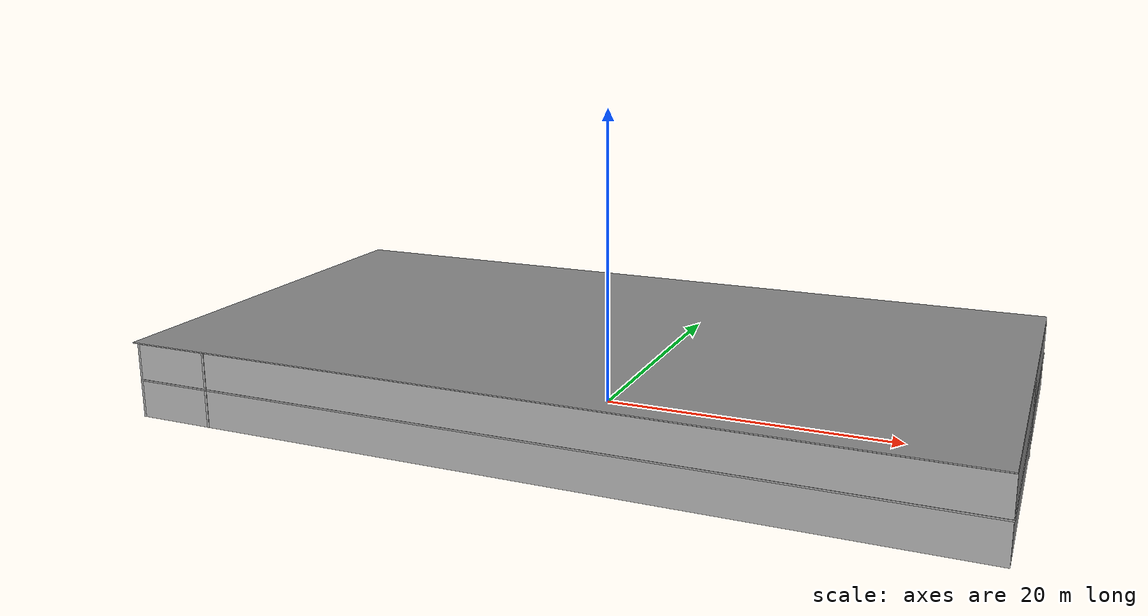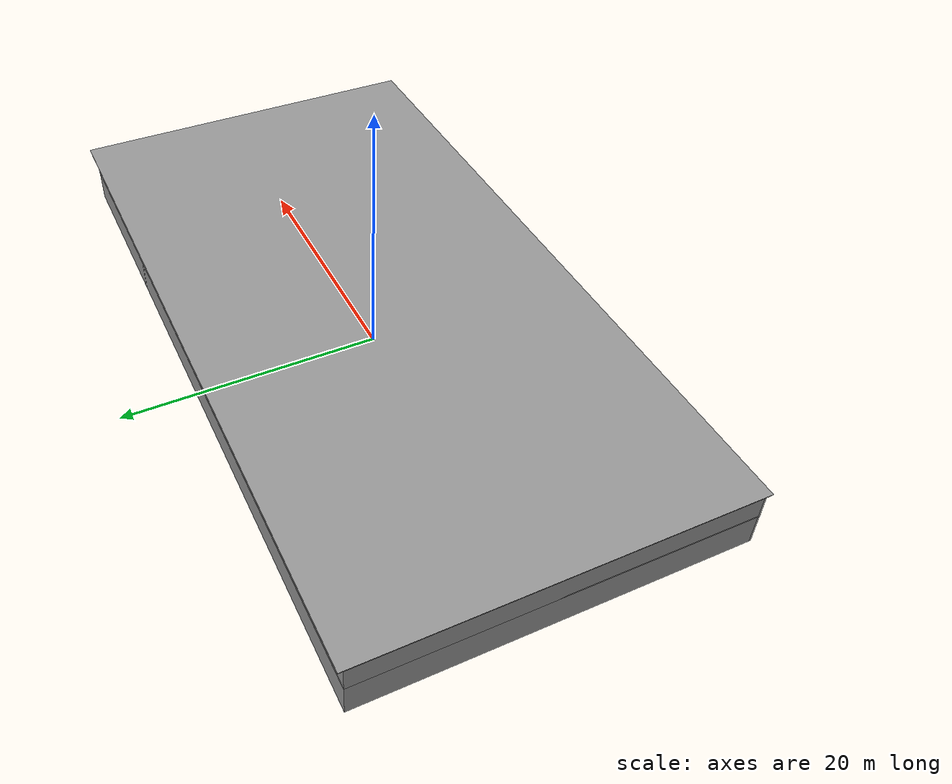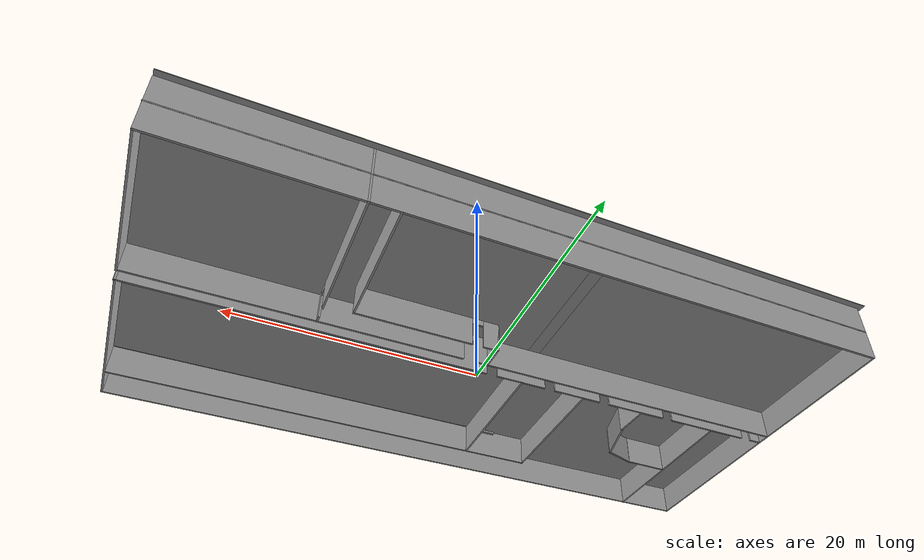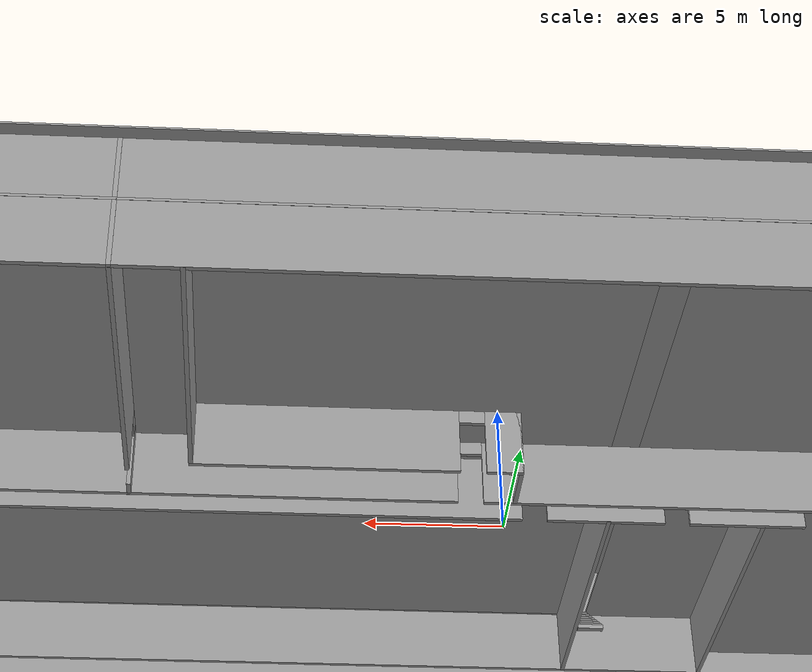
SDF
<?xml version='1.0'?>
<sdf version='1.6'>
  <model name='Biggest'>
    <link name='Floor_3'>
      <pose frame=''>0 0 2.5 0 -0 0</pose>
      <self_collide>0</self_collide>
      <enable_wind>0</enable_wind>
      <kinematic>0</kinematic>
      <visual name='Floor_3_Visual_1'>
        <pose frame=''>11.2183 -12.6292 0.05 0 -0 0</pose>
        <geometry>
          <box>
            <size>32.1063 3.27346 0.1</size>
          </box>
        </geometry>
        <material>
          <script>
            <uri>file://media/materials/scripts/gazebo.material</uri>
            <name>Gazebo/Grey</name>
          </script>
          <ambient>1 1 1 1</ambient>
        </material>
        <meta>
          <layer>1</layer>
        </meta>
        <transparency>0</transparency>
        <cast_shadows>1</cast_shadows>
      </visual>
      <visual name='Floor_3_Visual_3'>
        <pose frame=''>-4.33484 3.38673 0.05 0 -0 0</pose>
        <geometry>
          <box>
            <size>1 21.7585 0.1</size>
          </box>
        </geometry>
        <material>
          <script>
            <uri>file://media/materials/scripts/gazebo.material</uri>
            <name>Gazebo/Grey</name>
          </script>
          <ambient>1 1 1 1</ambient>
        </material>
        <meta>
          <layer>1</layer>
        </meta>
        <transparency>0</transparency>
        <cast_shadows>1</cast_shadows>
      </visual>
      <visual name='Floor_3_Visual_0'>
        <pose frame=''>-16.0531 0 0.05 0 -0 0</pose>
        <geometry>
          <box>
            <size>22.4366 28.5319 0.1</size>
          </box>
        </geometry>
        <material>
          <script>
            <uri>file://media/materials/scripts/gazebo.material</uri>
            <name>Gazebo/Grey</name>
          </script>
          <ambient>1 1 1 1</ambient>
        </material>
        <meta>
          <layer>1</layer>
        </meta>
        <transparency>0</transparency>
        <cast_shadows>1</cast_shadows>
      </visual>
      <visual name='Floor_3_Visual_2'>
        <pose frame=''>11.7183 1.63673 0.05 0 -0 0</pose>
        <geometry>
          <box>
            <size>31.1063 25.2585 0.1</size>
          </box>
        </geometry>
        <material>
          <script>
            <uri>file://media/materials/scripts/gazebo.material</uri>
            <name>Gazebo/Grey</name>
          </script>
          <ambient>1 1 1 1</ambient>
        </material>
        <meta>
          <layer>1</layer>
        </meta>
        <transparency>0</transparency>
        <cast_shadows>1</cast_shadows>
      </visual>
      <collision name='Floor_3_Collision_2'>
        <laser_retro>0</laser_retro>
        <max_contacts>10</max_contacts>
        <pose frame=''>11.7183 1.63673 0.05 0 -0 0</pose>
        <geometry>
          <box>
            <size>31.1063 25.2585 0.1</size>
          </box>
        </geometry>
        <surface>
          <friction>
            <ode>
              <mu>1</mu>
              <mu2>1</mu2>
              <fdir1>0 0 0</fdir1>
              <slip1>0</slip1>
              <slip2>0</slip2>
            </ode>
            <torsional>
              <coefficient>1</coefficient>
              <patch_radius>0</patch_radius>
              <surface_radius>0</surface_radius>
              <use_patch_radius>1</use_patch_radius>
              <ode>
                <slip>0</slip>
              </ode>
            </torsional>
          </friction>
          <bounce>
            <restitution_coefficient>0</restitution_coefficient>
            <threshold>1e+06</threshold>
          </bounce>
          <contact>
            <collide_without_contact>0</collide_without_contact>
            <collide_without_contact_bitmask>1</collide_without_contact_bitmask>
            <collide_bitmask>1</collide_bitmask>
            <ode>
              <soft_cfm>0</soft_cfm>
              <soft_erp>0.2</soft_erp>
              <kp>1e+13</kp>
              <kd>1</kd>
              <max_vel>0.01</max_vel>
              <min_depth>0</min_depth>
            </ode>
            <bullet>
              <split_impulse>1</split_impulse>
              <split_impulse_penetration_threshold>-0.01</split_impulse_penetration_threshold>
              <soft_cfm>0</soft_cfm>
              <soft_erp>0.2</soft_erp>
              <kp>1e+13</kp>
              <kd>1</kd>
            </bullet>
          </contact>
        </surface>
      </collision>
      <collision name='Floor_3_Collision_1'>
        <laser_retro>0</laser_retro>
        <max_contacts>10</max_contacts>
        <pose frame=''>11.2183 -12.6292 0.05 0 -0 0</pose>
        <geometry>
          <box>
            <size>32.1063 3.27346 0.1</size>
          </box>
        </geometry>
        <surface>
          <friction>
            <ode>
              <mu>1</mu>
              <mu2>1</mu2>
              <fdir1>0 0 0</fdir1>
              <slip1>0</slip1>
              <slip2>0</slip2>
            </ode>
            <torsional>
              <coefficient>1</coefficient>
              <patch_radius>0</patch_radius>
              <surface_radius>0</surface_radius>
              <use_patch_radius>1</use_patch_radius>
              <ode>
                <slip>0</slip>
              </ode>
            </torsional>
          </friction>
          <bounce>
            <restitution_coefficient>0</restitution_coefficient>
            <threshold>1e+06</threshold>
          </bounce>
          <contact>
            <collide_without_contact>0</collide_without_contact>
            <collide_without_contact_bitmask>1</collide_without_contact_bitmask>
            <collide_bitmask>1</collide_bitmask>
            <ode>
              <soft_cfm>0</soft_cfm>
              <soft_erp>0.2</soft_erp>
              <kp>1e+13</kp>
              <kd>1</kd>
              <max_vel>0.01</max_vel>
              <min_depth>0</min_depth>
            </ode>
            <bullet>
              <split_impulse>1</split_impulse>
              <split_impulse_penetration_threshold>-0.01</split_impulse_penetration_threshold>
              <soft_cfm>0</soft_cfm>
              <soft_erp>0.2</soft_erp>
              <kp>1e+13</kp>
              <kd>1</kd>
            </bullet>
          </contact>
        </surface>
      </collision>
      <collision name='Floor_3_Collision_3'>
        <laser_retro>0</laser_retro>
        <max_contacts>10</max_contacts>
        <pose frame=''>-4.33484 3.38673 0.05 0 -0 0</pose>
        <geometry>
          <box>
            <size>1 21.7585 0.1</size>
          </box>
        </geometry>
        <surface>
          <friction>
            <ode>
              <mu>1</mu>
              <mu2>1</mu2>
              <fdir1>0 0 0</fdir1>
              <slip1>0</slip1>
              <slip2>0</slip2>
            </ode>
            <torsional>
              <coefficient>1</coefficient>
              <patch_radius>0</patch_radius>
              <surface_radius>0</surface_radius>
              <use_patch_radius>1</use_patch_radius>
              <ode>
                <slip>0</slip>
              </ode>
            </torsional>
          </friction>
          <bounce>
            <restitution_coefficient>0</restitution_coefficient>
            <threshold>1e+06</threshold>
          </bounce>
          <contact>
            <collide_without_contact>0</collide_without_contact>
            <collide_without_contact_bitmask>1</collide_without_contact_bitmask>
            <collide_bitmask>1</collide_bitmask>
            <ode>
              <soft_cfm>0</soft_cfm>
              <soft_erp>0.2</soft_erp>
              <kp>1e+13</kp>
              <kd>1</kd>
              <max_vel>0.01</max_vel>
              <min_depth>0</min_depth>
            </ode>
            <bullet>
              <split_impulse>1</split_impulse>
              <split_impulse_penetration_threshold>-0.01</split_impulse_penetration_threshold>
              <soft_cfm>0</soft_cfm>
              <soft_erp>0.2</soft_erp>
              <kp>1e+13</kp>
              <kd>1</kd>
            </bullet>
          </contact>
        </surface>
      </collision>
      <collision name='Floor_3_Collision_0'>
        <laser_retro>0</laser_retro>
        <max_contacts>10</max_contacts>
        <pose frame=''>-16.0531 0 0.05 0 -0 0</pose>
        <geometry>
          <box>
            <size>22.4366 28.5319 0.1</size>
          </box>
        </geometry>
        <surface>
          <friction>
            <ode>
              <mu>1</mu>
              <mu2>1</mu2>
              <fdir1>0 0 0</fdir1>
              <slip1>0</slip1>
              <slip2>0</slip2>
            </ode>
            <torsional>
              <coefficient>1</coefficient>
              <patch_radius>0</patch_radius>
              <surface_radius>0</surface_radius>
              <use_patch_radius>1</use_patch_radius>
              <ode>
                <slip>0</slip>
              </ode>
            </torsional>
          </friction>
          <bounce>
            <restitution_coefficient>0</restitution_coefficient>
            <threshold>1e+06</threshold>
          </bounce>
          <contact>
            <collide_without_contact>0</collide_without_contact>
            <collide_without_contact_bitmask>1</collide_without_contact_bitmask>
            <collide_bitmask>1</collide_bitmask>
            <ode>
              <soft_cfm>0</soft_cfm>
              <soft_erp>0.2</soft_erp>
              <kp>1e+13</kp>
              <kd>1</kd>
              <max_vel>0.01</max_vel>
              <min_depth>0</min_depth>
            </ode>
            <bullet>
              <split_impulse>1</split_impulse>
              <split_impulse_penetration_threshold>-0.01</split_impulse_penetration_threshold>
              <soft_cfm>0</soft_cfm>
              <soft_erp>0.2</soft_erp>
              <kp>1e+13</kp>
              <kd>1</kd>
            </bullet>
          </contact>
        </surface>
      </collision>
    </link>
    <link name='Stairs_1'>
      <self_collide>0</self_collide>
      <enable_wind>0</enable_wind>
      <kinematic>0</kinematic>
      <pose frame=''>0 0 0 0 -0 0</pose>
      <visual name='Stairs_1_Visual_6'>
        <pose frame=''>-4.33484 -9.00918 1.08333 0 -0 0</pose>
        <geometry>
          <box>
            <size>1 0.233333 0.166667</size>
          </box>
        </geometry>
        <material>
          <script>
            <uri>file://media/materials/scripts/gazebo.material</uri>
            <name>Gazebo/Grey</name>
          </script>
          <ambient>1 1 1 1</ambient>
        </material>
        <meta>
          <layer>0</layer>
        </meta>
        <transparency>0</transparency>
        <cast_shadows>1</cast_shadows>
      </visual>
      <visual name='Stairs_1_Visual_2'>
        <pose frame=''>-4.33484 -8.07584 0.416667 0 -0 0</pose>
        <geometry>
          <box>
            <size>1 0.233333 0.166667</size>
          </box>
        </geometry>
        <material>
          <script>
            <uri>file://media/materials/scripts/gazebo.material</uri>
            <name>Gazebo/Grey</name>
          </script>
          <ambient>1 1 1 1</ambient>
        </material>
        <meta>
          <layer>0</layer>
        </meta>
        <transparency>0</transparency>
        <cast_shadows>1</cast_shadows>
      </visual>
      <visual name='Stairs_1_Visual_4'>
        <pose frame=''>-4.33484 -8.54251 0.75 0 -0 0</pose>
        <geometry>
          <box>
            <size>1 0.233333 0.166667</size>
          </box>
        </geometry>
        <material>
          <script>
            <uri>file://media/materials/scripts/gazebo.material</uri>
            <name>Gazebo/Grey</name>
          </script>
          <ambient>1 1 1 1</ambient>
        </material>
        <meta>
          <layer>0</layer>
        </meta>
        <transparency>0</transparency>
        <cast_shadows>1</cast_shadows>
      </visual>
      <visual name='Stairs_1_Visual_1'>
        <pose frame=''>-4.33484 -7.84251 0.25 0 -0 0</pose>
        <geometry>
          <box>
            <size>1 0.233333 0.166667</size>
          </box>
        </geometry>
        <material>
          <script>
            <uri>file://media/materials/scripts/gazebo.material</uri>
            <name>Gazebo/Grey</name>
          </script>
          <ambient>1 1 1 1</ambient>
        </material>
        <meta>
          <layer>0</layer>
        </meta>
        <transparency>0</transparency>
        <cast_shadows>1</cast_shadows>
      </visual>
      <visual name='Stairs_1_Visual_13'>
        <pose frame=''>-4.33484 -10.6425 2.25 0 -0 0</pose>
        <geometry>
          <box>
            <size>1 0.233333 0.166667</size>
          </box>
        </geometry>
        <material>
          <script>
            <uri>file://media/materials/scripts/gazebo.material</uri>
            <name>Gazebo/Grey</name>
          </script>
          <ambient>1 1 1 1</ambient>
        </material>
        <meta>
          <layer>0</layer>
        </meta>
        <transparency>0</transparency>
        <cast_shadows>1</cast_shadows>
      </visual>
      <visual name='Stairs_1_Visual_0'>
        <pose frame=''>-4.33484 -7.60918 0.083333 0 -0 0</pose>
        <geometry>
          <box>
            <size>1 0.233333 0.166667</size>
          </box>
        </geometry>
        <material>
          <script>
            <uri>file://media/materials/scripts/gazebo.material</uri>
            <name>Gazebo/Grey</name>
          </script>
          <ambient>1 1 1 1</ambient>
        </material>
        <meta>
          <layer>0</layer>
        </meta>
        <transparency>0</transparency>
        <cast_shadows>1</cast_shadows>
      </visual>
      <visual name='Stairs_1_Visual_9'>
        <pose frame=''>-4.33484 -9.70918 1.58333 0 -0 0</pose>
        <geometry>
          <box>
            <size>1 0.233333 0.166667</size>
          </box>
        </geometry>
        <material>
          <script>
            <uri>file://media/materials/scripts/gazebo.material</uri>
            <name>Gazebo/Grey</name>
          </script>
          <ambient>1 1 1 1</ambient>
        </material>
        <meta>
          <layer>0</layer>
        </meta>
        <transparency>0</transparency>
        <cast_shadows>1</cast_shadows>
      </visual>
      <visual name='Stairs_1_Visual_14'>
        <pose frame=''>-4.33484 -10.8758 2.41667 0 -0 0</pose>
        <geometry>
          <box>
            <size>1 0.233333 0.166667</size>
          </box>
        </geometry>
        <material>
          <script>
            <uri>file://media/materials/scripts/gazebo.material</uri>
            <name>Gazebo/Grey</name>
          </script>
          <ambient>1 1 1 1</ambient>
        </material>
        <meta>
          <layer>0</layer>
        </meta>
        <transparency>0</transparency>
        <cast_shadows>1</cast_shadows>
      </visual>
      <visual name='Stairs_1_Visual_3'>
        <pose frame=''>-4.33484 -8.30917 0.583333 0 -0 0</pose>
        <geometry>
          <box>
            <size>1 0.233333 0.166667</size>
          </box>
        </geometry>
        <material>
          <script>
            <uri>file://media/materials/scripts/gazebo.material</uri>
            <name>Gazebo/Grey</name>
          </script>
          <ambient>1 1 1 1</ambient>
        </material>
        <meta>
          <layer>0</layer>
        </meta>
        <transparency>0</transparency>
        <cast_shadows>1</cast_shadows>
      </visual>
      <visual name='Stairs_1_Visual_5'>
        <pose frame=''>-4.33484 -8.77584 0.916667 0 -0 0</pose>
        <geometry>
          <box>
            <size>1 0.233333 0.166667</size>
          </box>
        </geometry>
        <material>
          <script>
            <uri>file://media/materials/scripts/gazebo.material</uri>
            <name>Gazebo/Grey</name>
          </script>
          <ambient>1 1 1 1</ambient>
        </material>
        <meta>
          <layer>0</layer>
        </meta>
        <transparency>0</transparency>
        <cast_shadows>1</cast_shadows>
      </visual>
      <visual name='Stairs_1_Visual_10'>
        <pose frame=''>-4.33484 -9.94251 1.75 0 -0 0</pose>
        <geometry>
          <box>
            <size>1 0.233333 0.166667</size>
          </box>
        </geometry>
        <material>
          <script>
            <uri>file://media/materials/scripts/gazebo.material</uri>
            <name>Gazebo/Grey</name>
          </script>
          <ambient>1 1 1 1</ambient>
        </material>
        <meta>
          <layer>0</layer>
        </meta>
        <transparency>0</transparency>
        <cast_shadows>1</cast_shadows>
      </visual>
      <visual name='Stairs_1_Visual_8'>
        <pose frame=''>-4.33484 -9.47584 1.41667 0 -0 0</pose>
        <geometry>
          <box>
            <size>1 0.233333 0.166667</size>
          </box>
        </geometry>
        <material>
          <script>
            <uri>file://media/materials/scripts/gazebo.material</uri>
            <name>Gazebo/Grey</name>
          </script>
          <ambient>1 1 1 1</ambient>
        </material>
        <meta>
          <layer>0</layer>
        </meta>
        <transparency>0</transparency>
        <cast_shadows>1</cast_shadows>
      </visual>
      <visual name='Stairs_1_Visual_11'>
        <pose frame=''>-4.33484 -10.1758 1.91667 0 -0 0</pose>
        <geometry>
          <box>
            <size>1 0.233333 0.166667</size>
          </box>
        </geometry>
        <material>
          <script>
            <uri>file://media/materials/scripts/gazebo.material</uri>
            <name>Gazebo/Grey</name>
          </script>
          <ambient>1 1 1 1</ambient>
        </material>
        <meta>
          <layer>0</layer>
        </meta>
        <transparency>0</transparency>
        <cast_shadows>1</cast_shadows>
      </visual>
      <visual name='Stairs_1_Visual_7'>
        <pose frame=''>-4.33484 -9.24251 1.25 0 -0 0</pose>
        <geometry>
          <box>
            <size>1 0.233333 0.166667</size>
          </box>
        </geometry>
        <material>
          <script>
            <uri>file://media/materials/scripts/gazebo.material</uri>
            <name>Gazebo/Grey</name>
          </script>
          <ambient>1 1 1 1</ambient>
        </material>
        <meta>
          <layer>0</layer>
        </meta>
        <transparency>0</transparency>
        <cast_shadows>1</cast_shadows>
      </visual>
      <visual name='Stairs_1_Visual_12'>
        <pose frame=''>-4.33484 -10.4092 2.08333 0 -0 0</pose>
        <geometry>
          <box>
            <size>1 0.233333 0.166667</size>
          </box>
        </geometry>
        <material>
          <script>
            <uri>file://media/materials/scripts/gazebo.material</uri>
            <name>Gazebo/Grey</name>
          </script>
          <ambient>1 1 1 1</ambient>
        </material>
        <meta>
          <layer>0</layer>
        </meta>
        <transparency>0</transparency>
        <cast_shadows>1</cast_shadows>
      </visual>
      <collision name='Stairs_1_Collision_6'>
        <laser_retro>0</laser_retro>
        <max_contacts>10</max_contacts>
        <pose frame=''>-4.33484 -9.00918 1.08333 0 -0 0</pose>
        <geometry>
          <box>
            <size>1 0.233333 0.166667</size>
          </box>
        </geometry>
        <surface>
          <friction>
            <ode>
              <mu>1</mu>
              <mu2>1</mu2>
              <fdir1>0 0 0</fdir1>
              <slip1>0</slip1>
              <slip2>0</slip2>
            </ode>
            <torsional>
              <coefficient>1</coefficient>
              <patch_radius>0</patch_radius>
              <surface_radius>0</surface_radius>
              <use_patch_radius>1</use_patch_radius>
              <ode>
                <slip>0</slip>
              </ode>
            </torsional>
          </friction>
          <bounce>
            <restitution_coefficient>0</restitution_coefficient>
            <threshold>1e+06</threshold>
          </bounce>
          <contact>
            <collide_without_contact>0</collide_without_contact>
            <collide_without_contact_bitmask>1</collide_without_contact_bitmask>
            <collide_bitmask>1</collide_bitmask>
            <ode>
              <soft_cfm>0</soft_cfm>
              <soft_erp>0.2</soft_erp>
              <kp>1e+13</kp>
              <kd>1</kd>
              <max_vel>0.01</max_vel>
              <min_depth>0</min_depth>
            </ode>
            <bullet>
              <split_impulse>1</split_impulse>
              <split_impulse_penetration_threshold>-0.01</split_impulse_penetration_threshold>
              <soft_cfm>0</soft_cfm>
              <soft_erp>0.2</soft_erp>
              <kp>1e+13</kp>
              <kd>1</kd>
            </bullet>
          </contact>
        </surface>
      </collision>
      <collision name='Stairs_1_Collision_5'>
        <laser_retro>0</laser_retro>
        <max_contacts>10</max_contacts>
        <pose frame=''>-4.33484 -8.77584 0.916667 0 -0 0</pose>
        <geometry>
          <box>
            <size>1 0.233333 0.166667</size>
          </box>
        </geometry>
        <surface>
          <friction>
            <ode>
              <mu>1</mu>
              <mu2>1</mu2>
              <fdir1>0 0 0</fdir1>
              <slip1>0</slip1>
              <slip2>0</slip2>
            </ode>
            <torsional>
              <coefficient>1</coefficient>
              <patch_radius>0</patch_radius>
              <surface_radius>0</surface_radius>
              <use_patch_radius>1</use_patch_radius>
              <ode>
                <slip>0</slip>
              </ode>
            </torsional>
          </friction>
          <bounce>
            <restitution_coefficient>0</restitution_coefficient>
            <threshold>1e+06</threshold>
          </bounce>
          <contact>
            <collide_without_contact>0</collide_without_contact>
            <collide_without_contact_bitmask>1</collide_without_contact_bitmask>
            <collide_bitmask>1</collide_bitmask>
            <ode>
              <soft_cfm>0</soft_cfm>
              <soft_erp>0.2</soft_erp>
              <kp>1e+13</kp>
              <kd>1</kd>
              <max_vel>0.01</max_vel>
              <min_depth>0</min_depth>
            </ode>
            <bullet>
              <split_impulse>1</split_impulse>
              <split_impulse_penetration_threshold>-0.01</split_impulse_penetration_threshold>
              <soft_cfm>0</soft_cfm>
              <soft_erp>0.2</soft_erp>
              <kp>1e+13</kp>
              <kd>1</kd>
            </bullet>
          </contact>
        </surface>
      </collision>
      <collision name='Stairs_1_Collision_1'>
        <laser_retro>0</laser_retro>
        <max_contacts>10</max_contacts>
        <pose frame=''>-4.33484 -7.84251 0.25 0 -0 0</pose>
        <geometry>
          <box>
            <size>1 0.233333 0.166667</size>
          </box>
        </geometry>
        <surface>
          <friction>
            <ode>
              <mu>1</mu>
              <mu2>1</mu2>
              <fdir1>0 0 0</fdir1>
              <slip1>0</slip1>
              <slip2>0</slip2>
            </ode>
            <torsional>
              <coefficient>1</coefficient>
              <patch_radius>0</patch_radius>
              <surface_radius>0</surface_radius>
              <use_patch_radius>1</use_patch_radius>
              <ode>
                <slip>0</slip>
              </ode>
            </torsional>
          </friction>
          <bounce>
            <restitution_coefficient>0</restitution_coefficient>
            <threshold>1e+06</threshold>
          </bounce>
          <contact>
            <collide_without_contact>0</collide_without_contact>
            <collide_without_contact_bitmask>1</collide_without_contact_bitmask>
            <collide_bitmask>1</collide_bitmask>
            <ode>
              <soft_cfm>0</soft_cfm>
              <soft_erp>0.2</soft_erp>
              <kp>1e+13</kp>
              <kd>1</kd>
              <max_vel>0.01</max_vel>
              <min_depth>0</min_depth>
            </ode>
            <bullet>
              <split_impulse>1</split_impulse>
              <split_impulse_penetration_threshold>-0.01</split_impulse_penetration_threshold>
              <soft_cfm>0</soft_cfm>
              <soft_erp>0.2</soft_erp>
              <kp>1e+13</kp>
              <kd>1</kd>
            </bullet>
          </contact>
        </surface>
      </collision>
      <collision name='Stairs_1_Collision_9'>
        <laser_retro>0</laser_retro>
        <max_contacts>10</max_contacts>
        <pose frame=''>-4.33484 -9.70918 1.58333 0 -0 0</pose>
        <geometry>
          <box>
            <size>1 0.233333 0.166667</size>
          </box>
        </geometry>
        <surface>
          <friction>
            <ode>
              <mu>1</mu>
              <mu2>1</mu2>
              <fdir1>0 0 0</fdir1>
              <slip1>0</slip1>
              <slip2>0</slip2>
            </ode>
            <torsional>
              <coefficient>1</coefficient>
              <patch_radius>0</patch_radius>
              <surface_radius>0</surface_radius>
              <use_patch_radius>1</use_patch_radius>
              <ode>
                <slip>0</slip>
              </ode>
            </torsional>
          </friction>
          <bounce>
            <restitution_coefficient>0</restitution_coefficient>
            <threshold>1e+06</threshold>
          </bounce>
          <contact>
            <collide_without_contact>0</collide_without_contact>
            <collide_without_contact_bitmask>1</collide_without_contact_bitmask>
            <collide_bitmask>1</collide_bitmask>
            <ode>
              <soft_cfm>0</soft_cfm>
              <soft_erp>0.2</soft_erp>
              <kp>1e+13</kp>
              <kd>1</kd>
              <max_vel>0.01</max_vel>
              <min_depth>0</min_depth>
            </ode>
            <bullet>
              <split_impulse>1</split_impulse>
              <split_impulse_penetration_threshold>-0.01</split_impulse_penetration_threshold>
              <soft_cfm>0</soft_cfm>
              <soft_erp>0.2</soft_erp>
              <kp>1e+13</kp>
              <kd>1</kd>
            </bullet>
          </contact>
        </surface>
      </collision>
      <collision name='Stairs_1_Collision_12'>
        <laser_retro>0</laser_retro>
        <max_contacts>10</max_contacts>
        <pose frame=''>-4.33484 -10.4092 2.08333 0 -0 0</pose>
        <geometry>
          <box>
            <size>1 0.233333 0.166667</size>
          </box>
        </geometry>
        <surface>
          <friction>
            <ode>
              <mu>1</mu>
              <mu2>1</mu2>
              <fdir1>0 0 0</fdir1>
              <slip1>0</slip1>
              <slip2>0</slip2>
            </ode>
            <torsional>
              <coefficient>1</coefficient>
              <patch_radius>0</patch_radius>
              <surface_radius>0</surface_radius>
              <use_patch_radius>1</use_patch_radius>
              <ode>
                <slip>0</slip>
              </ode>
            </torsional>
          </friction>
          <bounce>
            <restitution_coefficient>0</restitution_coefficient>
            <threshold>1e+06</threshold>
          </bounce>
          <contact>
            <collide_without_contact>0</collide_without_contact>
            <collide_without_contact_bitmask>1</collide_without_contact_bitmask>
            <collide_bitmask>1</collide_bitmask>
            <ode>
              <soft_cfm>0</soft_cfm>
              <soft_erp>0.2</soft_erp>
              <kp>1e+13</kp>
              <kd>1</kd>
              <max_vel>0.01</max_vel>
              <min_depth>0</min_depth>
            </ode>
            <bullet>
              <split_impulse>1</split_impulse>
              <split_impulse_penetration_threshold>-0.01</split_impulse_penetration_threshold>
              <soft_cfm>0</soft_cfm>
              <soft_erp>0.2</soft_erp>
              <kp>1e+13</kp>
              <kd>1</kd>
            </bullet>
          </contact>
        </surface>
      </collision>
      <collision name='Stairs_1_Collision_2'>
        <laser_retro>0</laser_retro>
        <max_contacts>10</max_contacts>
        <pose frame=''>-4.33484 -8.07584 0.416667 0 -0 0</pose>
        <geometry>
          <box>
            <size>1 0.233333 0.166667</size>
          </box>
        </geometry>
        <surface>
          <friction>
            <ode>
              <mu>1</mu>
              <mu2>1</mu2>
              <fdir1>0 0 0</fdir1>
              <slip1>0</slip1>
              <slip2>0</slip2>
            </ode>
            <torsional>
              <coefficient>1</coefficient>
              <patch_radius>0</patch_radius>
              <surface_radius>0</surface_radius>
              <use_patch_radius>1</use_patch_radius>
              <ode>
                <slip>0</slip>
              </ode>
            </torsional>
          </friction>
          <bounce>
            <restitution_coefficient>0</restitution_coefficient>
            <threshold>1e+06</threshold>
          </bounce>
          <contact>
            <collide_without_contact>0</collide_without_contact>
            <collide_without_contact_bitmask>1</collide_without_contact_bitmask>
            <collide_bitmask>1</collide_bitmask>
            <ode>
              <soft_cfm>0</soft_cfm>
              <soft_erp>0.2</soft_erp>
              <kp>1e+13</kp>
              <kd>1</kd>
              <max_vel>0.01</max_vel>
              <min_depth>0</min_depth>
            </ode>
            <bullet>
              <split_impulse>1</split_impulse>
              <split_impulse_penetration_threshold>-0.01</split_impulse_penetration_threshold>
              <soft_cfm>0</soft_cfm>
              <soft_erp>0.2</soft_erp>
              <kp>1e+13</kp>
              <kd>1</kd>
            </bullet>
          </contact>
        </surface>
      </collision>
      <collision name='Stairs_1_Collision_10'>
        <laser_retro>0</laser_retro>
        <max_contacts>10</max_contacts>
        <pose frame=''>-4.33484 -9.94251 1.75 0 -0 0</pose>
        <geometry>
          <box>
            <size>1 0.233333 0.166667</size>
          </box>
        </geometry>
        <surface>
          <friction>
            <ode>
              <mu>1</mu>
              <mu2>1</mu2>
              <fdir1>0 0 0</fdir1>
              <slip1>0</slip1>
              <slip2>0</slip2>
            </ode>
            <torsional>
              <coefficient>1</coefficient>
              <patch_radius>0</patch_radius>
              <surface_radius>0</surface_radius>
              <use_patch_radius>1</use_patch_radius>
              <ode>
                <slip>0</slip>
              </ode>
            </torsional>
          </friction>
          <bounce>
            <restitution_coefficient>0</restitution_coefficient>
            <threshold>1e+06</threshold>
          </bounce>
          <contact>
            <collide_without_contact>0</collide_without_contact>
            <collide_without_contact_bitmask>1</collide_without_contact_bitmask>
            <collide_bitmask>1</collide_bitmask>
            <ode>
              <soft_cfm>0</soft_cfm>
              <soft_erp>0.2</soft_erp>
              <kp>1e+13</kp>
              <kd>1</kd>
              <max_vel>0.01</max_vel>
              <min_depth>0</min_depth>
            </ode>
            <bullet>
              <split_impulse>1</split_impulse>
              <split_impulse_penetration_threshold>-0.01</split_impulse_penetration_threshold>
              <soft_cfm>0</soft_cfm>
              <soft_erp>0.2</soft_erp>
              <kp>1e+13</kp>
              <kd>1</kd>
            </bullet>
          </contact>
        </surface>
      </collision>
      <collision name='Stairs_1_Collision_3'>
        <laser_retro>0</laser_retro>
        <max_contacts>10</max_contacts>
        <pose frame=''>-4.33484 -8.30917 0.583333 0 -0 0</pose>
        <geometry>
          <box>
            <size>1 0.233333 0.166667</size>
          </box>
        </geometry>
        <surface>
          <friction>
            <ode>
              <mu>1</mu>
              <mu2>1</mu2>
              <fdir1>0 0 0</fdir1>
              <slip1>0</slip1>
              <slip2>0</slip2>
            </ode>
            <torsional>
              <coefficient>1</coefficient>
              <patch_radius>0</patch_radius>
              <surface_radius>0</surface_radius>
              <use_patch_radius>1</use_patch_radius>
              <ode>
                <slip>0</slip>
              </ode>
            </torsional>
          </friction>
          <bounce>
            <restitution_coefficient>0</restitution_coefficient>
            <threshold>1e+06</threshold>
          </bounce>
          <contact>
            <collide_without_contact>0</collide_without_contact>
            <collide_without_contact_bitmask>1</collide_without_contact_bitmask>
            <collide_bitmask>1</collide_bitmask>
            <ode>
              <soft_cfm>0</soft_cfm>
              <soft_erp>0.2</soft_erp>
              <kp>1e+13</kp>
              <kd>1</kd>
              <max_vel>0.01</max_vel>
              <min_depth>0</min_depth>
            </ode>
            <bullet>
              <split_impulse>1</split_impulse>
              <split_impulse_penetration_threshold>-0.01</split_impulse_penetration_threshold>
              <soft_cfm>0</soft_cfm>
              <soft_erp>0.2</soft_erp>
              <kp>1e+13</kp>
              <kd>1</kd>
            </bullet>
          </contact>
        </surface>
      </collision>
      <collision name='Stairs_1_Collision_7'>
        <laser_retro>0</laser_retro>
        <max_contacts>10</max_contacts>
        <pose frame=''>-4.33484 -9.24251 1.25 0 -0 0</pose>
        <geometry>
          <box>
            <size>1 0.233333 0.166667</size>
          </box>
        </geometry>
        <surface>
          <friction>
            <ode>
              <mu>1</mu>
              <mu2>1</mu2>
              <fdir1>0 0 0</fdir1>
              <slip1>0</slip1>
              <slip2>0</slip2>
            </ode>
            <torsional>
              <coefficient>1</coefficient>
              <patch_radius>0</patch_radius>
              <surface_radius>0</surface_radius>
              <use_patch_radius>1</use_patch_radius>
              <ode>
                <slip>0</slip>
              </ode>
            </torsional>
          </friction>
          <bounce>
            <restitution_coefficient>0</restitution_coefficient>
            <threshold>1e+06</threshold>
          </bounce>
          <contact>
            <collide_without_contact>0</collide_without_contact>
            <collide_without_contact_bitmask>1</collide_without_contact_bitmask>
            <collide_bitmask>1</collide_bitmask>
            <ode>
              <soft_cfm>0</soft_cfm>
              <soft_erp>0.2</soft_erp>
              <kp>1e+13</kp>
              <kd>1</kd>
              <max_vel>0.01</max_vel>
              <min_depth>0</min_depth>
            </ode>
            <bullet>
              <split_impulse>1</split_impulse>
              <split_impulse_penetration_threshold>-0.01</split_impulse_penetration_threshold>
              <soft_cfm>0</soft_cfm>
              <soft_erp>0.2</soft_erp>
              <kp>1e+13</kp>
              <kd>1</kd>
            </bullet>
          </contact>
        </surface>
      </collision>
      <collision name='Stairs_1_Collision_0'>
        <laser_retro>0</laser_retro>
        <max_contacts>10</max_contacts>
        <pose frame=''>-4.33484 -7.60918 0.083333 0 -0 0</pose>
        <geometry>
          <box>
            <size>1 0.233333 0.166667</size>
          </box>
        </geometry>
        <surface>
          <friction>
            <ode>
              <mu>1</mu>
              <mu2>1</mu2>
              <fdir1>0 0 0</fdir1>
              <slip1>0</slip1>
              <slip2>0</slip2>
            </ode>
            <torsional>
              <coefficient>1</coefficient>
              <patch_radius>0</patch_radius>
              <surface_radius>0</surface_radius>
              <use_patch_radius>1</use_patch_radius>
              <ode>
                <slip>0</slip>
              </ode>
            </torsional>
          </friction>
          <bounce>
            <restitution_coefficient>0</restitution_coefficient>
            <threshold>1e+06</threshold>
          </bounce>
          <contact>
            <collide_without_contact>0</collide_without_contact>
            <collide_without_contact_bitmask>1</collide_without_contact_bitmask>
            <collide_bitmask>1</collide_bitmask>
            <ode>
              <soft_cfm>0</soft_cfm>
              <soft_erp>0.2</soft_erp>
              <kp>1e+13</kp>
              <kd>1</kd>
              <max_vel>0.01</max_vel>
              <min_depth>0</min_depth>
            </ode>
            <bullet>
              <split_impulse>1</split_impulse>
              <split_impulse_penetration_threshold>-0.01</split_impulse_penetration_threshold>
              <soft_cfm>0</soft_cfm>
              <soft_erp>0.2</soft_erp>
              <kp>1e+13</kp>
              <kd>1</kd>
            </bullet>
          </contact>
        </surface>
      </collision>
      <collision name='Stairs_1_Collision_14'>
        <laser_retro>0</laser_retro>
        <max_contacts>10</max_contacts>
        <pose frame=''>-4.33484 -10.8758 2.41667 0 -0 0</pose>
        <geometry>
          <box>
            <size>1 0.233333 0.166667</size>
          </box>
        </geometry>
        <surface>
          <friction>
            <ode>
              <mu>1</mu>
              <mu2>1</mu2>
              <fdir1>0 0 0</fdir1>
              <slip1>0</slip1>
              <slip2>0</slip2>
            </ode>
            <torsional>
              <coefficient>1</coefficient>
              <patch_radius>0</patch_radius>
              <surface_radius>0</surface_radius>
              <use_patch_radius>1</use_patch_radius>
              <ode>
                <slip>0</slip>
              </ode>
            </torsional>
          </friction>
          <bounce>
            <restitution_coefficient>0</restitution_coefficient>
            <threshold>1e+06</threshold>
          </bounce>
          <contact>
            <collide_without_contact>0</collide_without_contact>
            <collide_without_contact_bitmask>1</collide_without_contact_bitmask>
            <collide_bitmask>1</collide_bitmask>
            <ode>
              <soft_cfm>0</soft_cfm>
              <soft_erp>0.2</soft_erp>
              <kp>1e+13</kp>
              <kd>1</kd>
              <max_vel>0.01</max_vel>
              <min_depth>0</min_depth>
            </ode>
            <bullet>
              <split_impulse>1</split_impulse>
              <split_impulse_penetration_threshold>-0.01</split_impulse_penetration_threshold>
              <soft_cfm>0</soft_cfm>
              <soft_erp>0.2</soft_erp>
              <kp>1e+13</kp>
              <kd>1</kd>
            </bullet>
          </contact>
        </surface>
      </collision>
      <collision name='Stairs_1_Collision_8'>
        <laser_retro>0</laser_retro>
        <max_contacts>10</max_contacts>
        <pose frame=''>-4.33484 -9.47584 1.41667 0 -0 0</pose>
        <geometry>
          <box>
            <size>1 0.233333 0.166667</size>
          </box>
        </geometry>
        <surface>
          <friction>
            <ode>
              <mu>1</mu>
              <mu2>1</mu2>
              <fdir1>0 0 0</fdir1>
              <slip1>0</slip1>
              <slip2>0</slip2>
            </ode>
            <torsional>
              <coefficient>1</coefficient>
              <patch_radius>0</patch_radius>
              <surface_radius>0</surface_radius>
              <use_patch_radius>1</use_patch_radius>
              <ode>
                <slip>0</slip>
              </ode>
            </torsional>
          </friction>
          <bounce>
            <restitution_coefficient>0</restitution_coefficient>
            <threshold>1e+06</threshold>
          </bounce>
          <contact>
            <collide_without_contact>0</collide_without_contact>
            <collide_without_contact_bitmask>1</collide_without_contact_bitmask>
            <collide_bitmask>1</collide_bitmask>
            <ode>
              <soft_cfm>0</soft_cfm>
              <soft_erp>0.2</soft_erp>
              <kp>1e+13</kp>
              <kd>1</kd>
              <max_vel>0.01</max_vel>
              <min_depth>0</min_depth>
            </ode>
            <bullet>
              <split_impulse>1</split_impulse>
              <split_impulse_penetration_threshold>-0.01</split_impulse_penetration_threshold>
              <soft_cfm>0</soft_cfm>
              <soft_erp>0.2</soft_erp>
              <kp>1e+13</kp>
              <kd>1</kd>
            </bullet>
          </contact>
        </surface>
      </collision>
      <collision name='Stairs_1_Collision_13'>
        <laser_retro>0</laser_retro>
        <max_contacts>10</max_contacts>
        <pose frame=''>-4.33484 -10.6425 2.25 0 -0 0</pose>
        <geometry>
          <box>
            <size>1 0.233333 0.166667</size>
          </box>
        </geometry>
        <surface>
          <friction>
            <ode>
              <mu>1</mu>
              <mu2>1</mu2>
              <fdir1>0 0 0</fdir1>
              <slip1>0</slip1>
              <slip2>0</slip2>
            </ode>
            <torsional>
              <coefficient>1</coefficient>
              <patch_radius>0</patch_radius>
              <surface_radius>0</surface_radius>
              <use_patch_radius>1</use_patch_radius>
              <ode>
                <slip>0</slip>
              </ode>
            </torsional>
          </friction>
          <bounce>
            <restitution_coefficient>0</restitution_coefficient>
            <threshold>1e+06</threshold>
          </bounce>
          <contact>
            <collide_without_contact>0</collide_without_contact>
            <collide_without_contact_bitmask>1</collide_without_contact_bitmask>
            <collide_bitmask>1</collide_bitmask>
            <ode>
              <soft_cfm>0</soft_cfm>
              <soft_erp>0.2</soft_erp>
              <kp>1e+13</kp>
              <kd>1</kd>
              <max_vel>0.01</max_vel>
              <min_depth>0</min_depth>
            </ode>
            <bullet>
              <split_impulse>1</split_impulse>
              <split_impulse_penetration_threshold>-0.01</split_impulse_penetration_threshold>
              <soft_cfm>0</soft_cfm>
              <soft_erp>0.2</soft_erp>
              <kp>1e+13</kp>
              <kd>1</kd>
            </bullet>
          </contact>
        </surface>
      </collision>
      <collision name='Stairs_1_Collision_11'>
        <laser_retro>0</laser_retro>
        <max_contacts>10</max_contacts>
        <pose frame=''>-4.33484 -10.1758 1.91667 0 -0 0</pose>
        <geometry>
          <box>
            <size>1 0.233333 0.166667</size>
          </box>
        </geometry>
        <surface>
          <friction>
            <ode>
              <mu>1</mu>
              <mu2>1</mu2>
              <fdir1>0 0 0</fdir1>
              <slip1>0</slip1>
              <slip2>0</slip2>
            </ode>
            <torsional>
              <coefficient>1</coefficient>
              <patch_radius>0</patch_radius>
              <surface_radius>0</surface_radius>
              <use_patch_radius>1</use_patch_radius>
              <ode>
                <slip>0</slip>
              </ode>
            </torsional>
          </friction>
          <bounce>
            <restitution_coefficient>0</restitution_coefficient>
            <threshold>1e+06</threshold>
          </bounce>
          <contact>
            <collide_without_contact>0</collide_without_contact>
            <collide_without_contact_bitmask>1</collide_without_contact_bitmask>
            <collide_bitmask>1</collide_bitmask>
            <ode>
              <soft_cfm>0</soft_cfm>
              <soft_erp>0.2</soft_erp>
              <kp>1e+13</kp>
              <kd>1</kd>
              <max_vel>0.01</max_vel>
              <min_depth>0</min_depth>
            </ode>
            <bullet>
              <split_impulse>1</split_impulse>
              <split_impulse_penetration_threshold>-0.01</split_impulse_penetration_threshold>
              <soft_cfm>0</soft_cfm>
              <soft_erp>0.2</soft_erp>
              <kp>1e+13</kp>
              <kd>1</kd>
            </bullet>
          </contact>
        </surface>
      </collision>
      <collision name='Stairs_1_Collision_4'>
        <laser_retro>0</laser_retro>
        <max_contacts>10</max_contacts>
        <pose frame=''>-4.33484 -8.54251 0.75 0 -0 0</pose>
        <geometry>
          <box>
            <size>1 0.233333 0.166667</size>
          </box>
        </geometry>
        <surface>
          <friction>
            <ode>
              <mu>1</mu>
              <mu2>1</mu2>
              <fdir1>0 0 0</fdir1>
              <slip1>0</slip1>
              <slip2>0</slip2>
            </ode>
            <torsional>
              <coefficient>1</coefficient>
              <patch_radius>0</patch_radius>
              <surface_radius>0</surface_radius>
              <use_patch_radius>1</use_patch_radius>
              <ode>
                <slip>0</slip>
              </ode>
            </torsional>
          </friction>
          <bounce>
            <restitution_coefficient>0</restitution_coefficient>
            <threshold>1e+06</threshold>
          </bounce>
          <contact>
            <collide_without_contact>0</collide_without_contact>
            <collide_without_contact_bitmask>1</collide_without_contact_bitmask>
            <collide_bitmask>1</collide_bitmask>
            <ode>
              <soft_cfm>0</soft_cfm>
              <soft_erp>0.2</soft_erp>
              <kp>1e+13</kp>
              <kd>1</kd>
              <max_vel>0.01</max_vel>
              <min_depth>0</min_depth>
            </ode>
            <bullet>
              <split_impulse>1</split_impulse>
              <split_impulse_penetration_threshold>-0.01</split_impulse_penetration_threshold>
              <soft_cfm>0</soft_cfm>
              <soft_erp>0.2</soft_erp>
              <kp>1e+13</kp>
              <kd>1</kd>
            </bullet>
          </contact>
        </surface>
      </collision>
    </link>
    <link name='Wall_101'>
      <pose frame=''>-20.1199 -7.02638 0 0 0 -3.12807</pose>
      <self_collide>0</self_collide>
      <enable_wind>0</enable_wind>
      <kinematic>0</kinematic>
      <visual name='Wall_101_Visual'>
        <pose frame=''>0 0 1.25 0 -0 0</pose>
        <geometry>
          <box>
            <size>3.63056 0.15 2.5</size>
          </box>
        </geometry>
        <material>
          <script>
            <uri>file://media/materials/scripts/gazebo.material</uri>
            <name>Gazebo/Grey</name>
          </script>
          <ambient>1 1 1 1</ambient>
        </material>
        <meta>
          <layer>0</layer>
        </meta>
        <transparency>0</transparency>
        <cast_shadows>1</cast_shadows>
      </visual>
      <collision name='Wall_101_Collision'>
        <laser_retro>0</laser_retro>
        <max_contacts>10</max_contacts>
        <pose frame=''>0 0 1.25 0 -0 0</pose>
        <geometry>
          <box>
            <size>3.63056 0.15 2.5</size>
          </box>
        </geometry>
        <surface>
          <friction>
            <ode>
              <mu>1</mu>
              <mu2>1</mu2>
              <fdir1>0 0 0</fdir1>
              <slip1>0</slip1>
              <slip2>0</slip2>
            </ode>
            <torsional>
              <coefficient>1</coefficient>
              <patch_radius>0</patch_radius>
              <surface_radius>0</surface_radius>
              <use_patch_radius>1</use_patch_radius>
              <ode>
                <slip>0</slip>
              </ode>
            </torsional>
          </friction>
          <bounce>
            <restitution_coefficient>0</restitution_coefficient>
            <threshold>1e+06</threshold>
          </bounce>
          <contact>
            <collide_without_contact>0</collide_without_contact>
            <collide_without_contact_bitmask>1</collide_without_contact_bitmask>
            <collide_bitmask>1</collide_bitmask>
            <ode>
              <soft_cfm>0</soft_cfm>
              <soft_erp>0.2</soft_erp>
              <kp>1e+13</kp>
              <kd>1</kd>
              <max_vel>0.01</max_vel>
              <min_depth>0</min_depth>
            </ode>
            <bullet>
              <split_impulse>1</split_impulse>
              <split_impulse_penetration_threshold>-0.01</split_impulse_penetration_threshold>
              <soft_cfm>0</soft_cfm>
              <soft_erp>0.2</soft_erp>
              <kp>1e+13</kp>
              <kd>1</kd>
            </bullet>
          </contact>
        </surface>
      </collision>
    </link>
    <link name='Wall_103'>
      <pose frame=''>-9.33292 -5.35177 0 0 0 -1.5708</pose>
      <self_collide>0</self_collide>
      <enable_wind>0</enable_wind>
      <kinematic>0</kinematic>
      <visual name='Wall_103_Visual'>
        <pose frame=''>0 0 1.25 0 -0 0</pose>
        <geometry>
          <box>
            <size>11.75 0.15 2.5</size>
          </box>
        </geometry>
        <material>
          <script>
            <uri>file://media/materials/scripts/gazebo.material</uri>
            <name>Gazebo/Grey</name>
          </script>
          <ambient>1 1 1 1</ambient>
        </material>
        <meta>
          <layer>0</layer>
        </meta>
        <transparency>0</transparency>
        <cast_shadows>1</cast_shadows>
      </visual>
      <collision name='Wall_103_Collision'>
        <laser_retro>0</laser_retro>
        <max_contacts>10</max_contacts>
        <pose frame=''>0 0 1.25 0 -0 0</pose>
        <geometry>
          <box>
            <size>11.75 0.15 2.5</size>
          </box>
        </geometry>
        <surface>
          <friction>
            <ode>
              <mu>1</mu>
              <mu2>1</mu2>
              <fdir1>0 0 0</fdir1>
              <slip1>0</slip1>
              <slip2>0</slip2>
            </ode>
            <torsional>
              <coefficient>1</coefficient>
              <patch_radius>0</patch_radius>
              <surface_radius>0</surface_radius>
              <use_patch_radius>1</use_patch_radius>
              <ode>
                <slip>0</slip>
              </ode>
            </torsional>
          </friction>
          <bounce>
            <restitution_coefficient>0</restitution_coefficient>
            <threshold>1e+06</threshold>
          </bounce>
          <contact>
            <collide_without_contact>0</collide_without_contact>
            <collide_without_contact_bitmask>1</collide_without_contact_bitmask>
            <collide_bitmask>1</collide_bitmask>
            <ode>
              <soft_cfm>0</soft_cfm>
              <soft_erp>0.2</soft_erp>
              <kp>1e+13</kp>
              <kd>1</kd>
              <max_vel>0.01</max_vel>
              <min_depth>0</min_depth>
            </ode>
            <bullet>
              <split_impulse>1</split_impulse>
              <split_impulse_penetration_threshold>-0.01</split_impulse_penetration_threshold>
              <soft_cfm>0</soft_cfm>
              <soft_erp>0.2</soft_erp>
              <kp>1e+13</kp>
              <kd>1</kd>
            </bullet>
          </contact>
        </surface>
      </collision>
    </link>
    <link name='Wall_104'>
      <pose frame=''>8.84208 -11.1518 0 0 -0 0</pose>
      <self_collide>0</self_collide>
      <enable_wind>0</enable_wind>
      <kinematic>0</kinematic>
      <visual name='Wall_104_Visual'>
        <pose frame=''>0 0 1.25 0 -0 0</pose>
        <geometry>
          <box>
            <size>36.5 0.15 2.5</size>
          </box>
        </geometry>
        <material>
          <script>
            <uri>file://media/materials/scripts/gazebo.material</uri>
            <name>Gazebo/Grey</name>
          </script>
          <ambient>1 1 1 1</ambient>
        </material>
        <meta>
          <layer>0</layer>
        </meta>
        <transparency>0</transparency>
        <cast_shadows>1</cast_shadows>
      </visual>
      <collision name='Wall_104_Collision'>
        <laser_retro>0</laser_retro>
        <max_contacts>10</max_contacts>
        <pose frame=''>0 0 1.25 0 -0 0</pose>
        <geometry>
          <box>
            <size>36.5 0.15 2.5</size>
          </box>
        </geometry>
        <surface>
          <friction>
            <ode>
              <mu>1</mu>
              <mu2>1</mu2>
              <fdir1>0 0 0</fdir1>
              <slip1>0</slip1>
              <slip2>0</slip2>
            </ode>
            <torsional>
              <coefficient>1</coefficient>
              <patch_radius>0</patch_radius>
              <surface_radius>0</surface_radius>
              <use_patch_radius>1</use_patch_radius>
              <ode>
                <slip>0</slip>
              </ode>
            </torsional>
          </friction>
          <bounce>
            <restitution_coefficient>0</restitution_coefficient>
            <threshold>1e+06</threshold>
          </bounce>
          <contact>
            <collide_without_contact>0</collide_without_contact>
            <collide_without_contact_bitmask>1</collide_without_contact_bitmask>
            <collide_bitmask>1</collide_bitmask>
            <ode>
              <soft_cfm>0</soft_cfm>
              <soft_erp>0.2</soft_erp>
              <kp>1e+13</kp>
              <kd>1</kd>
              <max_vel>0.01</max_vel>
              <min_depth>0</min_depth>
            </ode>
            <bullet>
              <split_impulse>1</split_impulse>
              <split_impulse_penetration_threshold>-0.01</split_impulse_penetration_threshold>
              <soft_cfm>0</soft_cfm>
              <soft_erp>0.2</soft_erp>
              <kp>1e+13</kp>
              <kd>1</kd>
            </bullet>
          </contact>
        </surface>
      </collision>
    </link>
    <link name='Wall_106'>
      <pose frame=''>-3.73234 -5.28954 0 0 0 -1.5708</pose>
      <self_collide>0</self_collide>
      <enable_wind>0</enable_wind>
      <kinematic>0</kinematic>
      <visual name='Wall_106_Visual'>
        <pose frame=''>0 0 1.25 0 -0 0</pose>
        <geometry>
          <box>
            <size>11.75 0.15 2.5</size>
          </box>
        </geometry>
        <material>
          <script>
            <uri>file://media/materials/scripts/gazebo.material</uri>
            <name>Gazebo/Grey</name>
          </script>
          <ambient>1 1 1 1</ambient>
        </material>
        <meta>
          <layer>0</layer>
        </meta>
        <transparency>0</transparency>
        <cast_shadows>1</cast_shadows>
      </visual>
      <collision name='Wall_106_Collision'>
        <laser_retro>0</laser_retro>
        <max_contacts>10</max_contacts>
        <pose frame=''>0 0 1.25 0 -0 0</pose>
        <geometry>
          <box>
            <size>11.75 0.15 2.5</size>
          </box>
        </geometry>
        <surface>
          <friction>
            <ode>
              <mu>1</mu>
              <mu2>1</mu2>
              <fdir1>0 0 0</fdir1>
              <slip1>0</slip1>
              <slip2>0</slip2>
            </ode>
            <torsional>
              <coefficient>1</coefficient>
              <patch_radius>0</patch_radius>
              <surface_radius>0</surface_radius>
              <use_patch_radius>1</use_patch_radius>
              <ode>
                <slip>0</slip>
              </ode>
            </torsional>
          </friction>
          <bounce>
            <restitution_coefficient>0</restitution_coefficient>
            <threshold>1e+06</threshold>
          </bounce>
          <contact>
            <collide_without_contact>0</collide_without_contact>
            <collide_without_contact_bitmask>1</collide_without_contact_bitmask>
            <collide_bitmask>1</collide_bitmask>
            <ode>
              <soft_cfm>0</soft_cfm>
              <soft_erp>0.2</soft_erp>
              <kp>1e+13</kp>
              <kd>1</kd>
              <max_vel>0.01</max_vel>
              <min_depth>0</min_depth>
            </ode>
            <bullet>
              <split_impulse>1</split_impulse>
              <split_impulse_penetration_threshold>-0.01</split_impulse_penetration_threshold>
              <soft_cfm>0</soft_cfm>
              <soft_erp>0.2</soft_erp>
              <kp>1e+13</kp>
              <kd>1</kd>
            </bullet>
          </contact>
        </surface>
      </collision>
    </link>
    <link name='Wall_108'>
      <pose frame=''>-0.22022 2.64491 0 0 -0 1.5708</pose>
      <self_collide>0</self_collide>
      <enable_wind>0</enable_wind>
      <kinematic>0</kinematic>
      <visual name='Wall_108_Visual'>
        <pose frame=''>0 0 1.25 0 -0 0</pose>
        <geometry>
          <box>
            <size>2 0.15 2.5</size>
          </box>
        </geometry>
        <material>
          <script>
            <uri>file://media/materials/scripts/gazebo.material</uri>
            <name>Gazebo/Grey</name>
          </script>
          <ambient>1 1 1 1</ambient>
        </material>
        <meta>
          <layer>0</layer>
        </meta>
        <transparency>0</transparency>
        <cast_shadows>1</cast_shadows>
      </visual>
      <collision name='Wall_108_Collision'>
        <laser_retro>0</laser_retro>
        <max_contacts>10</max_contacts>
        <pose frame=''>0 0 1.25 0 -0 0</pose>
        <geometry>
          <box>
            <size>2 0.15 2.5</size>
          </box>
        </geometry>
        <surface>
          <friction>
            <ode>
              <mu>1</mu>
              <mu2>1</mu2>
              <fdir1>0 0 0</fdir1>
              <slip1>0</slip1>
              <slip2>0</slip2>
            </ode>
            <torsional>
              <coefficient>1</coefficient>
              <patch_radius>0</patch_radius>
              <surface_radius>0</surface_radius>
              <use_patch_radius>1</use_patch_radius>
              <ode>
                <slip>0</slip>
              </ode>
            </torsional>
          </friction>
          <bounce>
            <restitution_coefficient>0</restitution_coefficient>
            <threshold>1e+06</threshold>
          </bounce>
          <contact>
            <collide_without_contact>0</collide_without_contact>
            <collide_without_contact_bitmask>1</collide_without_contact_bitmask>
            <collide_bitmask>1</collide_bitmask>
            <ode>
              <soft_cfm>0</soft_cfm>
              <soft_erp>0.2</soft_erp>
              <kp>1e+13</kp>
              <kd>1</kd>
              <max_vel>0.01</max_vel>
              <min_depth>0</min_depth>
            </ode>
            <bullet>
              <split_impulse>1</split_impulse>
              <split_impulse_penetration_threshold>-0.01</split_impulse_penetration_threshold>
              <soft_cfm>0</soft_cfm>
              <soft_erp>0.2</soft_erp>
              <kp>1e+13</kp>
              <kd>1</kd>
            </bullet>
          </contact>
        </surface>
      </collision>
    </link>
    <link name='Wall_109'>
      <pose frame=''>5.45478 3.56991 0 0 -0 0</pose>
      <self_collide>0</self_collide>
      <enable_wind>0</enable_wind>
      <kinematic>0</kinematic>
      <visual name='Wall_109_Visual_1'>
        <pose frame=''>1.09108 0 1.25 0 -0 0</pose>
        <geometry>
          <box>
            <size>9.31784 0.15 2.5</size>
          </box>
        </geometry>
        <material>
          <script>
            <uri>file://media/materials/scripts/gazebo.material</uri>
            <name>Gazebo/Grey</name>
          </script>
          <ambient>1 1 1 1</ambient>
        </material>
        <meta>
          <layer>0</layer>
        </meta>
        <transparency>0</transparency>
        <cast_shadows>1</cast_shadows>
      </visual>
      <visual name='Wall_109_Visual_2'>
        <pose frame=''>-4.01784 0 2.25 0 -0 0</pose>
        <geometry>
          <box>
            <size>0.9 0.15 0.5</size>
          </box>
        </geometry>
        <material>
          <script>
            <uri>file://media/materials/scripts/gazebo.material</uri>
            <name>Gazebo/Grey</name>
          </script>
          <ambient>1 1 1 1</ambient>
        </material>
        <meta>
          <layer>0</layer>
        </meta>
        <transparency>0</transparency>
        <cast_shadows>1</cast_shadows>
      </visual>
      <visual name='Wall_109_Visual_0'>
        <pose frame=''>-5.10892 0 1.25 0 -0 0</pose>
        <geometry>
          <box>
            <size>1.28216 0.15 2.5</size>
          </box>
        </geometry>
        <material>
          <script>
            <uri>file://media/materials/scripts/gazebo.material</uri>
            <name>Gazebo/Grey</name>
          </script>
          <ambient>1 1 1 1</ambient>
        </material>
        <meta>
          <layer>0</layer>
        </meta>
        <transparency>0</transparency>
        <cast_shadows>1</cast_shadows>
      </visual>
      <collision name='Wall_109_Collision_2'>
        <laser_retro>0</laser_retro>
        <max_contacts>10</max_contacts>
        <pose frame=''>-4.01784 0 2.25 0 -0 0</pose>
        <geometry>
          <box>
            <size>0.9 0.15 0.5</size>
          </box>
        </geometry>
        <surface>
          <friction>
            <ode>
              <mu>1</mu>
              <mu2>1</mu2>
              <fdir1>0 0 0</fdir1>
              <slip1>0</slip1>
              <slip2>0</slip2>
            </ode>
            <torsional>
              <coefficient>1</coefficient>
              <patch_radius>0</patch_radius>
              <surface_radius>0</surface_radius>
              <use_patch_radius>1</use_patch_radius>
              <ode>
                <slip>0</slip>
              </ode>
            </torsional>
          </friction>
          <bounce>
            <restitution_coefficient>0</restitution_coefficient>
            <threshold>1e+06</threshold>
          </bounce>
          <contact>
            <collide_without_contact>0</collide_without_contact>
            <collide_without_contact_bitmask>1</collide_without_contact_bitmask>
            <collide_bitmask>1</collide_bitmask>
            <ode>
              <soft_cfm>0</soft_cfm>
              <soft_erp>0.2</soft_erp>
              <kp>1e+13</kp>
              <kd>1</kd>
              <max_vel>0.01</max_vel>
              <min_depth>0</min_depth>
            </ode>
            <bullet>
              <split_impulse>1</split_impulse>
              <split_impulse_penetration_threshold>-0.01</split_impulse_penetration_threshold>
              <soft_cfm>0</soft_cfm>
              <soft_erp>0.2</soft_erp>
              <kp>1e+13</kp>
              <kd>1</kd>
            </bullet>
          </contact>
        </surface>
      </collision>
      <collision name='Wall_109_Collision_1'>
        <laser_retro>0</laser_retro>
        <max_contacts>10</max_contacts>
        <pose frame=''>1.09108 0 1.25 0 -0 0</pose>
        <geometry>
          <box>
            <size>9.31784 0.15 2.5</size>
          </box>
        </geometry>
        <surface>
          <friction>
            <ode>
              <mu>1</mu>
              <mu2>1</mu2>
              <fdir1>0 0 0</fdir1>
              <slip1>0</slip1>
              <slip2>0</slip2>
            </ode>
            <torsional>
              <coefficient>1</coefficient>
              <patch_radius>0</patch_radius>
              <surface_radius>0</surface_radius>
              <use_patch_radius>1</use_patch_radius>
              <ode>
                <slip>0</slip>
              </ode>
            </torsional>
          </friction>
          <bounce>
            <restitution_coefficient>0</restitution_coefficient>
            <threshold>1e+06</threshold>
          </bounce>
          <contact>
            <collide_without_contact>0</collide_without_contact>
            <collide_without_contact_bitmask>1</collide_without_contact_bitmask>
            <collide_bitmask>1</collide_bitmask>
            <ode>
              <soft_cfm>0</soft_cfm>
              <soft_erp>0.2</soft_erp>
              <kp>1e+13</kp>
              <kd>1</kd>
              <max_vel>0.01</max_vel>
              <min_depth>0</min_depth>
            </ode>
            <bullet>
              <split_impulse>1</split_impulse>
              <split_impulse_penetration_threshold>-0.01</split_impulse_penetration_threshold>
              <soft_cfm>0</soft_cfm>
              <soft_erp>0.2</soft_erp>
              <kp>1e+13</kp>
              <kd>1</kd>
            </bullet>
          </contact>
        </surface>
      </collision>
      <collision name='Wall_109_Collision_0'>
        <laser_retro>0</laser_retro>
        <max_contacts>10</max_contacts>
        <pose frame=''>-5.10892 0 1.25 0 -0 0</pose>
        <geometry>
          <box>
            <size>1.28216 0.15 2.5</size>
          </box>
        </geometry>
        <surface>
          <friction>
            <ode>
              <mu>1</mu>
              <mu2>1</mu2>
              <fdir1>0 0 0</fdir1>
              <slip1>0</slip1>
              <slip2>0</slip2>
            </ode>
            <torsional>
              <coefficient>1</coefficient>
              <patch_radius>0</patch_radius>
              <surface_radius>0</surface_radius>
              <use_patch_radius>1</use_patch_radius>
              <ode>
                <slip>0</slip>
              </ode>
            </torsional>
          </friction>
          <bounce>
            <restitution_coefficient>0</restitution_coefficient>
            <threshold>1e+06</threshold>
          </bounce>
          <contact>
            <collide_without_contact>0</collide_without_contact>
            <collide_without_contact_bitmask>1</collide_without_contact_bitmask>
            <collide_bitmask>1</collide_bitmask>
            <ode>
              <soft_cfm>0</soft_cfm>
              <soft_erp>0.2</soft_erp>
              <kp>1e+13</kp>
              <kd>1</kd>
              <max_vel>0.01</max_vel>
              <min_depth>0</min_depth>
            </ode>
            <bullet>
              <split_impulse>1</split_impulse>
              <split_impulse_penetration_threshold>-0.01</split_impulse_penetration_threshold>
              <soft_cfm>0</soft_cfm>
              <soft_erp>0.2</soft_erp>
              <kp>1e+13</kp>
              <kd>1</kd>
            </bullet>
          </contact>
        </surface>
      </collision>
    </link>
    <link name='Wall_110'>
      <pose frame=''>11.1298 8.86991 0 0 -0 1.5708</pose>
      <self_collide>0</self_collide>
      <enable_wind>0</enable_wind>
      <kinematic>0</kinematic>
      <visual name='Wall_110_Visual'>
        <pose frame=''>0 0 1.25 0 -0 0</pose>
        <geometry>
          <box>
            <size>10.75 0.15 2.5</size>
          </box>
        </geometry>
        <material>
          <script>
            <uri>file://media/materials/scripts/gazebo.material</uri>
            <name>Gazebo/Grey</name>
          </script>
          <ambient>1 1 1 1</ambient>
        </material>
        <meta>
          <layer>0</layer>
        </meta>
        <transparency>0</transparency>
        <cast_shadows>1</cast_shadows>
      </visual>
      <collision name='Wall_110_Collision'>
        <laser_retro>0</laser_retro>
        <max_contacts>10</max_contacts>
        <pose frame=''>0 0 1.25 0 -0 0</pose>
        <geometry>
          <box>
            <size>10.75 0.15 2.5</size>
          </box>
        </geometry>
        <surface>
          <friction>
            <ode>
              <mu>1</mu>
              <mu2>1</mu2>
              <fdir1>0 0 0</fdir1>
              <slip1>0</slip1>
              <slip2>0</slip2>
            </ode>
            <torsional>
              <coefficient>1</coefficient>
              <patch_radius>0</patch_radius>
              <surface_radius>0</surface_radius>
              <use_patch_radius>1</use_patch_radius>
              <ode>
                <slip>0</slip>
              </ode>
            </torsional>
          </friction>
          <bounce>
            <restitution_coefficient>0</restitution_coefficient>
            <threshold>1e+06</threshold>
          </bounce>
          <contact>
            <collide_without_contact>0</collide_without_contact>
            <collide_without_contact_bitmask>1</collide_without_contact_bitmask>
            <collide_bitmask>1</collide_bitmask>
            <ode>
              <soft_cfm>0</soft_cfm>
              <soft_erp>0.2</soft_erp>
              <kp>1e+13</kp>
              <kd>1</kd>
              <max_vel>0.01</max_vel>
              <min_depth>0</min_depth>
            </ode>
            <bullet>
              <split_impulse>1</split_impulse>
              <split_impulse_penetration_threshold>-0.01</split_impulse_penetration_threshold>
              <soft_cfm>0</soft_cfm>
              <soft_erp>0.2</soft_erp>
              <kp>1e+13</kp>
              <kd>1</kd>
            </bullet>
          </contact>
        </surface>
      </collision>
    </link>
    <link name='Wall_116'>
      <pose frame=''>13.3143 7.89097 0 0 0 -1.5708</pose>
      <self_collide>0</self_collide>
      <enable_wind>0</enable_wind>
      <kinematic>0</kinematic>
      <visual name='Wall_116_Visual_0'>
        <pose frame=''>-0.798632 0 1.25 0 -0 0</pose>
        <geometry>
          <box>
            <size>11.1527 0.15 2.5</size>
          </box>
        </geometry>
        <material>
          <script>
            <uri>file://media/materials/scripts/gazebo.material</uri>
            <name>Gazebo/Grey</name>
          </script>
          <ambient>1 1 1 1</ambient>
        </material>
        <meta>
          <layer>0</layer>
        </meta>
        <transparency>0</transparency>
        <cast_shadows>1</cast_shadows>
      </visual>
      <visual name='Wall_116_Visual_1'>
        <pose frame=''>6.02637 0 1.25 0 -0 0</pose>
        <geometry>
          <box>
            <size>0.697265 0.15 2.5</size>
          </box>
        </geometry>
        <material>
          <script>
            <uri>file://media/materials/scripts/gazebo.material</uri>
            <name>Gazebo/Grey</name>
          </script>
          <ambient>1 1 1 1</ambient>
        </material>
        <meta>
          <layer>0</layer>
        </meta>
        <transparency>0</transparency>
        <cast_shadows>1</cast_shadows>
      </visual>
      <visual name='Wall_116_Visual_2'>
        <pose frame=''>5.22774 0 2.25 0 -0 0</pose>
        <geometry>
          <box>
            <size>0.9 0.15 0.5</size>
          </box>
        </geometry>
        <material>
          <script>
            <uri>file://media/materials/scripts/gazebo.material</uri>
            <name>Gazebo/Grey</name>
          </script>
          <ambient>1 1 1 1</ambient>
        </material>
        <meta>
          <layer>0</layer>
        </meta>
        <transparency>0</transparency>
        <cast_shadows>1</cast_shadows>
      </visual>
      <collision name='Wall_116_Collision_0'>
        <laser_retro>0</laser_retro>
        <max_contacts>10</max_contacts>
        <pose frame=''>-0.798632 0 1.25 0 -0 0</pose>
        <geometry>
          <box>
            <size>11.1527 0.15 2.5</size>
          </box>
        </geometry>
        <surface>
          <friction>
            <ode>
              <mu>1</mu>
              <mu2>1</mu2>
              <fdir1>0 0 0</fdir1>
              <slip1>0</slip1>
              <slip2>0</slip2>
            </ode>
            <torsional>
              <coefficient>1</coefficient>
              <patch_radius>0</patch_radius>
              <surface_radius>0</surface_radius>
              <use_patch_radius>1</use_patch_radius>
              <ode>
                <slip>0</slip>
              </ode>
            </torsional>
          </friction>
          <bounce>
            <restitution_coefficient>0</restitution_coefficient>
            <threshold>1e+06</threshold>
          </bounce>
          <contact>
            <collide_without_contact>0</collide_without_contact>
            <collide_without_contact_bitmask>1</collide_without_contact_bitmask>
            <collide_bitmask>1</collide_bitmask>
            <ode>
              <soft_cfm>0</soft_cfm>
              <soft_erp>0.2</soft_erp>
              <kp>1e+13</kp>
              <kd>1</kd>
              <max_vel>0.01</max_vel>
              <min_depth>0</min_depth>
            </ode>
            <bullet>
              <split_impulse>1</split_impulse>
              <split_impulse_penetration_threshold>-0.01</split_impulse_penetration_threshold>
              <soft_cfm>0</soft_cfm>
              <soft_erp>0.2</soft_erp>
              <kp>1e+13</kp>
              <kd>1</kd>
            </bullet>
          </contact>
        </surface>
      </collision>
      <collision name='Wall_116_Collision_1'>
        <laser_retro>0</laser_retro>
        <max_contacts>10</max_contacts>
        <pose frame=''>6.02637 0 1.25 0 -0 0</pose>
        <geometry>
          <box>
            <size>0.697265 0.15 2.5</size>
          </box>
        </geometry>
        <surface>
          <friction>
            <ode>
              <mu>1</mu>
              <mu2>1</mu2>
              <fdir1>0 0 0</fdir1>
              <slip1>0</slip1>
              <slip2>0</slip2>
            </ode>
            <torsional>
              <coefficient>1</coefficient>
              <patch_radius>0</patch_radius>
              <surface_radius>0</surface_radius>
              <use_patch_radius>1</use_patch_radius>
              <ode>
                <slip>0</slip>
              </ode>
            </torsional>
          </friction>
          <bounce>
            <restitution_coefficient>0</restitution_coefficient>
            <threshold>1e+06</threshold>
          </bounce>
          <contact>
            <collide_without_contact>0</collide_without_contact>
            <collide_without_contact_bitmask>1</collide_without_contact_bitmask>
            <collide_bitmask>1</collide_bitmask>
            <ode>
              <soft_cfm>0</soft_cfm>
              <soft_erp>0.2</soft_erp>
              <kp>1e+13</kp>
              <kd>1</kd>
              <max_vel>0.01</max_vel>
              <min_depth>0</min_depth>
            </ode>
            <bullet>
              <split_impulse>1</split_impulse>
              <split_impulse_penetration_threshold>-0.01</split_impulse_penetration_threshold>
              <soft_cfm>0</soft_cfm>
              <soft_erp>0.2</soft_erp>
              <kp>1e+13</kp>
              <kd>1</kd>
            </bullet>
          </contact>
        </surface>
      </collision>
      <collision name='Wall_116_Collision_2'>
        <laser_retro>0</laser_retro>
        <max_contacts>10</max_contacts>
        <pose frame=''>5.22774 0 2.25 0 -0 0</pose>
        <geometry>
          <box>
            <size>0.9 0.15 0.5</size>
          </box>
        </geometry>
        <surface>
          <friction>
            <ode>
              <mu>1</mu>
              <mu2>1</mu2>
              <fdir1>0 0 0</fdir1>
              <slip1>0</slip1>
              <slip2>0</slip2>
            </ode>
            <torsional>
              <coefficient>1</coefficient>
              <patch_radius>0</patch_radius>
              <surface_radius>0</surface_radius>
              <use_patch_radius>1</use_patch_radius>
              <ode>
                <slip>0</slip>
              </ode>
            </torsional>
          </friction>
          <bounce>
            <restitution_coefficient>0</restitution_coefficient>
            <threshold>1e+06</threshold>
          </bounce>
          <contact>
            <collide_without_contact>0</collide_without_contact>
            <collide_without_contact_bitmask>1</collide_without_contact_bitmask>
            <collide_bitmask>1</collide_bitmask>
            <ode>
              <soft_cfm>0</soft_cfm>
              <soft_erp>0.2</soft_erp>
              <kp>1e+13</kp>
              <kd>1</kd>
              <max_vel>0.01</max_vel>
              <min_depth>0</min_depth>
            </ode>
            <bullet>
              <split_impulse>1</split_impulse>
              <split_impulse_penetration_threshold>-0.01</split_impulse_penetration_threshold>
              <soft_cfm>0</soft_cfm>
              <soft_erp>0.2</soft_erp>
              <kp>1e+13</kp>
              <kd>1</kd>
            </bullet>
          </contact>
        </surface>
      </collision>
    </link>
    <link name='Wall_118'>
      <pose frame=''>-0.021436 14.1853 2.5 0 -0 0</pose>
      <self_collide>0</self_collide>
      <enable_wind>0</enable_wind>
      <kinematic>0</kinematic>
      <visual name='Wall_118_Visual'>
        <pose frame=''>0 0 1.25 0 -0 0</pose>
        <geometry>
          <box>
            <size>54.5 0.15 2.5</size>
          </box>
        </geometry>
        <material>
          <script>
            <uri>file://media/materials/scripts/gazebo.material</uri>
            <name>Gazebo/Grey</name>
          </script>
          <ambient>1 1 1 1</ambient>
        </material>
        <meta>
          <layer>1</layer>
        </meta>
        <transparency>0</transparency>
        <cast_shadows>1</cast_shadows>
      </visual>
      <collision name='Wall_118_Collision'>
        <laser_retro>0</laser_retro>
        <max_contacts>10</max_contacts>
        <pose frame=''>0 0 1.25 0 -0 0</pose>
        <geometry>
          <box>
            <size>54.5 0.15 2.5</size>
          </box>
        </geometry>
        <surface>
          <friction>
            <ode>
              <mu>1</mu>
              <mu2>1</mu2>
              <fdir1>0 0 0</fdir1>
              <slip1>0</slip1>
              <slip2>0</slip2>
            </ode>
            <torsional>
              <coefficient>1</coefficient>
              <patch_radius>0</patch_radius>
              <surface_radius>0</surface_radius>
              <use_patch_radius>1</use_patch_radius>
              <ode>
                <slip>0</slip>
              </ode>
            </torsional>
          </friction>
          <bounce>
            <restitution_coefficient>0</restitution_coefficient>
            <threshold>1e+06</threshold>
          </bounce>
          <contact>
            <collide_without_contact>0</collide_without_contact>
            <collide_without_contact_bitmask>1</collide_without_contact_bitmask>
            <collide_bitmask>1</collide_bitmask>
            <ode>
              <soft_cfm>0</soft_cfm>
              <soft_erp>0.2</soft_erp>
              <kp>1e+13</kp>
              <kd>1</kd>
              <max_vel>0.01</max_vel>
              <min_depth>0</min_depth>
            </ode>
            <bullet>
              <split_impulse>1</split_impulse>
              <split_impulse_penetration_threshold>-0.01</split_impulse_penetration_threshold>
              <soft_cfm>0</soft_cfm>
              <soft_erp>0.2</soft_erp>
              <kp>1e+13</kp>
              <kd>1</kd>
            </bullet>
          </contact>
        </surface>
      </collision>
    </link>
    <link name='Wall_119'>
      <pose frame=''>27.1536 0.010278 2.5 0 0 -1.5708</pose>
      <self_collide>0</self_collide>
      <enable_wind>0</enable_wind>
      <kinematic>0</kinematic>
      <visual name='Wall_119_Visual'>
        <pose frame=''>0 0 1.25 0 -0 0</pose>
        <geometry>
          <box>
            <size>28.5 0.15 2.5</size>
          </box>
        </geometry>
        <material>
          <script>
            <uri>file://media/materials/scripts/gazebo.material</uri>
            <name>Gazebo/Grey</name>
          </script>
          <ambient>1 1 1 1</ambient>
        </material>
        <meta>
          <layer>1</layer>
        </meta>
        <transparency>0</transparency>
        <cast_shadows>1</cast_shadows>
      </visual>
      <collision name='Wall_119_Collision'>
        <laser_retro>0</laser_retro>
        <max_contacts>10</max_contacts>
        <pose frame=''>0 0 1.25 0 -0 0</pose>
        <geometry>
          <box>
            <size>28.5 0.15 2.5</size>
          </box>
        </geometry>
        <surface>
          <friction>
            <ode>
              <mu>1</mu>
              <mu2>1</mu2>
              <fdir1>0 0 0</fdir1>
              <slip1>0</slip1>
              <slip2>0</slip2>
            </ode>
            <torsional>
              <coefficient>1</coefficient>
              <patch_radius>0</patch_radius>
              <surface_radius>0</surface_radius>
              <use_patch_radius>1</use_patch_radius>
              <ode>
                <slip>0</slip>
              </ode>
            </torsional>
          </friction>
          <bounce>
            <restitution_coefficient>0</restitution_coefficient>
            <threshold>1e+06</threshold>
          </bounce>
          <contact>
            <collide_without_contact>0</collide_without_contact>
            <collide_without_contact_bitmask>1</collide_without_contact_bitmask>
            <collide_bitmask>1</collide_bitmask>
            <ode>
              <soft_cfm>0</soft_cfm>
              <soft_erp>0.2</soft_erp>
              <kp>1e+13</kp>
              <kd>1</kd>
              <max_vel>0.01</max_vel>
              <min_depth>0</min_depth>
            </ode>
            <bullet>
              <split_impulse>1</split_impulse>
              <split_impulse_penetration_threshold>-0.01</split_impulse_penetration_threshold>
              <soft_cfm>0</soft_cfm>
              <soft_erp>0.2</soft_erp>
              <kp>1e+13</kp>
              <kd>1</kd>
            </bullet>
          </contact>
        </surface>
      </collision>
    </link>
    <link name='Wall_120'>
      <pose frame=''>-0.021436 -14.1647 2.5 0 -0 3.14159</pose>
      <self_collide>0</self_collide>
      <enable_wind>0</enable_wind>
      <kinematic>0</kinematic>
      <visual name='Wall_120_Visual'>
        <pose frame=''>0 0 1.25 0 -0 0</pose>
        <geometry>
          <box>
            <size>54.5 0.15 2.5</size>
          </box>
        </geometry>
        <material>
          <script>
            <uri>file://media/materials/scripts/gazebo.material</uri>
            <name>Gazebo/Grey</name>
          </script>
          <ambient>1 1 1 1</ambient>
        </material>
        <meta>
          <layer>1</layer>
        </meta>
        <transparency>0</transparency>
        <cast_shadows>1</cast_shadows>
      </visual>
      <collision name='Wall_120_Collision'>
        <laser_retro>0</laser_retro>
        <max_contacts>10</max_contacts>
        <pose frame=''>0 0 1.25 0 -0 0</pose>
        <geometry>
          <box>
            <size>54.5 0.15 2.5</size>
          </box>
        </geometry>
        <surface>
          <friction>
            <ode>
              <mu>1</mu>
              <mu2>1</mu2>
              <fdir1>0 0 0</fdir1>
              <slip1>0</slip1>
              <slip2>0</slip2>
            </ode>
            <torsional>
              <coefficient>1</coefficient>
              <patch_radius>0</patch_radius>
              <surface_radius>0</surface_radius>
              <use_patch_radius>1</use_patch_radius>
              <ode>
                <slip>0</slip>
              </ode>
            </torsional>
          </friction>
          <bounce>
            <restitution_coefficient>0</restitution_coefficient>
            <threshold>1e+06</threshold>
          </bounce>
          <contact>
            <collide_without_contact>0</collide_without_contact>
            <collide_without_contact_bitmask>1</collide_without_contact_bitmask>
            <collide_bitmask>1</collide_bitmask>
            <ode>
              <soft_cfm>0</soft_cfm>
              <soft_erp>0.2</soft_erp>
              <kp>1e+13</kp>
              <kd>1</kd>
              <max_vel>0.01</max_vel>
              <min_depth>0</min_depth>
            </ode>
            <bullet>
              <split_impulse>1</split_impulse>
              <split_impulse_penetration_threshold>-0.01</split_impulse_penetration_threshold>
              <soft_cfm>0</soft_cfm>
              <soft_erp>0.2</soft_erp>
              <kp>1e+13</kp>
              <kd>1</kd>
            </bullet>
          </contact>
        </surface>
      </collision>
    </link>
    <link name='Wall_121'>
      <pose frame=''>-27.1964 0.010278 2.5 0 -0 1.5708</pose>
      <self_collide>0</self_collide>
      <enable_wind>0</enable_wind>
      <kinematic>0</kinematic>
      <visual name='Wall_121_Visual'>
        <pose frame=''>0 0 1.25 0 -0 0</pose>
        <geometry>
          <box>
            <size>28.5 0.15 2.5</size>
          </box>
        </geometry>
        <material>
          <script>
            <uri>file://media/materials/scripts/gazebo.material</uri>
            <name>Gazebo/Grey</name>
          </script>
          <ambient>1 1 1 1</ambient>
        </material>
        <meta>
          <layer>1</layer>
        </meta>
        <transparency>0</transparency>
        <cast_shadows>1</cast_shadows>
      </visual>
      <collision name='Wall_121_Collision'>
        <laser_retro>0</laser_retro>
        <max_contacts>10</max_contacts>
        <pose frame=''>0 0 1.25 0 -0 0</pose>
        <geometry>
          <box>
            <size>28.5 0.15 2.5</size>
          </box>
        </geometry>
        <surface>
          <friction>
            <ode>
              <mu>1</mu>
              <mu2>1</mu2>
              <fdir1>0 0 0</fdir1>
              <slip1>0</slip1>
              <slip2>0</slip2>
            </ode>
            <torsional>
              <coefficient>1</coefficient>
              <patch_radius>0</patch_radius>
              <surface_radius>0</surface_radius>
              <use_patch_radius>1</use_patch_radius>
              <ode>
                <slip>0</slip>
              </ode>
            </torsional>
          </friction>
          <bounce>
            <restitution_coefficient>0</restitution_coefficient>
            <threshold>1e+06</threshold>
          </bounce>
          <contact>
            <collide_without_contact>0</collide_without_contact>
            <collide_without_contact_bitmask>1</collide_without_contact_bitmask>
            <collide_bitmask>1</collide_bitmask>
            <ode>
              <soft_cfm>0</soft_cfm>
              <soft_erp>0.2</soft_erp>
              <kp>1e+13</kp>
              <kd>1</kd>
              <max_vel>0.01</max_vel>
              <min_depth>0</min_depth>
            </ode>
            <bullet>
              <split_impulse>1</split_impulse>
              <split_impulse_penetration_threshold>-0.01</split_impulse_penetration_threshold>
              <soft_cfm>0</soft_cfm>
              <soft_erp>0.2</soft_erp>
              <kp>1e+13</kp>
              <kd>1</kd>
            </bullet>
          </contact>
        </surface>
      </collision>
    </link>
    <link name='Wall_122'>
      <pose frame=''>-0.049451 1.59949 2.5 0 -0 0</pose>
      <self_collide>0</self_collide>
      <enable_wind>0</enable_wind>
      <kinematic>0</kinematic>
      <visual name='Wall_122_Visual_0'>
        <pose frame=''>-13.394 0 1.25 0 -0 0</pose>
        <geometry>
          <box>
            <size>27.4621 0.15 2.5</size>
          </box>
        </geometry>
        <material>
          <script>
            <uri>file://media/materials/scripts/gazebo.material</uri>
            <name>Gazebo/Grey</name>
          </script>
          <ambient>1 1 1 1</ambient>
        </material>
        <meta>
          <layer>1</layer>
        </meta>
        <transparency>0</transparency>
        <cast_shadows>1</cast_shadows>
      </visual>
      <visual name='Wall_122_Visual_1'>
        <pose frame=''>14.181 0 1.25 0 -0 0</pose>
        <geometry>
          <box>
            <size>25.8879 0.15 2.5</size>
          </box>
        </geometry>
        <material>
          <script>
            <uri>file://media/materials/scripts/gazebo.material</uri>
            <name>Gazebo/Grey</name>
          </script>
          <ambient>1 1 1 1</ambient>
        </material>
        <meta>
          <layer>1</layer>
        </meta>
        <transparency>0</transparency>
        <cast_shadows>1</cast_shadows>
      </visual>
      <visual name='Wall_122_Visual_2'>
        <pose frame=''>0.787083 0 2.25 0 -0 0</pose>
        <geometry>
          <box>
            <size>0.9 0.15 0.5</size>
          </box>
        </geometry>
        <material>
          <script>
            <uri>file://media/materials/scripts/gazebo.material</uri>
            <name>Gazebo/Grey</name>
          </script>
          <ambient>1 1 1 1</ambient>
        </material>
        <meta>
          <layer>1</layer>
        </meta>
        <transparency>0</transparency>
        <cast_shadows>1</cast_shadows>
      </visual>
      <collision name='Wall_122_Collision_0'>
        <laser_retro>0</laser_retro>
        <max_contacts>10</max_contacts>
        <pose frame=''>-13.394 0 1.25 0 -0 0</pose>
        <geometry>
          <box>
            <size>27.4621 0.15 2.5</size>
          </box>
        </geometry>
        <surface>
          <friction>
            <ode>
              <mu>1</mu>
              <mu2>1</mu2>
              <fdir1>0 0 0</fdir1>
              <slip1>0</slip1>
              <slip2>0</slip2>
            </ode>
            <torsional>
              <coefficient>1</coefficient>
              <patch_radius>0</patch_radius>
              <surface_radius>0</surface_radius>
              <use_patch_radius>1</use_patch_radius>
              <ode>
                <slip>0</slip>
              </ode>
            </torsional>
          </friction>
          <bounce>
            <restitution_coefficient>0</restitution_coefficient>
            <threshold>1e+06</threshold>
          </bounce>
          <contact>
            <collide_without_contact>0</collide_without_contact>
            <collide_without_contact_bitmask>1</collide_without_contact_bitmask>
            <collide_bitmask>1</collide_bitmask>
            <ode>
              <soft_cfm>0</soft_cfm>
              <soft_erp>0.2</soft_erp>
              <kp>1e+13</kp>
              <kd>1</kd>
              <max_vel>0.01</max_vel>
              <min_depth>0</min_depth>
            </ode>
            <bullet>
              <split_impulse>1</split_impulse>
              <split_impulse_penetration_threshold>-0.01</split_impulse_penetration_threshold>
              <soft_cfm>0</soft_cfm>
              <soft_erp>0.2</soft_erp>
              <kp>1e+13</kp>
              <kd>1</kd>
            </bullet>
          </contact>
        </surface>
      </collision>
      <collision name='Wall_122_Collision_1'>
        <laser_retro>0</laser_retro>
        <max_contacts>10</max_contacts>
        <pose frame=''>14.181 0 1.25 0 -0 0</pose>
        <geometry>
          <box>
            <size>25.8879 0.15 2.5</size>
          </box>
        </geometry>
        <surface>
          <friction>
            <ode>
              <mu>1</mu>
              <mu2>1</mu2>
              <fdir1>0 0 0</fdir1>
              <slip1>0</slip1>
              <slip2>0</slip2>
            </ode>
            <torsional>
              <coefficient>1</coefficient>
              <patch_radius>0</patch_radius>
              <surface_radius>0</surface_radius>
              <use_patch_radius>1</use_patch_radius>
              <ode>
                <slip>0</slip>
              </ode>
            </torsional>
          </friction>
          <bounce>
            <restitution_coefficient>0</restitution_coefficient>
            <threshold>1e+06</threshold>
          </bounce>
          <contact>
            <collide_without_contact>0</collide_without_contact>
            <collide_without_contact_bitmask>1</collide_without_contact_bitmask>
            <collide_bitmask>1</collide_bitmask>
            <ode>
              <soft_cfm>0</soft_cfm>
              <soft_erp>0.2</soft_erp>
              <kp>1e+13</kp>
              <kd>1</kd>
              <max_vel>0.01</max_vel>
              <min_depth>0</min_depth>
            </ode>
            <bullet>
              <split_impulse>1</split_impulse>
              <split_impulse_penetration_threshold>-0.01</split_impulse_penetration_threshold>
              <soft_cfm>0</soft_cfm>
              <soft_erp>0.2</soft_erp>
              <kp>1e+13</kp>
              <kd>1</kd>
            </bullet>
          </contact>
        </surface>
      </collision>
      <collision name='Wall_122_Collision_2'>
        <laser_retro>0</laser_retro>
        <max_contacts>10</max_contacts>
        <pose frame=''>0.787083 0 2.25 0 -0 0</pose>
        <geometry>
          <box>
            <size>0.9 0.15 0.5</size>
          </box>
        </geometry>
        <surface>
          <friction>
            <ode>
              <mu>1</mu>
              <mu2>1</mu2>
              <fdir1>0 0 0</fdir1>
              <slip1>0</slip1>
              <slip2>0</slip2>
            </ode>
            <torsional>
              <coefficient>1</coefficient>
              <patch_radius>0</patch_radius>
              <surface_radius>0</surface_radius>
              <use_patch_radius>1</use_patch_radius>
              <ode>
                <slip>0</slip>
              </ode>
            </torsional>
          </friction>
          <bounce>
            <restitution_coefficient>0</restitution_coefficient>
            <threshold>1e+06</threshold>
          </bounce>
          <contact>
            <collide_without_contact>0</collide_without_contact>
            <collide_without_contact_bitmask>1</collide_without_contact_bitmask>
            <collide_bitmask>1</collide_bitmask>
            <ode>
              <soft_cfm>0</soft_cfm>
              <soft_erp>0.2</soft_erp>
              <kp>1e+13</kp>
              <kd>1</kd>
              <max_vel>0.01</max_vel>
              <min_depth>0</min_depth>
            </ode>
            <bullet>
              <split_impulse>1</split_impulse>
              <split_impulse_penetration_threshold>-0.01</split_impulse_penetration_threshold>
              <soft_cfm>0</soft_cfm>
              <soft_erp>0.2</soft_erp>
              <kp>1e+13</kp>
              <kd>1</kd>
            </bullet>
          </contact>
        </surface>
      </collision>
    </link>
    <link name='Wall_123'>
      <pose frame=''>0.021436 0.51725 2.5 0 -0 0</pose>
      <self_collide>0</self_collide>
      <enable_wind>0</enable_wind>
      <kinematic>0</kinematic>
      <visual name='Wall_123_Visual_0'>
        <pose frame=''>-26.5759 0 1.25 0 -0 0</pose>
        <geometry>
          <box>
            <size>1.34821 0.15 2.5</size>
          </box>
        </geometry>
        <material>
          <script>
            <uri>file://media/materials/scripts/gazebo.material</uri>
            <name>Gazebo/Grey</name>
          </script>
          <ambient>1 1 1 1</ambient>
        </material>
        <meta>
          <layer>1</layer>
        </meta>
        <transparency>0</transparency>
        <cast_shadows>1</cast_shadows>
      </visual>
      <visual name='Wall_123_Visual_1'>
        <pose frame=''>-20.7224 0 1.25 0 -0 0</pose>
        <geometry>
          <box>
            <size>8.55875 0.15 2.5</size>
          </box>
        </geometry>
        <material>
          <script>
            <uri>file://media/materials/scripts/gazebo.material</uri>
            <name>Gazebo/Grey</name>
          </script>
          <ambient>1 1 1 1</ambient>
        </material>
        <meta>
          <layer>1</layer>
        </meta>
        <transparency>0</transparency>
        <cast_shadows>1</cast_shadows>
      </visual>
      <visual name='Wall_123_Visual_2'>
        <pose frame=''>-13.4105 0 1.25 0 -0 0</pose>
        <geometry>
          <box>
            <size>4.26498 0.15 2.5</size>
          </box>
        </geometry>
        <material>
          <script>
            <uri>file://media/materials/scripts/gazebo.material</uri>
            <name>Gazebo/Grey</name>
          </script>
          <ambient>1 1 1 1</ambient>
        </material>
        <meta>
          <layer>1</layer>
        </meta>
        <transparency>0</transparency>
        <cast_shadows>1</cast_shadows>
      </visual>
      <visual name='Wall_123_Visual_3'>
        <pose frame=''>-8.71228 0 1.25 0 -0 0</pose>
        <geometry>
          <box>
            <size>3.33155 0.15 2.5</size>
          </box>
        </geometry>
        <material>
          <script>
            <uri>file://media/materials/scripts/gazebo.material</uri>
            <name>Gazebo/Grey</name>
          </script>
          <ambient>1 1 1 1</ambient>
        </material>
        <meta>
          <layer>1</layer>
        </meta>
        <transparency>0</transparency>
        <cast_shadows>1</cast_shadows>
      </visual>
      <visual name='Wall_123_Visual_4'>
        <pose frame=''>10.5517 0 1.25 0 -0 0</pose>
        <geometry>
          <box>
            <size>33.3965 0.15 2.5</size>
          </box>
        </geometry>
        <material>
          <script>
            <uri>file://media/materials/scripts/gazebo.material</uri>
            <name>Gazebo/Grey</name>
          </script>
          <ambient>1 1 1 1</ambient>
        </material>
        <meta>
          <layer>1</layer>
        </meta>
        <transparency>0</transparency>
        <cast_shadows>1</cast_shadows>
      </visual>
      <visual name='Wall_123_Visual_5'>
        <pose frame=''>-25.4518 0 2.25 0 -0 0</pose>
        <geometry>
          <box>
            <size>0.9 0.15 0.5</size>
          </box>
        </geometry>
        <material>
          <script>
            <uri>file://media/materials/scripts/gazebo.material</uri>
            <name>Gazebo/Grey</name>
          </script>
          <ambient>1 1 1 1</ambient>
        </material>
        <meta>
          <layer>1</layer>
        </meta>
        <transparency>0</transparency>
        <cast_shadows>1</cast_shadows>
      </visual>
      <visual name='Wall_123_Visual_6'>
        <pose frame=''>-15.993 0 2.25 0 -0 0</pose>
        <geometry>
          <box>
            <size>0.9 0.15 0.5</size>
          </box>
        </geometry>
        <material>
          <script>
            <uri>file://media/materials/scripts/gazebo.material</uri>
            <name>Gazebo/Grey</name>
          </script>
          <ambient>1 1 1 1</ambient>
        </material>
        <meta>
          <layer>1</layer>
        </meta>
        <transparency>0</transparency>
        <cast_shadows>1</cast_shadows>
      </visual>
      <visual name='Wall_123_Visual_7'>
        <pose frame=''>-10.8281 0 2.25 0 -0 0</pose>
        <geometry>
          <box>
            <size>0.9 0.15 0.5</size>
          </box>
        </geometry>
        <material>
          <script>
            <uri>file://media/materials/scripts/gazebo.material</uri>
            <name>Gazebo/Grey</name>
          </script>
          <ambient>1 1 1 1</ambient>
        </material>
        <meta>
          <layer>1</layer>
        </meta>
        <transparency>0</transparency>
        <cast_shadows>1</cast_shadows>
      </visual>
      <visual name='Wall_123_Visual_8'>
        <pose frame=''>-6.59651 0 2.25 0 -0 0</pose>
        <geometry>
          <box>
            <size>0.9 0.15 0.5</size>
          </box>
        </geometry>
        <material>
          <script>
            <uri>file://media/materials/scripts/gazebo.material</uri>
            <name>Gazebo/Grey</name>
          </script>
          <ambient>1 1 1 1</ambient>
        </material>
        <meta>
          <layer>1</layer>
        </meta>
        <transparency>0</transparency>
        <cast_shadows>1</cast_shadows>
      </visual>
      <collision name='Wall_123_Collision_0'>
        <laser_retro>0</laser_retro>
        <max_contacts>10</max_contacts>
        <pose frame=''>-26.5759 0 1.25 0 -0 0</pose>
        <geometry>
          <box>
            <size>1.34821 0.15 2.5</size>
          </box>
        </geometry>
        <surface>
          <friction>
            <ode>
              <mu>1</mu>
              <mu2>1</mu2>
              <fdir1>0 0 0</fdir1>
              <slip1>0</slip1>
              <slip2>0</slip2>
            </ode>
            <torsional>
              <coefficient>1</coefficient>
              <patch_radius>0</patch_radius>
              <surface_radius>0</surface_radius>
              <use_patch_radius>1</use_patch_radius>
              <ode>
                <slip>0</slip>
              </ode>
            </torsional>
          </friction>
          <bounce>
            <restitution_coefficient>0</restitution_coefficient>
            <threshold>1e+06</threshold>
          </bounce>
          <contact>
            <collide_without_contact>0</collide_without_contact>
            <collide_without_contact_bitmask>1</collide_without_contact_bitmask>
            <collide_bitmask>1</collide_bitmask>
            <ode>
              <soft_cfm>0</soft_cfm>
              <soft_erp>0.2</soft_erp>
              <kp>1e+13</kp>
              <kd>1</kd>
              <max_vel>0.01</max_vel>
              <min_depth>0</min_depth>
            </ode>
            <bullet>
              <split_impulse>1</split_impulse>
              <split_impulse_penetration_threshold>-0.01</split_impulse_penetration_threshold>
              <soft_cfm>0</soft_cfm>
              <soft_erp>0.2</soft_erp>
              <kp>1e+13</kp>
              <kd>1</kd>
            </bullet>
          </contact>
        </surface>
      </collision>
      <collision name='Wall_123_Collision_1'>
        <laser_retro>0</laser_retro>
        <max_contacts>10</max_contacts>
        <pose frame=''>-20.7224 0 1.25 0 -0 0</pose>
        <geometry>
          <box>
            <size>8.55875 0.15 2.5</size>
          </box>
        </geometry>
        <surface>
          <friction>
            <ode>
              <mu>1</mu>
              <mu2>1</mu2>
              <fdir1>0 0 0</fdir1>
              <slip1>0</slip1>
              <slip2>0</slip2>
            </ode>
            <torsional>
              <coefficient>1</coefficient>
              <patch_radius>0</patch_radius>
              <surface_radius>0</surface_radius>
              <use_patch_radius>1</use_patch_radius>
              <ode>
                <slip>0</slip>
              </ode>
            </torsional>
          </friction>
          <bounce>
            <restitution_coefficient>0</restitution_coefficient>
            <threshold>1e+06</threshold>
          </bounce>
          <contact>
            <collide_without_contact>0</collide_without_contact>
            <collide_without_contact_bitmask>1</collide_without_contact_bitmask>
            <collide_bitmask>1</collide_bitmask>
            <ode>
              <soft_cfm>0</soft_cfm>
              <soft_erp>0.2</soft_erp>
              <kp>1e+13</kp>
              <kd>1</kd>
              <max_vel>0.01</max_vel>
              <min_depth>0</min_depth>
            </ode>
            <bullet>
              <split_impulse>1</split_impulse>
              <split_impulse_penetration_threshold>-0.01</split_impulse_penetration_threshold>
              <soft_cfm>0</soft_cfm>
              <soft_erp>0.2</soft_erp>
              <kp>1e+13</kp>
              <kd>1</kd>
            </bullet>
          </contact>
        </surface>
      </collision>
      <collision name='Wall_123_Collision_2'>
        <laser_retro>0</laser_retro>
        <max_contacts>10</max_contacts>
        <pose frame=''>-13.4105 0 1.25 0 -0 0</pose>
        <geometry>
          <box>
            <size>4.26498 0.15 2.5</size>
          </box>
        </geometry>
        <surface>
          <friction>
            <ode>
              <mu>1</mu>
              <mu2>1</mu2>
              <fdir1>0 0 0</fdir1>
              <slip1>0</slip1>
              <slip2>0</slip2>
            </ode>
            <torsional>
              <coefficient>1</coefficient>
              <patch_radius>0</patch_radius>
              <surface_radius>0</surface_radius>
              <use_patch_radius>1</use_patch_radius>
              <ode>
                <slip>0</slip>
              </ode>
            </torsional>
          </friction>
          <bounce>
            <restitution_coefficient>0</restitution_coefficient>
            <threshold>1e+06</threshold>
          </bounce>
          <contact>
            <collide_without_contact>0</collide_without_contact>
            <collide_without_contact_bitmask>1</collide_without_contact_bitmask>
            <collide_bitmask>1</collide_bitmask>
            <ode>
              <soft_cfm>0</soft_cfm>
              <soft_erp>0.2</soft_erp>
              <kp>1e+13</kp>
              <kd>1</kd>
              <max_vel>0.01</max_vel>
              <min_depth>0</min_depth>
            </ode>
            <bullet>
              <split_impulse>1</split_impulse>
              <split_impulse_penetration_threshold>-0.01</split_impulse_penetration_threshold>
              <soft_cfm>0</soft_cfm>
              <soft_erp>0.2</soft_erp>
              <kp>1e+13</kp>
              <kd>1</kd>
            </bullet>
          </contact>
        </surface>
      </collision>
      <collision name='Wall_123_Collision_3'>
        <laser_retro>0</laser_retro>
        <max_contacts>10</max_contacts>
        <pose frame=''>-8.71228 0 1.25 0 -0 0</pose>
        <geometry>
          <box>
            <size>3.33155 0.15 2.5</size>
          </box>
        </geometry>
        <surface>
          <friction>
            <ode>
              <mu>1</mu>
              <mu2>1</mu2>
              <fdir1>0 0 0</fdir1>
              <slip1>0</slip1>
              <slip2>0</slip2>
            </ode>
            <torsional>
              <coefficient>1</coefficient>
              <patch_radius>0</patch_radius>
              <surface_radius>0</surface_radius>
              <use_patch_radius>1</use_patch_radius>
              <ode>
                <slip>0</slip>
              </ode>
            </torsional>
          </friction>
          <bounce>
            <restitution_coefficient>0</restitution_coefficient>
            <threshold>1e+06</threshold>
          </bounce>
          <contact>
            <collide_without_contact>0</collide_without_contact>
            <collide_without_contact_bitmask>1</collide_without_contact_bitmask>
            <collide_bitmask>1</collide_bitmask>
            <ode>
              <soft_cfm>0</soft_cfm>
              <soft_erp>0.2</soft_erp>
              <kp>1e+13</kp>
              <kd>1</kd>
              <max_vel>0.01</max_vel>
              <min_depth>0</min_depth>
            </ode>
            <bullet>
              <split_impulse>1</split_impulse>
              <split_impulse_penetration_threshold>-0.01</split_impulse_penetration_threshold>
              <soft_cfm>0</soft_cfm>
              <soft_erp>0.2</soft_erp>
              <kp>1e+13</kp>
              <kd>1</kd>
            </bullet>
          </contact>
        </surface>
      </collision>
      <collision name='Wall_123_Collision_4'>
        <laser_retro>0</laser_retro>
        <max_contacts>10</max_contacts>
        <pose frame=''>10.5517 0 1.25 0 -0 0</pose>
        <geometry>
          <box>
            <size>33.3965 0.15 2.5</size>
          </box>
        </geometry>
        <surface>
          <friction>
            <ode>
              <mu>1</mu>
              <mu2>1</mu2>
              <fdir1>0 0 0</fdir1>
              <slip1>0</slip1>
              <slip2>0</slip2>
            </ode>
            <torsional>
              <coefficient>1</coefficient>
              <patch_radius>0</patch_radius>
              <surface_radius>0</surface_radius>
              <use_patch_radius>1</use_patch_radius>
              <ode>
                <slip>0</slip>
              </ode>
            </torsional>
          </friction>
          <bounce>
            <restitution_coefficient>0</restitution_coefficient>
            <threshold>1e+06</threshold>
          </bounce>
          <contact>
            <collide_without_contact>0</collide_without_contact>
            <collide_without_contact_bitmask>1</collide_without_contact_bitmask>
            <collide_bitmask>1</collide_bitmask>
            <ode>
              <soft_cfm>0</soft_cfm>
              <soft_erp>0.2</soft_erp>
              <kp>1e+13</kp>
              <kd>1</kd>
              <max_vel>0.01</max_vel>
              <min_depth>0</min_depth>
            </ode>
            <bullet>
              <split_impulse>1</split_impulse>
              <split_impulse_penetration_threshold>-0.01</split_impulse_penetration_threshold>
              <soft_cfm>0</soft_cfm>
              <soft_erp>0.2</soft_erp>
              <kp>1e+13</kp>
              <kd>1</kd>
            </bullet>
          </contact>
        </surface>
      </collision>
      <collision name='Wall_123_Collision_5'>
        <laser_retro>0</laser_retro>
        <max_contacts>10</max_contacts>
        <pose frame=''>-25.4518 0 2.25 0 -0 0</pose>
        <geometry>
          <box>
            <size>0.9 0.15 0.5</size>
          </box>
        </geometry>
        <surface>
          <friction>
            <ode>
              <mu>1</mu>
              <mu2>1</mu2>
              <fdir1>0 0 0</fdir1>
              <slip1>0</slip1>
              <slip2>0</slip2>
            </ode>
            <torsional>
              <coefficient>1</coefficient>
              <patch_radius>0</patch_radius>
              <surface_radius>0</surface_radius>
              <use_patch_radius>1</use_patch_radius>
              <ode>
                <slip>0</slip>
              </ode>
            </torsional>
          </friction>
          <bounce>
            <restitution_coefficient>0</restitution_coefficient>
            <threshold>1e+06</threshold>
          </bounce>
          <contact>
            <collide_without_contact>0</collide_without_contact>
            <collide_without_contact_bitmask>1</collide_without_contact_bitmask>
            <collide_bitmask>1</collide_bitmask>
            <ode>
              <soft_cfm>0</soft_cfm>
              <soft_erp>0.2</soft_erp>
              <kp>1e+13</kp>
              <kd>1</kd>
              <max_vel>0.01</max_vel>
              <min_depth>0</min_depth>
            </ode>
            <bullet>
              <split_impulse>1</split_impulse>
              <split_impulse_penetration_threshold>-0.01</split_impulse_penetration_threshold>
              <soft_cfm>0</soft_cfm>
              <soft_erp>0.2</soft_erp>
              <kp>1e+13</kp>
              <kd>1</kd>
            </bullet>
          </contact>
        </surface>
      </collision>
      <collision name='Wall_123_Collision_6'>
        <laser_retro>0</laser_retro>
        <max_contacts>10</max_contacts>
        <pose frame=''>-15.993 0 2.25 0 -0 0</pose>
        <geometry>
          <box>
            <size>0.9 0.15 0.5</size>
          </box>
        </geometry>
        <surface>
          <friction>
            <ode>
              <mu>1</mu>
              <mu2>1</mu2>
              <fdir1>0 0 0</fdir1>
              <slip1>0</slip1>
              <slip2>0</slip2>
            </ode>
            <torsional>
              <coefficient>1</coefficient>
              <patch_radius>0</patch_radius>
              <surface_radius>0</surface_radius>
              <use_patch_radius>1</use_patch_radius>
              <ode>
                <slip>0</slip>
              </ode>
            </torsional>
          </friction>
          <bounce>
            <restitution_coefficient>0</restitution_coefficient>
            <threshold>1e+06</threshold>
          </bounce>
          <contact>
            <collide_without_contact>0</collide_without_contact>
            <collide_without_contact_bitmask>1</collide_without_contact_bitmask>
            <collide_bitmask>1</collide_bitmask>
            <ode>
              <soft_cfm>0</soft_cfm>
              <soft_erp>0.2</soft_erp>
              <kp>1e+13</kp>
              <kd>1</kd>
              <max_vel>0.01</max_vel>
              <min_depth>0</min_depth>
            </ode>
            <bullet>
              <split_impulse>1</split_impulse>
              <split_impulse_penetration_threshold>-0.01</split_impulse_penetration_threshold>
              <soft_cfm>0</soft_cfm>
              <soft_erp>0.2</soft_erp>
              <kp>1e+13</kp>
              <kd>1</kd>
            </bullet>
          </contact>
        </surface>
      </collision>
      <collision name='Wall_123_Collision_7'>
        <laser_retro>0</laser_retro>
        <max_contacts>10</max_contacts>
        <pose frame=''>-10.8281 0 2.25 0 -0 0</pose>
        <geometry>
          <box>
            <size>0.9 0.15 0.5</size>
          </box>
        </geometry>
        <surface>
          <friction>
            <ode>
              <mu>1</mu>
              <mu2>1</mu2>
              <fdir1>0 0 0</fdir1>
              <slip1>0</slip1>
              <slip2>0</slip2>
            </ode>
            <torsional>
              <coefficient>1</coefficient>
              <patch_radius>0</patch_radius>
              <surface_radius>0</surface_radius>
              <use_patch_radius>1</use_patch_radius>
              <ode>
                <slip>0</slip>
              </ode>
            </torsional>
          </friction>
          <bounce>
            <restitution_coefficient>0</restitution_coefficient>
            <threshold>1e+06</threshold>
          </bounce>
          <contact>
            <collide_without_contact>0</collide_without_contact>
            <collide_without_contact_bitmask>1</collide_without_contact_bitmask>
            <collide_bitmask>1</collide_bitmask>
            <ode>
              <soft_cfm>0</soft_cfm>
              <soft_erp>0.2</soft_erp>
              <kp>1e+13</kp>
              <kd>1</kd>
              <max_vel>0.01</max_vel>
              <min_depth>0</min_depth>
            </ode>
            <bullet>
              <split_impulse>1</split_impulse>
              <split_impulse_penetration_threshold>-0.01</split_impulse_penetration_threshold>
              <soft_cfm>0</soft_cfm>
              <soft_erp>0.2</soft_erp>
              <kp>1e+13</kp>
              <kd>1</kd>
            </bullet>
          </contact>
        </surface>
      </collision>
      <collision name='Wall_123_Collision_8'>
        <laser_retro>0</laser_retro>
        <max_contacts>10</max_contacts>
        <pose frame=''>-6.59651 0 2.25 0 -0 0</pose>
        <geometry>
          <box>
            <size>0.9 0.15 0.5</size>
          </box>
        </geometry>
        <surface>
          <friction>
            <ode>
              <mu>1</mu>
              <mu2>1</mu2>
              <fdir1>0 0 0</fdir1>
              <slip1>0</slip1>
              <slip2>0</slip2>
            </ode>
            <torsional>
              <coefficient>1</coefficient>
              <patch_radius>0</patch_radius>
              <surface_radius>0</surface_radius>
              <use_patch_radius>1</use_patch_radius>
              <ode>
                <slip>0</slip>
              </ode>
            </torsional>
          </friction>
          <bounce>
            <restitution_coefficient>0</restitution_coefficient>
            <threshold>1e+06</threshold>
          </bounce>
          <contact>
            <collide_without_contact>0</collide_without_contact>
            <collide_without_contact_bitmask>1</collide_without_contact_bitmask>
            <collide_bitmask>1</collide_bitmask>
            <ode>
              <soft_cfm>0</soft_cfm>
              <soft_erp>0.2</soft_erp>
              <kp>1e+13</kp>
              <kd>1</kd>
              <max_vel>0.01</max_vel>
              <min_depth>0</min_depth>
            </ode>
            <bullet>
              <split_impulse>1</split_impulse>
              <split_impulse_penetration_threshold>-0.01</split_impulse_penetration_threshold>
              <soft_cfm>0</soft_cfm>
              <soft_erp>0.2</soft_erp>
              <kp>1e+13</kp>
              <kd>1</kd>
            </bullet>
          </contact>
        </surface>
      </collision>
    </link>
    <link name='Wall_124'>
      <pose frame=''>-22.0129 -6.89098 2.5 0 0 -1.5708</pose>
      <self_collide>0</self_collide>
      <enable_wind>0</enable_wind>
      <kinematic>0</kinematic>
      <visual name='Wall_124_Visual'>
        <pose frame=''>0 0 1.25 0 -0 0</pose>
        <geometry>
          <box>
            <size>14.75 0.15 2.5</size>
          </box>
        </geometry>
        <material>
          <script>
            <uri>file://media/materials/scripts/gazebo.material</uri>
            <name>Gazebo/Grey</name>
          </script>
          <ambient>1 1 1 1</ambient>
        </material>
        <meta>
          <layer>1</layer>
        </meta>
        <transparency>0</transparency>
        <cast_shadows>1</cast_shadows>
      </visual>
      <collision name='Wall_124_Collision'>
        <laser_retro>0</laser_retro>
        <max_contacts>10</max_contacts>
        <pose frame=''>0 0 1.25 0 -0 0</pose>
        <geometry>
          <box>
            <size>14.75 0.15 2.5</size>
          </box>
        </geometry>
        <surface>
          <friction>
            <ode>
              <mu>1</mu>
              <mu2>1</mu2>
              <fdir1>0 0 0</fdir1>
              <slip1>0</slip1>
              <slip2>0</slip2>
            </ode>
            <torsional>
              <coefficient>1</coefficient>
              <patch_radius>0</patch_radius>
              <surface_radius>0</surface_radius>
              <use_patch_radius>1</use_patch_radius>
              <ode>
                <slip>0</slip>
              </ode>
            </torsional>
          </friction>
          <bounce>
            <restitution_coefficient>0</restitution_coefficient>
            <threshold>1e+06</threshold>
          </bounce>
          <contact>
            <collide_without_contact>0</collide_without_contact>
            <collide_without_contact_bitmask>1</collide_without_contact_bitmask>
            <collide_bitmask>1</collide_bitmask>
            <ode>
              <soft_cfm>0</soft_cfm>
              <soft_erp>0.2</soft_erp>
              <kp>1e+13</kp>
              <kd>1</kd>
              <max_vel>0.01</max_vel>
              <min_depth>0</min_depth>
            </ode>
            <bullet>
              <split_impulse>1</split_impulse>
              <split_impulse_penetration_threshold>-0.01</split_impulse_penetration_threshold>
              <soft_cfm>0</soft_cfm>
              <soft_erp>0.2</soft_erp>
              <kp>1e+13</kp>
              <kd>1</kd>
            </bullet>
          </contact>
        </surface>
      </collision>
    </link>
    <link name='Wall_125'>
      <pose frame=''>-14.8551 -0.996836 2.5 0 0 -1.52344</pose>
      <self_collide>0</self_collide>
      <enable_wind>0</enable_wind>
      <kinematic>0</kinematic>
      <visual name='Wall_125_Visual'>
        <pose frame=''>0 0 1.25 0 -0 0</pose>
        <geometry>
          <box>
            <size>3.07322 0.15 2.5</size>
          </box>
        </geometry>
        <material>
          <script>
            <uri>file://media/materials/scripts/gazebo.material</uri>
            <name>Gazebo/Grey</name>
          </script>
          <ambient>1 1 1 1</ambient>
        </material>
        <meta>
          <layer>1</layer>
        </meta>
        <transparency>0</transparency>
        <cast_shadows>1</cast_shadows>
      </visual>
      <collision name='Wall_125_Collision'>
        <laser_retro>0</laser_retro>
        <max_contacts>10</max_contacts>
        <pose frame=''>0 0 1.25 0 -0 0</pose>
        <geometry>
          <box>
            <size>3.07322 0.15 2.5</size>
          </box>
        </geometry>
        <surface>
          <friction>
            <ode>
              <mu>1</mu>
              <mu2>1</mu2>
              <fdir1>0 0 0</fdir1>
              <slip1>0</slip1>
              <slip2>0</slip2>
            </ode>
            <torsional>
              <coefficient>1</coefficient>
              <patch_radius>0</patch_radius>
              <surface_radius>0</surface_radius>
              <use_patch_radius>1</use_patch_radius>
              <ode>
                <slip>0</slip>
              </ode>
            </torsional>
          </friction>
          <bounce>
            <restitution_coefficient>0</restitution_coefficient>
            <threshold>1e+06</threshold>
          </bounce>
          <contact>
            <collide_without_contact>0</collide_without_contact>
            <collide_without_contact_bitmask>1</collide_without_contact_bitmask>
            <collide_bitmask>1</collide_bitmask>
            <ode>
              <soft_cfm>0</soft_cfm>
              <soft_erp>0.2</soft_erp>
              <kp>1e+13</kp>
              <kd>1</kd>
              <max_vel>0.01</max_vel>
              <min_depth>0</min_depth>
            </ode>
            <bullet>
              <split_impulse>1</split_impulse>
              <split_impulse_penetration_threshold>-0.01</split_impulse_penetration_threshold>
              <soft_cfm>0</soft_cfm>
              <soft_erp>0.2</soft_erp>
              <kp>1e+13</kp>
              <kd>1</kd>
            </bullet>
          </contact>
        </surface>
      </collision>
    </link>
    <link name='Wall_126'>
      <pose frame=''>-15.3323 -4.31689 2.5 0 0 -1.83306</pose>
      <self_collide>0</self_collide>
      <enable_wind>0</enable_wind>
      <kinematic>0</kinematic>
      <visual name='Wall_126_Visual'>
        <pose frame=''>0 0 1.25 0 -0 0</pose>
        <geometry>
          <box>
            <size>4.00187 0.15 2.5</size>
          </box>
        </geometry>
        <material>
          <script>
            <uri>file://media/materials/scripts/gazebo.material</uri>
            <name>Gazebo/Grey</name>
          </script>
          <ambient>1 1 1 1</ambient>
        </material>
        <meta>
          <layer>1</layer>
        </meta>
        <transparency>0</transparency>
        <cast_shadows>1</cast_shadows>
      </visual>
      <collision name='Wall_126_Collision'>
        <laser_retro>0</laser_retro>
        <max_contacts>10</max_contacts>
        <pose frame=''>0 0 1.25 0 -0 0</pose>
        <geometry>
          <box>
            <size>4.00187 0.15 2.5</size>
          </box>
        </geometry>
        <surface>
          <friction>
            <ode>
              <mu>1</mu>
              <mu2>1</mu2>
              <fdir1>0 0 0</fdir1>
              <slip1>0</slip1>
              <slip2>0</slip2>
            </ode>
            <torsional>
              <coefficient>1</coefficient>
              <patch_radius>0</patch_radius>
              <surface_radius>0</surface_radius>
              <use_patch_radius>1</use_patch_radius>
              <ode>
                <slip>0</slip>
              </ode>
            </torsional>
          </friction>
          <bounce>
            <restitution_coefficient>0</restitution_coefficient>
            <threshold>1e+06</threshold>
          </bounce>
          <contact>
            <collide_without_contact>0</collide_without_contact>
            <collide_without_contact_bitmask>1</collide_without_contact_bitmask>
            <collide_bitmask>1</collide_bitmask>
            <ode>
              <soft_cfm>0</soft_cfm>
              <soft_erp>0.2</soft_erp>
              <kp>1e+13</kp>
              <kd>1</kd>
              <max_vel>0.01</max_vel>
              <min_depth>0</min_depth>
            </ode>
            <bullet>
              <split_impulse>1</split_impulse>
              <split_impulse_penetration_threshold>-0.01</split_impulse_penetration_threshold>
              <soft_cfm>0</soft_cfm>
              <soft_erp>0.2</soft_erp>
              <kp>1e+13</kp>
              <kd>1</kd>
            </bullet>
          </contact>
        </surface>
      </collision>
    </link>
    <link name='Wall_127'>
      <pose frame=''>-17.1059 -6.63697 2.5 0 0 -2.82822</pose>
      <self_collide>0</self_collide>
      <enable_wind>0</enable_wind>
      <kinematic>0</kinematic>
      <visual name='Wall_127_Visual'>
        <pose frame=''>0 0 1.25 0 -0 0</pose>
        <geometry>
          <box>
            <size>2.82916 0.15 2.5</size>
          </box>
        </geometry>
        <material>
          <script>
            <uri>file://media/materials/scripts/gazebo.material</uri>
            <name>Gazebo/Grey</name>
          </script>
          <ambient>1 1 1 1</ambient>
        </material>
        <meta>
          <layer>1</layer>
        </meta>
        <transparency>0</transparency>
        <cast_shadows>1</cast_shadows>
      </visual>
      <collision name='Wall_127_Collision'>
        <laser_retro>0</laser_retro>
        <max_contacts>10</max_contacts>
        <pose frame=''>0 0 1.25 0 -0 0</pose>
        <geometry>
          <box>
            <size>2.82916 0.15 2.5</size>
          </box>
        </geometry>
        <surface>
          <friction>
            <ode>
              <mu>1</mu>
              <mu2>1</mu2>
              <fdir1>0 0 0</fdir1>
              <slip1>0</slip1>
              <slip2>0</slip2>
            </ode>
            <torsional>
              <coefficient>1</coefficient>
              <patch_radius>0</patch_radius>
              <surface_radius>0</surface_radius>
              <use_patch_radius>1</use_patch_radius>
              <ode>
                <slip>0</slip>
              </ode>
            </torsional>
          </friction>
          <bounce>
            <restitution_coefficient>0</restitution_coefficient>
            <threshold>1e+06</threshold>
          </bounce>
          <contact>
            <collide_without_contact>0</collide_without_contact>
            <collide_without_contact_bitmask>1</collide_without_contact_bitmask>
            <collide_bitmask>1</collide_bitmask>
            <ode>
              <soft_cfm>0</soft_cfm>
              <soft_erp>0.2</soft_erp>
              <kp>1e+13</kp>
              <kd>1</kd>
              <max_vel>0.01</max_vel>
              <min_depth>0</min_depth>
            </ode>
            <bullet>
              <split_impulse>1</split_impulse>
              <split_impulse_penetration_threshold>-0.01</split_impulse_penetration_threshold>
              <soft_cfm>0</soft_cfm>
              <soft_erp>0.2</soft_erp>
              <kp>1e+13</kp>
              <kd>1</kd>
            </bullet>
          </contact>
        </surface>
      </collision>
    </link>
    <link name='Wall_128'>
      <pose frame=''>-20.1199 -7.02638 2.5 0 0 -3.12807</pose>
      <self_collide>0</self_collide>
      <enable_wind>0</enable_wind>
      <kinematic>0</kinematic>
      <visual name='Wall_128_Visual'>
        <pose frame=''>0 0 1.25 0 -0 0</pose>
        <geometry>
          <box>
            <size>3.62961 0.15 2.5</size>
          </box>
        </geometry>
        <material>
          <script>
            <uri>file://media/materials/scripts/gazebo.material</uri>
            <name>Gazebo/Grey</name>
          </script>
          <ambient>1 1 1 1</ambient>
        </material>
        <meta>
          <layer>1</layer>
        </meta>
        <transparency>0</transparency>
        <cast_shadows>1</cast_shadows>
      </visual>
      <collision name='Wall_128_Collision'>
        <laser_retro>0</laser_retro>
        <max_contacts>10</max_contacts>
        <pose frame=''>0 0 1.25 0 -0 0</pose>
        <geometry>
          <box>
            <size>3.62961 0.15 2.5</size>
          </box>
        </geometry>
        <surface>
          <friction>
            <ode>
              <mu>1</mu>
              <mu2>1</mu2>
              <fdir1>0 0 0</fdir1>
              <slip1>0</slip1>
              <slip2>0</slip2>
            </ode>
            <torsional>
              <coefficient>1</coefficient>
              <patch_radius>0</patch_radius>
              <surface_radius>0</surface_radius>
              <use_patch_radius>1</use_patch_radius>
              <ode>
                <slip>0</slip>
              </ode>
            </torsional>
          </friction>
          <bounce>
            <restitution_coefficient>0</restitution_coefficient>
            <threshold>1e+06</threshold>
          </bounce>
          <contact>
            <collide_without_contact>0</collide_without_contact>
            <collide_without_contact_bitmask>1</collide_without_contact_bitmask>
            <collide_bitmask>1</collide_bitmask>
            <ode>
              <soft_cfm>0</soft_cfm>
              <soft_erp>0.2</soft_erp>
              <kp>1e+13</kp>
              <kd>1</kd>
              <max_vel>0.01</max_vel>
              <min_depth>0</min_depth>
            </ode>
            <bullet>
              <split_impulse>1</split_impulse>
              <split_impulse_penetration_threshold>-0.01</split_impulse_penetration_threshold>
              <soft_cfm>0</soft_cfm>
              <soft_erp>0.2</soft_erp>
              <kp>1e+13</kp>
              <kd>1</kd>
            </bullet>
          </contact>
        </surface>
      </collision>
    </link>
    <link name='Wall_129'>
      <pose frame=''>-9.33292 -5.35177 2.5 0 0 -1.5708</pose>
      <self_collide>0</self_collide>
      <enable_wind>0</enable_wind>
      <kinematic>0</kinematic>
      <visual name='Wall_129_Visual'>
        <pose frame=''>0 0 1.25 0 -0 0</pose>
        <geometry>
          <box>
            <size>11.75 0.15 2.5</size>
          </box>
        </geometry>
        <material>
          <script>
            <uri>file://media/materials/scripts/gazebo.material</uri>
            <name>Gazebo/Grey</name>
          </script>
          <ambient>1 1 1 1</ambient>
        </material>
        <meta>
          <layer>1</layer>
        </meta>
        <transparency>0</transparency>
        <cast_shadows>1</cast_shadows>
      </visual>
      <collision name='Wall_129_Collision'>
        <laser_retro>0</laser_retro>
        <max_contacts>10</max_contacts>
        <pose frame=''>0 0 1.25 0 -0 0</pose>
        <geometry>
          <box>
            <size>11.75 0.15 2.5</size>
          </box>
        </geometry>
        <surface>
          <friction>
            <ode>
              <mu>1</mu>
              <mu2>1</mu2>
              <fdir1>0 0 0</fdir1>
              <slip1>0</slip1>
              <slip2>0</slip2>
            </ode>
            <torsional>
              <coefficient>1</coefficient>
              <patch_radius>0</patch_radius>
              <surface_radius>0</surface_radius>
              <use_patch_radius>1</use_patch_radius>
              <ode>
                <slip>0</slip>
              </ode>
            </torsional>
          </friction>
          <bounce>
            <restitution_coefficient>0</restitution_coefficient>
            <threshold>1e+06</threshold>
          </bounce>
          <contact>
            <collide_without_contact>0</collide_without_contact>
            <collide_without_contact_bitmask>1</collide_without_contact_bitmask>
            <collide_bitmask>1</collide_bitmask>
            <ode>
              <soft_cfm>0</soft_cfm>
              <soft_erp>0.2</soft_erp>
              <kp>1e+13</kp>
              <kd>1</kd>
              <max_vel>0.01</max_vel>
              <min_depth>0</min_depth>
            </ode>
            <bullet>
              <split_impulse>1</split_impulse>
              <split_impulse_penetration_threshold>-0.01</split_impulse_penetration_threshold>
              <soft_cfm>0</soft_cfm>
              <soft_erp>0.2</soft_erp>
              <kp>1e+13</kp>
              <kd>1</kd>
            </bullet>
          </contact>
        </surface>
      </collision>
    </link>
    <link name='Wall_130'>
      <pose frame=''>8.84208 -11.1518 2.5 0 -0 0</pose>
      <self_collide>0</self_collide>
      <enable_wind>0</enable_wind>
      <kinematic>0</kinematic>
      <visual name='Wall_130_Visual'>
        <pose frame=''>0 0 1.25 0 -0 0</pose>
        <geometry>
          <box>
            <size>36.5 0.15 2.5</size>
          </box>
        </geometry>
        <material>
          <script>
            <uri>file://media/materials/scripts/gazebo.material</uri>
            <name>Gazebo/Grey</name>
          </script>
          <ambient>1 1 1 1</ambient>
        </material>
        <meta>
          <layer>1</layer>
        </meta>
        <transparency>0</transparency>
        <cast_shadows>1</cast_shadows>
      </visual>
      <collision name='Wall_130_Collision'>
        <laser_retro>0</laser_retro>
        <max_contacts>10</max_contacts>
        <pose frame=''>0 0 1.25 0 -0 0</pose>
        <geometry>
          <box>
            <size>36.5 0.15 2.5</size>
          </box>
        </geometry>
        <surface>
          <friction>
            <ode>
              <mu>1</mu>
              <mu2>1</mu2>
              <fdir1>0 0 0</fdir1>
              <slip1>0</slip1>
              <slip2>0</slip2>
            </ode>
            <torsional>
              <coefficient>1</coefficient>
              <patch_radius>0</patch_radius>
              <surface_radius>0</surface_radius>
              <use_patch_radius>1</use_patch_radius>
              <ode>
                <slip>0</slip>
              </ode>
            </torsional>
          </friction>
          <bounce>
            <restitution_coefficient>0</restitution_coefficient>
            <threshold>1e+06</threshold>
          </bounce>
          <contact>
            <collide_without_contact>0</collide_without_contact>
            <collide_without_contact_bitmask>1</collide_without_contact_bitmask>
            <collide_bitmask>1</collide_bitmask>
            <ode>
              <soft_cfm>0</soft_cfm>
              <soft_erp>0.2</soft_erp>
              <kp>1e+13</kp>
              <kd>1</kd>
              <max_vel>0.01</max_vel>
              <min_depth>0</min_depth>
            </ode>
            <bullet>
              <split_impulse>1</split_impulse>
              <split_impulse_penetration_threshold>-0.01</split_impulse_penetration_threshold>
              <soft_cfm>0</soft_cfm>
              <soft_erp>0.2</soft_erp>
              <kp>1e+13</kp>
              <kd>1</kd>
            </bullet>
          </contact>
        </surface>
      </collision>
    </link>
    <link name='Wall_131'>
      <pose frame=''>-3.73234 -5.28954 2.5 0 0 -1.5708</pose>
      <self_collide>0</self_collide>
      <enable_wind>0</enable_wind>
      <kinematic>0</kinematic>
      <visual name='Wall_131_Visual'>
        <pose frame=''>0 0 1.25 0 -0 0</pose>
        <geometry>
          <box>
            <size>11.75 0.15 2.5</size>
          </box>
        </geometry>
        <material>
          <script>
            <uri>file://media/materials/scripts/gazebo.material</uri>
            <name>Gazebo/Grey</name>
          </script>
          <ambient>1 1 1 1</ambient>
        </material>
        <meta>
          <layer>1</layer>
        </meta>
        <transparency>0</transparency>
        <cast_shadows>1</cast_shadows>
      </visual>
      <collision name='Wall_131_Collision'>
        <laser_retro>0</laser_retro>
        <max_contacts>10</max_contacts>
        <pose frame=''>0 0 1.25 0 -0 0</pose>
        <geometry>
          <box>
            <size>11.75 0.15 2.5</size>
          </box>
        </geometry>
        <surface>
          <friction>
            <ode>
              <mu>1</mu>
              <mu2>1</mu2>
              <fdir1>0 0 0</fdir1>
              <slip1>0</slip1>
              <slip2>0</slip2>
            </ode>
            <torsional>
              <coefficient>1</coefficient>
              <patch_radius>0</patch_radius>
              <surface_radius>0</surface_radius>
              <use_patch_radius>1</use_patch_radius>
              <ode>
                <slip>0</slip>
              </ode>
            </torsional>
          </friction>
          <bounce>
            <restitution_coefficient>0</restitution_coefficient>
            <threshold>1e+06</threshold>
          </bounce>
          <contact>
            <collide_without_contact>0</collide_without_contact>
            <collide_without_contact_bitmask>1</collide_without_contact_bitmask>
            <collide_bitmask>1</collide_bitmask>
            <ode>
              <soft_cfm>0</soft_cfm>
              <soft_erp>0.2</soft_erp>
              <kp>1e+13</kp>
              <kd>1</kd>
              <max_vel>0.01</max_vel>
              <min_depth>0</min_depth>
            </ode>
            <bullet>
              <split_impulse>1</split_impulse>
              <split_impulse_penetration_threshold>-0.01</split_impulse_penetration_threshold>
              <soft_cfm>0</soft_cfm>
              <soft_erp>0.2</soft_erp>
              <kp>1e+13</kp>
              <kd>1</kd>
            </bullet>
          </contact>
        </surface>
      </collision>
    </link>
    <link name='Wall_132'>
      <pose frame=''>-0.22022 2.64491 2.5 0 -0 1.5708</pose>
      <self_collide>0</self_collide>
      <enable_wind>0</enable_wind>
      <kinematic>0</kinematic>
      <visual name='Wall_132_Visual'>
        <pose frame=''>0 0 1.25 0 -0 0</pose>
        <geometry>
          <box>
            <size>2 0.15 2.5</size>
          </box>
        </geometry>
        <material>
          <script>
            <uri>file://media/materials/scripts/gazebo.material</uri>
            <name>Gazebo/Grey</name>
          </script>
          <ambient>1 1 1 1</ambient>
        </material>
        <meta>
          <layer>1</layer>
        </meta>
        <transparency>0</transparency>
        <cast_shadows>1</cast_shadows>
      </visual>
      <collision name='Wall_132_Collision'>
        <laser_retro>0</laser_retro>
        <max_contacts>10</max_contacts>
        <pose frame=''>0 0 1.25 0 -0 0</pose>
        <geometry>
          <box>
            <size>2 0.15 2.5</size>
          </box>
        </geometry>
        <surface>
          <friction>
            <ode>
              <mu>1</mu>
              <mu2>1</mu2>
              <fdir1>0 0 0</fdir1>
              <slip1>0</slip1>
              <slip2>0</slip2>
            </ode>
            <torsional>
              <coefficient>1</coefficient>
              <patch_radius>0</patch_radius>
              <surface_radius>0</surface_radius>
              <use_patch_radius>1</use_patch_radius>
              <ode>
                <slip>0</slip>
              </ode>
            </torsional>
          </friction>
          <bounce>
            <restitution_coefficient>0</restitution_coefficient>
            <threshold>1e+06</threshold>
          </bounce>
          <contact>
            <collide_without_contact>0</collide_without_contact>
            <collide_without_contact_bitmask>1</collide_without_contact_bitmask>
            <collide_bitmask>1</collide_bitmask>
            <ode>
              <soft_cfm>0</soft_cfm>
              <soft_erp>0.2</soft_erp>
              <kp>1e+13</kp>
              <kd>1</kd>
              <max_vel>0.01</max_vel>
              <min_depth>0</min_depth>
            </ode>
            <bullet>
              <split_impulse>1</split_impulse>
              <split_impulse_penetration_threshold>-0.01</split_impulse_penetration_threshold>
              <soft_cfm>0</soft_cfm>
              <soft_erp>0.2</soft_erp>
              <kp>1e+13</kp>
              <kd>1</kd>
            </bullet>
          </contact>
        </surface>
      </collision>
    </link>
    <link name='Wall_133'>
      <pose frame=''>5.45478 3.56991 2.5 0 -0 0</pose>
      <self_collide>0</self_collide>
      <enable_wind>0</enable_wind>
      <kinematic>0</kinematic>
      <visual name='Wall_133_Visual_0'>
        <pose frame=''>-5.4052 0 1.25 0 -0 0</pose>
        <geometry>
          <box>
            <size>0.68959 0.15 2.5</size>
          </box>
        </geometry>
        <material>
          <script>
            <uri>file://media/materials/scripts/gazebo.material</uri>
            <name>Gazebo/Grey</name>
          </script>
          <ambient>1 1 1 1</ambient>
        </material>
        <meta>
          <layer>1</layer>
        </meta>
        <transparency>0</transparency>
        <cast_shadows>1</cast_shadows>
      </visual>
      <visual name='Wall_133_Visual_1'>
        <pose frame=''>0.794795 0 1.25 0 -0 0</pose>
        <geometry>
          <box>
            <size>9.91041 0.15 2.5</size>
          </box>
        </geometry>
        <material>
          <script>
            <uri>file://media/materials/scripts/gazebo.material</uri>
            <name>Gazebo/Grey</name>
          </script>
          <ambient>1 1 1 1</ambient>
        </material>
        <meta>
          <layer>1</layer>
        </meta>
        <transparency>0</transparency>
        <cast_shadows>1</cast_shadows>
      </visual>
      <visual name='Wall_133_Visual_2'>
        <pose frame=''>-4.61041 0 2.25 0 -0 0</pose>
        <geometry>
          <box>
            <size>0.9 0.15 0.5</size>
          </box>
        </geometry>
        <material>
          <script>
            <uri>file://media/materials/scripts/gazebo.material</uri>
            <name>Gazebo/Grey</name>
          </script>
          <ambient>1 1 1 1</ambient>
        </material>
        <meta>
          <layer>1</layer>
        </meta>
        <transparency>0</transparency>
        <cast_shadows>1</cast_shadows>
      </visual>
      <collision name='Wall_133_Collision_0'>
        <laser_retro>0</laser_retro>
        <max_contacts>10</max_contacts>
        <pose frame=''>-5.4052 0 1.25 0 -0 0</pose>
        <geometry>
          <box>
            <size>0.68959 0.15 2.5</size>
          </box>
        </geometry>
        <surface>
          <friction>
            <ode>
              <mu>1</mu>
              <mu2>1</mu2>
              <fdir1>0 0 0</fdir1>
              <slip1>0</slip1>
              <slip2>0</slip2>
            </ode>
            <torsional>
              <coefficient>1</coefficient>
              <patch_radius>0</patch_radius>
              <surface_radius>0</surface_radius>
              <use_patch_radius>1</use_patch_radius>
              <ode>
                <slip>0</slip>
              </ode>
            </torsional>
          </friction>
          <bounce>
            <restitution_coefficient>0</restitution_coefficient>
            <threshold>1e+06</threshold>
          </bounce>
          <contact>
            <collide_without_contact>0</collide_without_contact>
            <collide_without_contact_bitmask>1</collide_without_contact_bitmask>
            <collide_bitmask>1</collide_bitmask>
            <ode>
              <soft_cfm>0</soft_cfm>
              <soft_erp>0.2</soft_erp>
              <kp>1e+13</kp>
              <kd>1</kd>
              <max_vel>0.01</max_vel>
              <min_depth>0</min_depth>
            </ode>
            <bullet>
              <split_impulse>1</split_impulse>
              <split_impulse_penetration_threshold>-0.01</split_impulse_penetration_threshold>
              <soft_cfm>0</soft_cfm>
              <soft_erp>0.2</soft_erp>
              <kp>1e+13</kp>
              <kd>1</kd>
            </bullet>
          </contact>
        </surface>
      </collision>
      <collision name='Wall_133_Collision_1'>
        <laser_retro>0</laser_retro>
        <max_contacts>10</max_contacts>
        <pose frame=''>0.794795 0 1.25 0 -0 0</pose>
        <geometry>
          <box>
            <size>9.91041 0.15 2.5</size>
          </box>
        </geometry>
        <surface>
          <friction>
            <ode>
              <mu>1</mu>
              <mu2>1</mu2>
              <fdir1>0 0 0</fdir1>
              <slip1>0</slip1>
              <slip2>0</slip2>
            </ode>
            <torsional>
              <coefficient>1</coefficient>
              <patch_radius>0</patch_radius>
              <surface_radius>0</surface_radius>
              <use_patch_radius>1</use_patch_radius>
              <ode>
                <slip>0</slip>
              </ode>
            </torsional>
          </friction>
          <bounce>
            <restitution_coefficient>0</restitution_coefficient>
            <threshold>1e+06</threshold>
          </bounce>
          <contact>
            <collide_without_contact>0</collide_without_contact>
            <collide_without_contact_bitmask>1</collide_without_contact_bitmask>
            <collide_bitmask>1</collide_bitmask>
            <ode>
              <soft_cfm>0</soft_cfm>
              <soft_erp>0.2</soft_erp>
              <kp>1e+13</kp>
              <kd>1</kd>
              <max_vel>0.01</max_vel>
              <min_depth>0</min_depth>
            </ode>
            <bullet>
              <split_impulse>1</split_impulse>
              <split_impulse_penetration_threshold>-0.01</split_impulse_penetration_threshold>
              <soft_cfm>0</soft_cfm>
              <soft_erp>0.2</soft_erp>
              <kp>1e+13</kp>
              <kd>1</kd>
            </bullet>
          </contact>
        </surface>
      </collision>
      <collision name='Wall_133_Collision_2'>
        <laser_retro>0</laser_retro>
        <max_contacts>10</max_contacts>
        <pose frame=''>-4.61041 0 2.25 0 -0 0</pose>
        <geometry>
          <box>
            <size>0.9 0.15 0.5</size>
          </box>
        </geometry>
        <surface>
          <friction>
            <ode>
              <mu>1</mu>
              <mu2>1</mu2>
              <fdir1>0 0 0</fdir1>
              <slip1>0</slip1>
              <slip2>0</slip2>
            </ode>
            <torsional>
              <coefficient>1</coefficient>
              <patch_radius>0</patch_radius>
              <surface_radius>0</surface_radius>
              <use_patch_radius>1</use_patch_radius>
              <ode>
                <slip>0</slip>
              </ode>
            </torsional>
          </friction>
          <bounce>
            <restitution_coefficient>0</restitution_coefficient>
            <threshold>1e+06</threshold>
          </bounce>
          <contact>
            <collide_without_contact>0</collide_without_contact>
            <collide_without_contact_bitmask>1</collide_without_contact_bitmask>
            <collide_bitmask>1</collide_bitmask>
            <ode>
              <soft_cfm>0</soft_cfm>
              <soft_erp>0.2</soft_erp>
              <kp>1e+13</kp>
              <kd>1</kd>
              <max_vel>0.01</max_vel>
              <min_depth>0</min_depth>
            </ode>
            <bullet>
              <split_impulse>1</split_impulse>
              <split_impulse_penetration_threshold>-0.01</split_impulse_penetration_threshold>
              <soft_cfm>0</soft_cfm>
              <soft_erp>0.2</soft_erp>
              <kp>1e+13</kp>
              <kd>1</kd>
            </bullet>
          </contact>
        </surface>
      </collision>
    </link>
    <link name='Wall_134'>
      <pose frame=''>11.1298 8.86991 2.5 0 -0 1.5708</pose>
      <self_collide>0</self_collide>
      <enable_wind>0</enable_wind>
      <kinematic>0</kinematic>
      <visual name='Wall_134_Visual'>
        <pose frame=''>0 0 1.25 0 -0 0</pose>
        <geometry>
          <box>
            <size>10.75 0.15 2.5</size>
          </box>
        </geometry>
        <material>
          <script>
            <uri>file://media/materials/scripts/gazebo.material</uri>
            <name>Gazebo/Grey</name>
          </script>
          <ambient>1 1 1 1</ambient>
        </material>
        <meta>
          <layer>1</layer>
        </meta>
        <transparency>0</transparency>
        <cast_shadows>1</cast_shadows>
      </visual>
      <collision name='Wall_134_Collision'>
        <laser_retro>0</laser_retro>
        <max_contacts>10</max_contacts>
        <pose frame=''>0 0 1.25 0 -0 0</pose>
        <geometry>
          <box>
            <size>10.75 0.15 2.5</size>
          </box>
        </geometry>
        <surface>
          <friction>
            <ode>
              <mu>1</mu>
              <mu2>1</mu2>
              <fdir1>0 0 0</fdir1>
              <slip1>0</slip1>
              <slip2>0</slip2>
            </ode>
            <torsional>
              <coefficient>1</coefficient>
              <patch_radius>0</patch_radius>
              <surface_radius>0</surface_radius>
              <use_patch_radius>1</use_patch_radius>
              <ode>
                <slip>0</slip>
              </ode>
            </torsional>
          </friction>
          <bounce>
            <restitution_coefficient>0</restitution_coefficient>
            <threshold>1e+06</threshold>
          </bounce>
          <contact>
            <collide_without_contact>0</collide_without_contact>
            <collide_without_contact_bitmask>1</collide_without_contact_bitmask>
            <collide_bitmask>1</collide_bitmask>
            <ode>
              <soft_cfm>0</soft_cfm>
              <soft_erp>0.2</soft_erp>
              <kp>1e+13</kp>
              <kd>1</kd>
              <max_vel>0.01</max_vel>
              <min_depth>0</min_depth>
            </ode>
            <bullet>
              <split_impulse>1</split_impulse>
              <split_impulse_penetration_threshold>-0.01</split_impulse_penetration_threshold>
              <soft_cfm>0</soft_cfm>
              <soft_erp>0.2</soft_erp>
              <kp>1e+13</kp>
              <kd>1</kd>
            </bullet>
          </contact>
        </surface>
      </collision>
    </link>
    <link name='Wall_135'>
      <pose frame=''>13.3143 7.89097 2.5 0 0 -1.5708</pose>
      <self_collide>0</self_collide>
      <enable_wind>0</enable_wind>
      <kinematic>0</kinematic>
      <visual name='Wall_135_Visual_0'>
        <pose frame=''>-0.768708 0 1.25 0 -0 0</pose>
        <geometry>
          <box>
            <size>11.2126 0.15 2.5</size>
          </box>
        </geometry>
        <material>
          <script>
            <uri>file://media/materials/scripts/gazebo.material</uri>
            <name>Gazebo/Grey</name>
          </script>
          <ambient>1 1 1 1</ambient>
        </material>
        <meta>
          <layer>1</layer>
        </meta>
        <transparency>0</transparency>
        <cast_shadows>1</cast_shadows>
      </visual>
      <visual name='Wall_135_Visual_1'>
        <pose frame=''>6.05629 0 1.25 0 -0 0</pose>
        <geometry>
          <box>
            <size>0.637416 0.15 2.5</size>
          </box>
        </geometry>
        <material>
          <script>
            <uri>file://media/materials/scripts/gazebo.material</uri>
            <name>Gazebo/Grey</name>
          </script>
          <ambient>1 1 1 1</ambient>
        </material>
        <meta>
          <layer>1</layer>
        </meta>
        <transparency>0</transparency>
        <cast_shadows>1</cast_shadows>
      </visual>
      <visual name='Wall_135_Visual_2'>
        <pose frame=''>5.28758 0 2.25 0 -0 0</pose>
        <geometry>
          <box>
            <size>0.9 0.15 0.5</size>
          </box>
        </geometry>
        <material>
          <script>
            <uri>file://media/materials/scripts/gazebo.material</uri>
            <name>Gazebo/Grey</name>
          </script>
          <ambient>1 1 1 1</ambient>
        </material>
        <meta>
          <layer>1</layer>
        </meta>
        <transparency>0</transparency>
        <cast_shadows>1</cast_shadows>
      </visual>
      <collision name='Wall_135_Collision_0'>
        <laser_retro>0</laser_retro>
        <max_contacts>10</max_contacts>
        <pose frame=''>-0.768708 0 1.25 0 -0 0</pose>
        <geometry>
          <box>
            <size>11.2126 0.15 2.5</size>
          </box>
        </geometry>
        <surface>
          <friction>
            <ode>
              <mu>1</mu>
              <mu2>1</mu2>
              <fdir1>0 0 0</fdir1>
              <slip1>0</slip1>
              <slip2>0</slip2>
            </ode>
            <torsional>
              <coefficient>1</coefficient>
              <patch_radius>0</patch_radius>
              <surface_radius>0</surface_radius>
              <use_patch_radius>1</use_patch_radius>
              <ode>
                <slip>0</slip>
              </ode>
            </torsional>
          </friction>
          <bounce>
            <restitution_coefficient>0</restitution_coefficient>
            <threshold>1e+06</threshold>
          </bounce>
          <contact>
            <collide_without_contact>0</collide_without_contact>
            <collide_without_contact_bitmask>1</collide_without_contact_bitmask>
            <collide_bitmask>1</collide_bitmask>
            <ode>
              <soft_cfm>0</soft_cfm>
              <soft_erp>0.2</soft_erp>
              <kp>1e+13</kp>
              <kd>1</kd>
              <max_vel>0.01</max_vel>
              <min_depth>0</min_depth>
            </ode>
            <bullet>
              <split_impulse>1</split_impulse>
              <split_impulse_penetration_threshold>-0.01</split_impulse_penetration_threshold>
              <soft_cfm>0</soft_cfm>
              <soft_erp>0.2</soft_erp>
              <kp>1e+13</kp>
              <kd>1</kd>
            </bullet>
          </contact>
        </surface>
      </collision>
      <collision name='Wall_135_Collision_1'>
        <laser_retro>0</laser_retro>
        <max_contacts>10</max_contacts>
        <pose frame=''>6.05629 0 1.25 0 -0 0</pose>
        <geometry>
          <box>
            <size>0.637416 0.15 2.5</size>
          </box>
        </geometry>
        <surface>
          <friction>
            <ode>
              <mu>1</mu>
              <mu2>1</mu2>
              <fdir1>0 0 0</fdir1>
              <slip1>0</slip1>
              <slip2>0</slip2>
            </ode>
            <torsional>
              <coefficient>1</coefficient>
              <patch_radius>0</patch_radius>
              <surface_radius>0</surface_radius>
              <use_patch_radius>1</use_patch_radius>
              <ode>
                <slip>0</slip>
              </ode>
            </torsional>
          </friction>
          <bounce>
            <restitution_coefficient>0</restitution_coefficient>
            <threshold>1e+06</threshold>
          </bounce>
          <contact>
            <collide_without_contact>0</collide_without_contact>
            <collide_without_contact_bitmask>1</collide_without_contact_bitmask>
            <collide_bitmask>1</collide_bitmask>
            <ode>
              <soft_cfm>0</soft_cfm>
              <soft_erp>0.2</soft_erp>
              <kp>1e+13</kp>
              <kd>1</kd>
              <max_vel>0.01</max_vel>
              <min_depth>0</min_depth>
            </ode>
            <bullet>
              <split_impulse>1</split_impulse>
              <split_impulse_penetration_threshold>-0.01</split_impulse_penetration_threshold>
              <soft_cfm>0</soft_cfm>
              <soft_erp>0.2</soft_erp>
              <kp>1e+13</kp>
              <kd>1</kd>
            </bullet>
          </contact>
        </surface>
      </collision>
      <collision name='Wall_135_Collision_2'>
        <laser_retro>0</laser_retro>
        <max_contacts>10</max_contacts>
        <pose frame=''>5.28758 0 2.25 0 -0 0</pose>
        <geometry>
          <box>
            <size>0.9 0.15 0.5</size>
          </box>
        </geometry>
        <surface>
          <friction>
            <ode>
              <mu>1</mu>
              <mu2>1</mu2>
              <fdir1>0 0 0</fdir1>
              <slip1>0</slip1>
              <slip2>0</slip2>
            </ode>
            <torsional>
              <coefficient>1</coefficient>
              <patch_radius>0</patch_radius>
              <surface_radius>0</surface_radius>
              <use_patch_radius>1</use_patch_radius>
              <ode>
                <slip>0</slip>
              </ode>
            </torsional>
          </friction>
          <bounce>
            <restitution_coefficient>0</restitution_coefficient>
            <threshold>1e+06</threshold>
          </bounce>
          <contact>
            <collide_without_contact>0</collide_without_contact>
            <collide_without_contact_bitmask>1</collide_without_contact_bitmask>
            <collide_bitmask>1</collide_bitmask>
            <ode>
              <soft_cfm>0</soft_cfm>
              <soft_erp>0.2</soft_erp>
              <kp>1e+13</kp>
              <kd>1</kd>
              <max_vel>0.01</max_vel>
              <min_depth>0</min_depth>
            </ode>
            <bullet>
              <split_impulse>1</split_impulse>
              <split_impulse_penetration_threshold>-0.01</split_impulse_penetration_threshold>
              <soft_cfm>0</soft_cfm>
              <soft_erp>0.2</soft_erp>
              <kp>1e+13</kp>
              <kd>1</kd>
            </bullet>
          </contact>
        </surface>
      </collision>
    </link>
    <link name='Wall_83'>
      <pose frame=''>-0.021435 14.1853 0 0 -0 0</pose>
      <self_collide>0</self_collide>
      <enable_wind>0</enable_wind>
      <kinematic>0</kinematic>
      <visual name='Wall_83_Visual'>
        <pose frame=''>0 0 1.25 0 -0 0</pose>
        <geometry>
          <box>
            <size>54.5 0.15 2.5</size>
          </box>
        </geometry>
        <material>
          <script>
            <uri>file://media/materials/scripts/gazebo.material</uri>
            <name>Gazebo/Grey</name>
          </script>
          <ambient>1 1 1 1</ambient>
        </material>
        <meta>
          <layer>0</layer>
        </meta>
        <transparency>0</transparency>
        <cast_shadows>1</cast_shadows>
      </visual>
      <collision name='Wall_83_Collision'>
        <laser_retro>0</laser_retro>
        <max_contacts>10</max_contacts>
        <pose frame=''>0 0 1.25 0 -0 0</pose>
        <geometry>
          <box>
            <size>54.5 0.15 2.5</size>
          </box>
        </geometry>
        <surface>
          <friction>
            <ode>
              <mu>1</mu>
              <mu2>1</mu2>
              <fdir1>0 0 0</fdir1>
              <slip1>0</slip1>
              <slip2>0</slip2>
            </ode>
            <torsional>
              <coefficient>1</coefficient>
              <patch_radius>0</patch_radius>
              <surface_radius>0</surface_radius>
              <use_patch_radius>1</use_patch_radius>
              <ode>
                <slip>0</slip>
              </ode>
            </torsional>
          </friction>
          <bounce>
            <restitution_coefficient>0</restitution_coefficient>
            <threshold>1e+06</threshold>
          </bounce>
          <contact>
            <collide_without_contact>0</collide_without_contact>
            <collide_without_contact_bitmask>1</collide_without_contact_bitmask>
            <collide_bitmask>1</collide_bitmask>
            <ode>
              <soft_cfm>0</soft_cfm>
              <soft_erp>0.2</soft_erp>
              <kp>1e+13</kp>
              <kd>1</kd>
              <max_vel>0.01</max_vel>
              <min_depth>0</min_depth>
            </ode>
            <bullet>
              <split_impulse>1</split_impulse>
              <split_impulse_penetration_threshold>-0.01</split_impulse_penetration_threshold>
              <soft_cfm>0</soft_cfm>
              <soft_erp>0.2</soft_erp>
              <kp>1e+13</kp>
              <kd>1</kd>
            </bullet>
          </contact>
        </surface>
      </collision>
    </link>
    <link name='Wall_84'>
      <pose frame=''>27.1536 0.010278 0 0 0 -1.5708</pose>
      <self_collide>0</self_collide>
      <enable_wind>0</enable_wind>
      <kinematic>0</kinematic>
      <visual name='Wall_84_Visual_0'>
        <pose frame=''>-7.86931 0 1.25 0 -0 0</pose>
        <geometry>
          <box>
            <size>12.7614 0.15 2.5</size>
          </box>
        </geometry>
        <material>
          <script>
            <uri>file://media/materials/scripts/gazebo.material</uri>
            <name>Gazebo/Grey</name>
          </script>
          <ambient>1 1 1 1</ambient>
        </material>
        <meta>
          <layer>0</layer>
        </meta>
        <transparency>0</transparency>
        <cast_shadows>1</cast_shadows>
      </visual>
      <visual name='Wall_84_Visual_1'>
        <pose frame=''>6.83069 0 1.25 0 -0 0</pose>
        <geometry>
          <box>
            <size>14.8386 0.15 2.5</size>
          </box>
        </geometry>
        <material>
          <script>
            <uri>file://media/materials/scripts/gazebo.material</uri>
            <name>Gazebo/Grey</name>
          </script>
          <ambient>1 1 1 1</ambient>
        </material>
        <meta>
          <layer>0</layer>
        </meta>
        <transparency>0</transparency>
        <cast_shadows>1</cast_shadows>
      </visual>
      <visual name='Wall_84_Visual_2'>
        <pose frame=''>-1.03862 0 2.25 0 -0 0</pose>
        <geometry>
          <box>
            <size>0.9 0.15 0.5</size>
          </box>
        </geometry>
        <material>
          <script>
            <uri>file://media/materials/scripts/gazebo.material</uri>
            <name>Gazebo/Grey</name>
          </script>
          <ambient>1 1 1 1</ambient>
        </material>
        <meta>
          <layer>0</layer>
        </meta>
        <transparency>0</transparency>
        <cast_shadows>1</cast_shadows>
      </visual>
      <collision name='Wall_84_Collision_1'>
        <laser_retro>0</laser_retro>
        <max_contacts>10</max_contacts>
        <pose frame=''>6.83069 0 1.25 0 -0 0</pose>
        <geometry>
          <box>
            <size>14.8386 0.15 2.5</size>
          </box>
        </geometry>
        <surface>
          <friction>
            <ode>
              <mu>1</mu>
              <mu2>1</mu2>
              <fdir1>0 0 0</fdir1>
              <slip1>0</slip1>
              <slip2>0</slip2>
            </ode>
            <torsional>
              <coefficient>1</coefficient>
              <patch_radius>0</patch_radius>
              <surface_radius>0</surface_radius>
              <use_patch_radius>1</use_patch_radius>
              <ode>
                <slip>0</slip>
              </ode>
            </torsional>
          </friction>
          <bounce>
            <restitution_coefficient>0</restitution_coefficient>
            <threshold>1e+06</threshold>
          </bounce>
          <contact>
            <collide_without_contact>0</collide_without_contact>
            <collide_without_contact_bitmask>1</collide_without_contact_bitmask>
            <collide_bitmask>1</collide_bitmask>
            <ode>
              <soft_cfm>0</soft_cfm>
              <soft_erp>0.2</soft_erp>
              <kp>1e+13</kp>
              <kd>1</kd>
              <max_vel>0.01</max_vel>
              <min_depth>0</min_depth>
            </ode>
            <bullet>
              <split_impulse>1</split_impulse>
              <split_impulse_penetration_threshold>-0.01</split_impulse_penetration_threshold>
              <soft_cfm>0</soft_cfm>
              <soft_erp>0.2</soft_erp>
              <kp>1e+13</kp>
              <kd>1</kd>
            </bullet>
          </contact>
        </surface>
      </collision>
      <collision name='Wall_84_Collision_0'>
        <laser_retro>0</laser_retro>
        <max_contacts>10</max_contacts>
        <pose frame=''>-7.86931 0 1.25 0 -0 0</pose>
        <geometry>
          <box>
            <size>12.7614 0.15 2.5</size>
          </box>
        </geometry>
        <surface>
          <friction>
            <ode>
              <mu>1</mu>
              <mu2>1</mu2>
              <fdir1>0 0 0</fdir1>
              <slip1>0</slip1>
              <slip2>0</slip2>
            </ode>
            <torsional>
              <coefficient>1</coefficient>
              <patch_radius>0</patch_radius>
              <surface_radius>0</surface_radius>
              <use_patch_radius>1</use_patch_radius>
              <ode>
                <slip>0</slip>
              </ode>
            </torsional>
          </friction>
          <bounce>
            <restitution_coefficient>0</restitution_coefficient>
            <threshold>1e+06</threshold>
          </bounce>
          <contact>
            <collide_without_contact>0</collide_without_contact>
            <collide_without_contact_bitmask>1</collide_without_contact_bitmask>
            <collide_bitmask>1</collide_bitmask>
            <ode>
              <soft_cfm>0</soft_cfm>
              <soft_erp>0.2</soft_erp>
              <kp>1e+13</kp>
              <kd>1</kd>
              <max_vel>0.01</max_vel>
              <min_depth>0</min_depth>
            </ode>
            <bullet>
              <split_impulse>1</split_impulse>
              <split_impulse_penetration_threshold>-0.01</split_impulse_penetration_threshold>
              <soft_cfm>0</soft_cfm>
              <soft_erp>0.2</soft_erp>
              <kp>1e+13</kp>
              <kd>1</kd>
            </bullet>
          </contact>
        </surface>
      </collision>
      <collision name='Wall_84_Collision_2'>
        <laser_retro>0</laser_retro>
        <max_contacts>10</max_contacts>
        <pose frame=''>-1.03862 0 2.25 0 -0 0</pose>
        <geometry>
          <box>
            <size>0.9 0.15 0.5</size>
          </box>
        </geometry>
        <surface>
          <friction>
            <ode>
              <mu>1</mu>
              <mu2>1</mu2>
              <fdir1>0 0 0</fdir1>
              <slip1>0</slip1>
              <slip2>0</slip2>
            </ode>
            <torsional>
              <coefficient>1</coefficient>
              <patch_radius>0</patch_radius>
              <surface_radius>0</surface_radius>
              <use_patch_radius>1</use_patch_radius>
              <ode>
                <slip>0</slip>
              </ode>
            </torsional>
          </friction>
          <bounce>
            <restitution_coefficient>0</restitution_coefficient>
            <threshold>1e+06</threshold>
          </bounce>
          <contact>
            <collide_without_contact>0</collide_without_contact>
            <collide_without_contact_bitmask>1</collide_without_contact_bitmask>
            <collide_bitmask>1</collide_bitmask>
            <ode>
              <soft_cfm>0</soft_cfm>
              <soft_erp>0.2</soft_erp>
              <kp>1e+13</kp>
              <kd>1</kd>
              <max_vel>0.01</max_vel>
              <min_depth>0</min_depth>
            </ode>
            <bullet>
              <split_impulse>1</split_impulse>
              <split_impulse_penetration_threshold>-0.01</split_impulse_penetration_threshold>
              <soft_cfm>0</soft_cfm>
              <soft_erp>0.2</soft_erp>
              <kp>1e+13</kp>
              <kd>1</kd>
            </bullet>
          </contact>
        </surface>
      </collision>
    </link>
    <link name='Wall_85'>
      <pose frame=''>-0.021435 -14.1647 0 0 -0 3.14159</pose>
      <self_collide>0</self_collide>
      <enable_wind>0</enable_wind>
      <kinematic>0</kinematic>
      <visual name='Wall_85_Visual'>
        <pose frame=''>0 0 1.25 0 -0 0</pose>
        <geometry>
          <box>
            <size>54.5 0.15 2.5</size>
          </box>
        </geometry>
        <material>
          <script>
            <uri>file://media/materials/scripts/gazebo.material</uri>
            <name>Gazebo/Grey</name>
          </script>
          <ambient>1 1 1 1</ambient>
        </material>
        <meta>
          <layer>0</layer>
        </meta>
        <transparency>0</transparency>
        <cast_shadows>1</cast_shadows>
      </visual>
      <collision name='Wall_85_Collision'>
        <laser_retro>0</laser_retro>
        <max_contacts>10</max_contacts>
        <pose frame=''>0 0 1.25 0 -0 0</pose>
        <geometry>
          <box>
            <size>54.5 0.15 2.5</size>
          </box>
        </geometry>
        <surface>
          <friction>
            <ode>
              <mu>1</mu>
              <mu2>1</mu2>
              <fdir1>0 0 0</fdir1>
              <slip1>0</slip1>
              <slip2>0</slip2>
            </ode>
            <torsional>
              <coefficient>1</coefficient>
              <patch_radius>0</patch_radius>
              <surface_radius>0</surface_radius>
              <use_patch_radius>1</use_patch_radius>
              <ode>
                <slip>0</slip>
              </ode>
            </torsional>
          </friction>
          <bounce>
            <restitution_coefficient>0</restitution_coefficient>
            <threshold>1e+06</threshold>
          </bounce>
          <contact>
            <collide_without_contact>0</collide_without_contact>
            <collide_without_contact_bitmask>1</collide_without_contact_bitmask>
            <collide_bitmask>1</collide_bitmask>
            <ode>
              <soft_cfm>0</soft_cfm>
              <soft_erp>0.2</soft_erp>
              <kp>1e+13</kp>
              <kd>1</kd>
              <max_vel>0.01</max_vel>
              <min_depth>0</min_depth>
            </ode>
            <bullet>
              <split_impulse>1</split_impulse>
              <split_impulse_penetration_threshold>-0.01</split_impulse_penetration_threshold>
              <soft_cfm>0</soft_cfm>
              <soft_erp>0.2</soft_erp>
              <kp>1e+13</kp>
              <kd>1</kd>
            </bullet>
          </contact>
        </surface>
      </collision>
    </link>
    <link name='Wall_86'>
      <pose frame=''>-27.1964 0.010278 0 0 -0 1.5708</pose>
      <self_collide>0</self_collide>
      <enable_wind>0</enable_wind>
      <kinematic>0</kinematic>
      <visual name='Wall_86_Visual'>
        <pose frame=''>0 0 1.25 0 -0 0</pose>
        <geometry>
          <box>
            <size>28.5 0.15 2.5</size>
          </box>
        </geometry>
        <material>
          <script>
            <uri>file://media/materials/scripts/gazebo.material</uri>
            <name>Gazebo/Grey</name>
          </script>
          <ambient>1 1 1 1</ambient>
        </material>
        <meta>
          <layer>0</layer>
        </meta>
        <transparency>0</transparency>
        <cast_shadows>1</cast_shadows>
      </visual>
      <collision name='Wall_86_Collision'>
        <laser_retro>0</laser_retro>
        <max_contacts>10</max_contacts>
        <pose frame=''>0 0 1.25 0 -0 0</pose>
        <geometry>
          <box>
            <size>28.5 0.15 2.5</size>
          </box>
        </geometry>
        <surface>
          <friction>
            <ode>
              <mu>1</mu>
              <mu2>1</mu2>
              <fdir1>0 0 0</fdir1>
              <slip1>0</slip1>
              <slip2>0</slip2>
            </ode>
            <torsional>
              <coefficient>1</coefficient>
              <patch_radius>0</patch_radius>
              <surface_radius>0</surface_radius>
              <use_patch_radius>1</use_patch_radius>
              <ode>
                <slip>0</slip>
              </ode>
            </torsional>
          </friction>
          <bounce>
            <restitution_coefficient>0</restitution_coefficient>
            <threshold>1e+06</threshold>
          </bounce>
          <contact>
            <collide_without_contact>0</collide_without_contact>
            <collide_without_contact_bitmask>1</collide_without_contact_bitmask>
            <collide_bitmask>1</collide_bitmask>
            <ode>
              <soft_cfm>0</soft_cfm>
              <soft_erp>0.2</soft_erp>
              <kp>1e+13</kp>
              <kd>1</kd>
              <max_vel>0.01</max_vel>
              <min_depth>0</min_depth>
            </ode>
            <bullet>
              <split_impulse>1</split_impulse>
              <split_impulse_penetration_threshold>-0.01</split_impulse_penetration_threshold>
              <soft_cfm>0</soft_cfm>
              <soft_erp>0.2</soft_erp>
              <kp>1e+13</kp>
              <kd>1</kd>
            </bullet>
          </contact>
        </surface>
      </collision>
    </link>
    <link name='Wall_88'>
      <pose frame=''>-0.049451 1.59949 0 0 -0 0</pose>
      <self_collide>0</self_collide>
      <enable_wind>0</enable_wind>
      <kinematic>0</kinematic>
      <visual name='Wall_88_Visual_0'>
        <pose frame=''>-13.0953 0 1.25 0 -0 0</pose>
        <geometry>
          <box>
            <size>28.0595 0.15 2.5</size>
          </box>
        </geometry>
        <material>
          <script>
            <uri>file://media/materials/scripts/gazebo.material</uri>
            <name>Gazebo/Grey</name>
          </script>
          <ambient>1 1 1 1</ambient>
        </material>
        <meta>
          <layer>0</layer>
        </meta>
        <transparency>0</transparency>
        <cast_shadows>1</cast_shadows>
      </visual>
      <visual name='Wall_88_Visual_1'>
        <pose frame=''>14.4797 0 1.25 0 -0 0</pose>
        <geometry>
          <box>
            <size>25.2905 0.15 2.5</size>
          </box>
        </geometry>
        <material>
          <script>
            <uri>file://media/materials/scripts/gazebo.material</uri>
            <name>Gazebo/Grey</name>
          </script>
          <ambient>1 1 1 1</ambient>
        </material>
        <meta>
          <layer>0</layer>
        </meta>
        <transparency>0</transparency>
        <cast_shadows>1</cast_shadows>
      </visual>
      <visual name='Wall_88_Visual_2'>
        <pose frame=''>1.38446 0 2.25 0 -0 0</pose>
        <geometry>
          <box>
            <size>0.9 0.15 0.5</size>
          </box>
        </geometry>
        <material>
          <script>
            <uri>file://media/materials/scripts/gazebo.material</uri>
            <name>Gazebo/Grey</name>
          </script>
          <ambient>1 1 1 1</ambient>
        </material>
        <meta>
          <layer>0</layer>
        </meta>
        <transparency>0</transparency>
        <cast_shadows>1</cast_shadows>
      </visual>
      <collision name='Wall_88_Collision_0'>
        <laser_retro>0</laser_retro>
        <max_contacts>10</max_contacts>
        <pose frame=''>-13.0953 0 1.25 0 -0 0</pose>
        <geometry>
          <box>
            <size>28.0595 0.15 2.5</size>
          </box>
        </geometry>
        <surface>
          <friction>
            <ode>
              <mu>1</mu>
              <mu2>1</mu2>
              <fdir1>0 0 0</fdir1>
              <slip1>0</slip1>
              <slip2>0</slip2>
            </ode>
            <torsional>
              <coefficient>1</coefficient>
              <patch_radius>0</patch_radius>
              <surface_radius>0</surface_radius>
              <use_patch_radius>1</use_patch_radius>
              <ode>
                <slip>0</slip>
              </ode>
            </torsional>
          </friction>
          <bounce>
            <restitution_coefficient>0</restitution_coefficient>
            <threshold>1e+06</threshold>
          </bounce>
          <contact>
            <collide_without_contact>0</collide_without_contact>
            <collide_without_contact_bitmask>1</collide_without_contact_bitmask>
            <collide_bitmask>1</collide_bitmask>
            <ode>
              <soft_cfm>0</soft_cfm>
              <soft_erp>0.2</soft_erp>
              <kp>1e+13</kp>
              <kd>1</kd>
              <max_vel>0.01</max_vel>
              <min_depth>0</min_depth>
            </ode>
            <bullet>
              <split_impulse>1</split_impulse>
              <split_impulse_penetration_threshold>-0.01</split_impulse_penetration_threshold>
              <soft_cfm>0</soft_cfm>
              <soft_erp>0.2</soft_erp>
              <kp>1e+13</kp>
              <kd>1</kd>
            </bullet>
          </contact>
        </surface>
      </collision>
      <collision name='Wall_88_Collision_1'>
        <laser_retro>0</laser_retro>
        <max_contacts>10</max_contacts>
        <pose frame=''>14.4797 0 1.25 0 -0 0</pose>
        <geometry>
          <box>
            <size>25.2905 0.15 2.5</size>
          </box>
        </geometry>
        <surface>
          <friction>
            <ode>
              <mu>1</mu>
              <mu2>1</mu2>
              <fdir1>0 0 0</fdir1>
              <slip1>0</slip1>
              <slip2>0</slip2>
            </ode>
            <torsional>
              <coefficient>1</coefficient>
              <patch_radius>0</patch_radius>
              <surface_radius>0</surface_radius>
              <use_patch_radius>1</use_patch_radius>
              <ode>
                <slip>0</slip>
              </ode>
            </torsional>
          </friction>
          <bounce>
            <restitution_coefficient>0</restitution_coefficient>
            <threshold>1e+06</threshold>
          </bounce>
          <contact>
            <collide_without_contact>0</collide_without_contact>
            <collide_without_contact_bitmask>1</collide_without_contact_bitmask>
            <collide_bitmask>1</collide_bitmask>
            <ode>
              <soft_cfm>0</soft_cfm>
              <soft_erp>0.2</soft_erp>
              <kp>1e+13</kp>
              <kd>1</kd>
              <max_vel>0.01</max_vel>
              <min_depth>0</min_depth>
            </ode>
            <bullet>
              <split_impulse>1</split_impulse>
              <split_impulse_penetration_threshold>-0.01</split_impulse_penetration_threshold>
              <soft_cfm>0</soft_cfm>
              <soft_erp>0.2</soft_erp>
              <kp>1e+13</kp>
              <kd>1</kd>
            </bullet>
          </contact>
        </surface>
      </collision>
      <collision name='Wall_88_Collision_2'>
        <laser_retro>0</laser_retro>
        <max_contacts>10</max_contacts>
        <pose frame=''>1.38446 0 2.25 0 -0 0</pose>
        <geometry>
          <box>
            <size>0.9 0.15 0.5</size>
          </box>
        </geometry>
        <surface>
          <friction>
            <ode>
              <mu>1</mu>
              <mu2>1</mu2>
              <fdir1>0 0 0</fdir1>
              <slip1>0</slip1>
              <slip2>0</slip2>
            </ode>
            <torsional>
              <coefficient>1</coefficient>
              <patch_radius>0</patch_radius>
              <surface_radius>0</surface_radius>
              <use_patch_radius>1</use_patch_radius>
              <ode>
                <slip>0</slip>
              </ode>
            </torsional>
          </friction>
          <bounce>
            <restitution_coefficient>0</restitution_coefficient>
            <threshold>1e+06</threshold>
          </bounce>
          <contact>
            <collide_without_contact>0</collide_without_contact>
            <collide_without_contact_bitmask>1</collide_without_contact_bitmask>
            <collide_bitmask>1</collide_bitmask>
            <ode>
              <soft_cfm>0</soft_cfm>
              <soft_erp>0.2</soft_erp>
              <kp>1e+13</kp>
              <kd>1</kd>
              <max_vel>0.01</max_vel>
              <min_depth>0</min_depth>
            </ode>
            <bullet>
              <split_impulse>1</split_impulse>
              <split_impulse_penetration_threshold>-0.01</split_impulse_penetration_threshold>
              <soft_cfm>0</soft_cfm>
              <soft_erp>0.2</soft_erp>
              <kp>1e+13</kp>
              <kd>1</kd>
            </bullet>
          </contact>
        </surface>
      </collision>
    </link>
    <link name='Wall_92'>
      <pose frame=''>0.021436 0.51725 0 0 -0 0</pose>
      <self_collide>0</self_collide>
      <enable_wind>0</enable_wind>
      <kinematic>0</kinematic>
      <visual name='Wall_92_Visual_0'>
        <pose frame=''>-26.707 0 1.25 0 -0 0</pose>
        <geometry>
          <box>
            <size>1.08602 0.15 2.5</size>
          </box>
        </geometry>
        <material>
          <script>
            <uri>file://media/materials/scripts/gazebo.material</uri>
            <name>Gazebo/Grey</name>
          </script>
          <ambient>1 1 1 1</ambient>
        </material>
        <meta>
          <layer>0</layer>
        </meta>
        <transparency>0</transparency>
        <cast_shadows>1</cast_shadows>
      </visual>
      <visual name='Wall_92_Visual_1'>
        <pose frame=''>-21.6015 0 1.25 0 -0 0</pose>
        <geometry>
          <box>
            <size>7.325 0.15 2.5</size>
          </box>
        </geometry>
        <material>
          <script>
            <uri>file://media/materials/scripts/gazebo.material</uri>
            <name>Gazebo/Grey</name>
          </script>
          <ambient>1 1 1 1</ambient>
        </material>
        <meta>
          <layer>0</layer>
        </meta>
        <transparency>0</transparency>
        <cast_shadows>1</cast_shadows>
      </visual>
      <visual name='Wall_92_Visual_2'>
        <pose frame=''>-14.4046 0 1.25 0 -0 0</pose>
        <geometry>
          <box>
            <size>5.26875 0.15 2.5</size>
          </box>
        </geometry>
        <material>
          <script>
            <uri>file://media/materials/scripts/gazebo.material</uri>
            <name>Gazebo/Grey</name>
          </script>
          <ambient>1 1 1 1</ambient>
        </material>
        <meta>
          <layer>0</layer>
        </meta>
        <transparency>0</transparency>
        <cast_shadows>1</cast_shadows>
      </visual>
      <visual name='Wall_92_Visual_3'>
        <pose frame=''>-8.77697 0 1.25 0 -0 0</pose>
        <geometry>
          <box>
            <size>4.18651 0.15 2.5</size>
          </box>
        </geometry>
        <material>
          <script>
            <uri>file://media/materials/scripts/gazebo.material</uri>
            <name>Gazebo/Grey</name>
          </script>
          <ambient>1 1 1 1</ambient>
        </material>
        <meta>
          <layer>0</layer>
        </meta>
        <transparency>0</transparency>
        <cast_shadows>1</cast_shadows>
      </visual>
      <visual name='Wall_92_Visual_4'>
        <pose frame=''>-3.66339 0 1.25 0 -0 0</pose>
        <geometry>
          <box>
            <size>4.24063 0.15 2.5</size>
          </box>
        </geometry>
        <material>
          <script>
            <uri>file://media/materials/scripts/gazebo.material</uri>
            <name>Gazebo/Grey</name>
          </script>
          <ambient>1 1 1 1</ambient>
        </material>
        <meta>
          <layer>0</layer>
        </meta>
        <transparency>0</transparency>
        <cast_shadows>1</cast_shadows>
      </visual>
      <visual name='Wall_92_Visual_5'>
        <pose frame=''>13.3035 0 1.25 0 -0 0</pose>
        <geometry>
          <box>
            <size>27.8931 0.15 2.5</size>
          </box>
        </geometry>
        <material>
          <script>
            <uri>file://media/materials/scripts/gazebo.material</uri>
            <name>Gazebo/Grey</name>
          </script>
          <ambient>1 1 1 1</ambient>
        </material>
        <meta>
          <layer>0</layer>
        </meta>
        <transparency>0</transparency>
        <cast_shadows>1</cast_shadows>
      </visual>
      <visual name='Wall_92_Visual_6'>
        <pose frame=''>-25.714 0 2.25 0 -0 0</pose>
        <geometry>
          <box>
            <size>0.9 0.15 0.5</size>
          </box>
        </geometry>
        <material>
          <script>
            <uri>file://media/materials/scripts/gazebo.material</uri>
            <name>Gazebo/Grey</name>
          </script>
          <ambient>1 1 1 1</ambient>
        </material>
        <meta>
          <layer>0</layer>
        </meta>
        <transparency>0</transparency>
        <cast_shadows>1</cast_shadows>
      </visual>
      <visual name='Wall_92_Visual_7'>
        <pose frame=''>-17.489 0 2.25 0 -0 0</pose>
        <geometry>
          <box>
            <size>0.9 0.15 0.5</size>
          </box>
        </geometry>
        <material>
          <script>
            <uri>file://media/materials/scripts/gazebo.material</uri>
            <name>Gazebo/Grey</name>
          </script>
          <ambient>1 1 1 1</ambient>
        </material>
        <meta>
          <layer>0</layer>
        </meta>
        <transparency>0</transparency>
        <cast_shadows>1</cast_shadows>
      </visual>
      <visual name='Wall_92_Visual_8'>
        <pose frame=''>-11.3202 0 2.25 0 -0 0</pose>
        <geometry>
          <box>
            <size>0.9 0.15 0.5</size>
          </box>
        </geometry>
        <material>
          <script>
            <uri>file://media/materials/scripts/gazebo.material</uri>
            <name>Gazebo/Grey</name>
          </script>
          <ambient>1 1 1 1</ambient>
        </material>
        <meta>
          <layer>0</layer>
        </meta>
        <transparency>0</transparency>
        <cast_shadows>1</cast_shadows>
      </visual>
      <visual name='Wall_92_Visual_9'>
        <pose frame=''>-6.23371 0 2.25 0 -0 0</pose>
        <geometry>
          <box>
            <size>0.9 0.15 0.5</size>
          </box>
        </geometry>
        <material>
          <script>
            <uri>file://media/materials/scripts/gazebo.material</uri>
            <name>Gazebo/Grey</name>
          </script>
          <ambient>1 1 1 1</ambient>
        </material>
        <meta>
          <layer>0</layer>
        </meta>
        <transparency>0</transparency>
        <cast_shadows>1</cast_shadows>
      </visual>
      <visual name='Wall_92_Visual_10'>
        <pose frame=''>-1.09308 0 2.25 0 -0 0</pose>
        <geometry>
          <box>
            <size>0.9 0.15 0.5</size>
          </box>
        </geometry>
        <material>
          <script>
            <uri>file://media/materials/scripts/gazebo.material</uri>
            <name>Gazebo/Grey</name>
          </script>
          <ambient>1 1 1 1</ambient>
        </material>
        <meta>
          <layer>0</layer>
        </meta>
        <transparency>0</transparency>
        <cast_shadows>1</cast_shadows>
      </visual>
      <collision name='Wall_92_Collision_0'>
        <laser_retro>0</laser_retro>
        <max_contacts>10</max_contacts>
        <pose frame=''>-26.707 0 1.25 0 -0 0</pose>
        <geometry>
          <box>
            <size>1.08602 0.15 2.5</size>
          </box>
        </geometry>
        <surface>
          <friction>
            <ode>
              <mu>1</mu>
              <mu2>1</mu2>
              <fdir1>0 0 0</fdir1>
              <slip1>0</slip1>
              <slip2>0</slip2>
            </ode>
            <torsional>
              <coefficient>1</coefficient>
              <patch_radius>0</patch_radius>
              <surface_radius>0</surface_radius>
              <use_patch_radius>1</use_patch_radius>
              <ode>
                <slip>0</slip>
              </ode>
            </torsional>
          </friction>
          <bounce>
            <restitution_coefficient>0</restitution_coefficient>
            <threshold>1e+06</threshold>
          </bounce>
          <contact>
            <collide_without_contact>0</collide_without_contact>
            <collide_without_contact_bitmask>1</collide_without_contact_bitmask>
            <collide_bitmask>1</collide_bitmask>
            <ode>
              <soft_cfm>0</soft_cfm>
              <soft_erp>0.2</soft_erp>
              <kp>1e+13</kp>
              <kd>1</kd>
              <max_vel>0.01</max_vel>
              <min_depth>0</min_depth>
            </ode>
            <bullet>
              <split_impulse>1</split_impulse>
              <split_impulse_penetration_threshold>-0.01</split_impulse_penetration_threshold>
              <soft_cfm>0</soft_cfm>
              <soft_erp>0.2</soft_erp>
              <kp>1e+13</kp>
              <kd>1</kd>
            </bullet>
          </contact>
        </surface>
      </collision>
      <collision name='Wall_92_Collision_1'>
        <laser_retro>0</laser_retro>
        <max_contacts>10</max_contacts>
        <pose frame=''>-21.6015 0 1.25 0 -0 0</pose>
        <geometry>
          <box>
            <size>7.325 0.15 2.5</size>
          </box>
        </geometry>
        <surface>
          <friction>
            <ode>
              <mu>1</mu>
              <mu2>1</mu2>
              <fdir1>0 0 0</fdir1>
              <slip1>0</slip1>
              <slip2>0</slip2>
            </ode>
            <torsional>
              <coefficient>1</coefficient>
              <patch_radius>0</patch_radius>
              <surface_radius>0</surface_radius>
              <use_patch_radius>1</use_patch_radius>
              <ode>
                <slip>0</slip>
              </ode>
            </torsional>
          </friction>
          <bounce>
            <restitution_coefficient>0</restitution_coefficient>
            <threshold>1e+06</threshold>
          </bounce>
          <contact>
            <collide_without_contact>0</collide_without_contact>
            <collide_without_contact_bitmask>1</collide_without_contact_bitmask>
            <collide_bitmask>1</collide_bitmask>
            <ode>
              <soft_cfm>0</soft_cfm>
              <soft_erp>0.2</soft_erp>
              <kp>1e+13</kp>
              <kd>1</kd>
              <max_vel>0.01</max_vel>
              <min_depth>0</min_depth>
            </ode>
            <bullet>
              <split_impulse>1</split_impulse>
              <split_impulse_penetration_threshold>-0.01</split_impulse_penetration_threshold>
              <soft_cfm>0</soft_cfm>
              <soft_erp>0.2</soft_erp>
              <kp>1e+13</kp>
              <kd>1</kd>
            </bullet>
          </contact>
        </surface>
      </collision>
      <collision name='Wall_92_Collision_2'>
        <laser_retro>0</laser_retro>
        <max_contacts>10</max_contacts>
        <pose frame=''>-14.4046 0 1.25 0 -0 0</pose>
        <geometry>
          <box>
            <size>5.26875 0.15 2.5</size>
          </box>
        </geometry>
        <surface>
          <friction>
            <ode>
              <mu>1</mu>
              <mu2>1</mu2>
              <fdir1>0 0 0</fdir1>
              <slip1>0</slip1>
              <slip2>0</slip2>
            </ode>
            <torsional>
              <coefficient>1</coefficient>
              <patch_radius>0</patch_radius>
              <surface_radius>0</surface_radius>
              <use_patch_radius>1</use_patch_radius>
              <ode>
                <slip>0</slip>
              </ode>
            </torsional>
          </friction>
          <bounce>
            <restitution_coefficient>0</restitution_coefficient>
            <threshold>1e+06</threshold>
          </bounce>
          <contact>
            <collide_without_contact>0</collide_without_contact>
            <collide_without_contact_bitmask>1</collide_without_contact_bitmask>
            <collide_bitmask>1</collide_bitmask>
            <ode>
              <soft_cfm>0</soft_cfm>
              <soft_erp>0.2</soft_erp>
              <kp>1e+13</kp>
              <kd>1</kd>
              <max_vel>0.01</max_vel>
              <min_depth>0</min_depth>
            </ode>
            <bullet>
              <split_impulse>1</split_impulse>
              <split_impulse_penetration_threshold>-0.01</split_impulse_penetration_threshold>
              <soft_cfm>0</soft_cfm>
              <soft_erp>0.2</soft_erp>
              <kp>1e+13</kp>
              <kd>1</kd>
            </bullet>
          </contact>
        </surface>
      </collision>
      <collision name='Wall_92_Collision_3'>
        <laser_retro>0</laser_retro>
        <max_contacts>10</max_contacts>
        <pose frame=''>-8.77697 0 1.25 0 -0 0</pose>
        <geometry>
          <box>
            <size>4.18651 0.15 2.5</size>
          </box>
        </geometry>
        <surface>
          <friction>
            <ode>
              <mu>1</mu>
              <mu2>1</mu2>
              <fdir1>0 0 0</fdir1>
              <slip1>0</slip1>
              <slip2>0</slip2>
            </ode>
            <torsional>
              <coefficient>1</coefficient>
              <patch_radius>0</patch_radius>
              <surface_radius>0</surface_radius>
              <use_patch_radius>1</use_patch_radius>
              <ode>
                <slip>0</slip>
              </ode>
            </torsional>
          </friction>
          <bounce>
            <restitution_coefficient>0</restitution_coefficient>
            <threshold>1e+06</threshold>
          </bounce>
          <contact>
            <collide_without_contact>0</collide_without_contact>
            <collide_without_contact_bitmask>1</collide_without_contact_bitmask>
            <collide_bitmask>1</collide_bitmask>
            <ode>
              <soft_cfm>0</soft_cfm>
              <soft_erp>0.2</soft_erp>
              <kp>1e+13</kp>
              <kd>1</kd>
              <max_vel>0.01</max_vel>
              <min_depth>0</min_depth>
            </ode>
            <bullet>
              <split_impulse>1</split_impulse>
              <split_impulse_penetration_threshold>-0.01</split_impulse_penetration_threshold>
              <soft_cfm>0</soft_cfm>
              <soft_erp>0.2</soft_erp>
              <kp>1e+13</kp>
              <kd>1</kd>
            </bullet>
          </contact>
        </surface>
      </collision>
      <collision name='Wall_92_Collision_4'>
        <laser_retro>0</laser_retro>
        <max_contacts>10</max_contacts>
        <pose frame=''>-3.66339 0 1.25 0 -0 0</pose>
        <geometry>
          <box>
            <size>4.24063 0.15 2.5</size>
          </box>
        </geometry>
        <surface>
          <friction>
            <ode>
              <mu>1</mu>
              <mu2>1</mu2>
              <fdir1>0 0 0</fdir1>
              <slip1>0</slip1>
              <slip2>0</slip2>
            </ode>
            <torsional>
              <coefficient>1</coefficient>
              <patch_radius>0</patch_radius>
              <surface_radius>0</surface_radius>
              <use_patch_radius>1</use_patch_radius>
              <ode>
                <slip>0</slip>
              </ode>
            </torsional>
          </friction>
          <bounce>
            <restitution_coefficient>0</restitution_coefficient>
            <threshold>1e+06</threshold>
          </bounce>
          <contact>
            <collide_without_contact>0</collide_without_contact>
            <collide_without_contact_bitmask>1</collide_without_contact_bitmask>
            <collide_bitmask>1</collide_bitmask>
            <ode>
              <soft_cfm>0</soft_cfm>
              <soft_erp>0.2</soft_erp>
              <kp>1e+13</kp>
              <kd>1</kd>
              <max_vel>0.01</max_vel>
              <min_depth>0</min_depth>
            </ode>
            <bullet>
              <split_impulse>1</split_impulse>
              <split_impulse_penetration_threshold>-0.01</split_impulse_penetration_threshold>
              <soft_cfm>0</soft_cfm>
              <soft_erp>0.2</soft_erp>
              <kp>1e+13</kp>
              <kd>1</kd>
            </bullet>
          </contact>
        </surface>
      </collision>
      <collision name='Wall_92_Collision_5'>
        <laser_retro>0</laser_retro>
        <max_contacts>10</max_contacts>
        <pose frame=''>13.3035 0 1.25 0 -0 0</pose>
        <geometry>
          <box>
            <size>27.8931 0.15 2.5</size>
          </box>
        </geometry>
        <surface>
          <friction>
            <ode>
              <mu>1</mu>
              <mu2>1</mu2>
              <fdir1>0 0 0</fdir1>
              <slip1>0</slip1>
              <slip2>0</slip2>
            </ode>
            <torsional>
              <coefficient>1</coefficient>
              <patch_radius>0</patch_radius>
              <surface_radius>0</surface_radius>
              <use_patch_radius>1</use_patch_radius>
              <ode>
                <slip>0</slip>
              </ode>
            </torsional>
          </friction>
          <bounce>
            <restitution_coefficient>0</restitution_coefficient>
            <threshold>1e+06</threshold>
          </bounce>
          <contact>
            <collide_without_contact>0</collide_without_contact>
            <collide_without_contact_bitmask>1</collide_without_contact_bitmask>
            <collide_bitmask>1</collide_bitmask>
            <ode>
              <soft_cfm>0</soft_cfm>
              <soft_erp>0.2</soft_erp>
              <kp>1e+13</kp>
              <kd>1</kd>
              <max_vel>0.01</max_vel>
              <min_depth>0</min_depth>
            </ode>
            <bullet>
              <split_impulse>1</split_impulse>
              <split_impulse_penetration_threshold>-0.01</split_impulse_penetration_threshold>
              <soft_cfm>0</soft_cfm>
              <soft_erp>0.2</soft_erp>
              <kp>1e+13</kp>
              <kd>1</kd>
            </bullet>
          </contact>
        </surface>
      </collision>
      <collision name='Wall_92_Collision_6'>
        <laser_retro>0</laser_retro>
        <max_contacts>10</max_contacts>
        <pose frame=''>-25.714 0 2.25 0 -0 0</pose>
        <geometry>
          <box>
            <size>0.9 0.15 0.5</size>
          </box>
        </geometry>
        <surface>
          <friction>
            <ode>
              <mu>1</mu>
              <mu2>1</mu2>
              <fdir1>0 0 0</fdir1>
              <slip1>0</slip1>
              <slip2>0</slip2>
            </ode>
            <torsional>
              <coefficient>1</coefficient>
              <patch_radius>0</patch_radius>
              <surface_radius>0</surface_radius>
              <use_patch_radius>1</use_patch_radius>
              <ode>
                <slip>0</slip>
              </ode>
            </torsional>
          </friction>
          <bounce>
            <restitution_coefficient>0</restitution_coefficient>
            <threshold>1e+06</threshold>
          </bounce>
          <contact>
            <collide_without_contact>0</collide_without_contact>
            <collide_without_contact_bitmask>1</collide_without_contact_bitmask>
            <collide_bitmask>1</collide_bitmask>
            <ode>
              <soft_cfm>0</soft_cfm>
              <soft_erp>0.2</soft_erp>
              <kp>1e+13</kp>
              <kd>1</kd>
              <max_vel>0.01</max_vel>
              <min_depth>0</min_depth>
            </ode>
            <bullet>
              <split_impulse>1</split_impulse>
              <split_impulse_penetration_threshold>-0.01</split_impulse_penetration_threshold>
              <soft_cfm>0</soft_cfm>
              <soft_erp>0.2</soft_erp>
              <kp>1e+13</kp>
              <kd>1</kd>
            </bullet>
          </contact>
        </surface>
      </collision>
      <collision name='Wall_92_Collision_7'>
        <laser_retro>0</laser_retro>
        <max_contacts>10</max_contacts>
        <pose frame=''>-17.489 0 2.25 0 -0 0</pose>
        <geometry>
          <box>
            <size>0.9 0.15 0.5</size>
          </box>
        </geometry>
        <surface>
          <friction>
            <ode>
              <mu>1</mu>
              <mu2>1</mu2>
              <fdir1>0 0 0</fdir1>
              <slip1>0</slip1>
              <slip2>0</slip2>
            </ode>
            <torsional>
              <coefficient>1</coefficient>
              <patch_radius>0</patch_radius>
              <surface_radius>0</surface_radius>
              <use_patch_radius>1</use_patch_radius>
              <ode>
                <slip>0</slip>
              </ode>
            </torsional>
          </friction>
          <bounce>
            <restitution_coefficient>0</restitution_coefficient>
            <threshold>1e+06</threshold>
          </bounce>
          <contact>
            <collide_without_contact>0</collide_without_contact>
            <collide_without_contact_bitmask>1</collide_without_contact_bitmask>
            <collide_bitmask>1</collide_bitmask>
            <ode>
              <soft_cfm>0</soft_cfm>
              <soft_erp>0.2</soft_erp>
              <kp>1e+13</kp>
              <kd>1</kd>
              <max_vel>0.01</max_vel>
              <min_depth>0</min_depth>
            </ode>
            <bullet>
              <split_impulse>1</split_impulse>
              <split_impulse_penetration_threshold>-0.01</split_impulse_penetration_threshold>
              <soft_cfm>0</soft_cfm>
              <soft_erp>0.2</soft_erp>
              <kp>1e+13</kp>
              <kd>1</kd>
            </bullet>
          </contact>
        </surface>
      </collision>
      <collision name='Wall_92_Collision_8'>
        <laser_retro>0</laser_retro>
        <max_contacts>10</max_contacts>
        <pose frame=''>-11.3202 0 2.25 0 -0 0</pose>
        <geometry>
          <box>
            <size>0.9 0.15 0.5</size>
          </box>
        </geometry>
        <surface>
          <friction>
            <ode>
              <mu>1</mu>
              <mu2>1</mu2>
              <fdir1>0 0 0</fdir1>
              <slip1>0</slip1>
              <slip2>0</slip2>
            </ode>
            <torsional>
              <coefficient>1</coefficient>
              <patch_radius>0</patch_radius>
              <surface_radius>0</surface_radius>
              <use_patch_radius>1</use_patch_radius>
              <ode>
                <slip>0</slip>
              </ode>
            </torsional>
          </friction>
          <bounce>
            <restitution_coefficient>0</restitution_coefficient>
            <threshold>1e+06</threshold>
          </bounce>
          <contact>
            <collide_without_contact>0</collide_without_contact>
            <collide_without_contact_bitmask>1</collide_without_contact_bitmask>
            <collide_bitmask>1</collide_bitmask>
            <ode>
              <soft_cfm>0</soft_cfm>
              <soft_erp>0.2</soft_erp>
              <kp>1e+13</kp>
              <kd>1</kd>
              <max_vel>0.01</max_vel>
              <min_depth>0</min_depth>
            </ode>
            <bullet>
              <split_impulse>1</split_impulse>
              <split_impulse_penetration_threshold>-0.01</split_impulse_penetration_threshold>
              <soft_cfm>0</soft_cfm>
              <soft_erp>0.2</soft_erp>
              <kp>1e+13</kp>
              <kd>1</kd>
            </bullet>
          </contact>
        </surface>
      </collision>
      <collision name='Wall_92_Collision_9'>
        <laser_retro>0</laser_retro>
        <max_contacts>10</max_contacts>
        <pose frame=''>-6.23371 0 2.25 0 -0 0</pose>
        <geometry>
          <box>
            <size>0.9 0.15 0.5</size>
          </box>
        </geometry>
        <surface>
          <friction>
            <ode>
              <mu>1</mu>
              <mu2>1</mu2>
              <fdir1>0 0 0</fdir1>
              <slip1>0</slip1>
              <slip2>0</slip2>
            </ode>
            <torsional>
              <coefficient>1</coefficient>
              <patch_radius>0</patch_radius>
              <surface_radius>0</surface_radius>
              <use_patch_radius>1</use_patch_radius>
              <ode>
                <slip>0</slip>
              </ode>
            </torsional>
          </friction>
          <bounce>
            <restitution_coefficient>0</restitution_coefficient>
            <threshold>1e+06</threshold>
          </bounce>
          <contact>
            <collide_without_contact>0</collide_without_contact>
            <collide_without_contact_bitmask>1</collide_without_contact_bitmask>
            <collide_bitmask>1</collide_bitmask>
            <ode>
              <soft_cfm>0</soft_cfm>
              <soft_erp>0.2</soft_erp>
              <kp>1e+13</kp>
              <kd>1</kd>
              <max_vel>0.01</max_vel>
              <min_depth>0</min_depth>
            </ode>
            <bullet>
              <split_impulse>1</split_impulse>
              <split_impulse_penetration_threshold>-0.01</split_impulse_penetration_threshold>
              <soft_cfm>0</soft_cfm>
              <soft_erp>0.2</soft_erp>
              <kp>1e+13</kp>
              <kd>1</kd>
            </bullet>
          </contact>
        </surface>
      </collision>
      <collision name='Wall_92_Collision_10'>
        <laser_retro>0</laser_retro>
        <max_contacts>10</max_contacts>
        <pose frame=''>-1.09308 0 2.25 0 -0 0</pose>
        <geometry>
          <box>
            <size>0.9 0.15 0.5</size>
          </box>
        </geometry>
        <surface>
          <friction>
            <ode>
              <mu>1</mu>
              <mu2>1</mu2>
              <fdir1>0 0 0</fdir1>
              <slip1>0</slip1>
              <slip2>0</slip2>
            </ode>
            <torsional>
              <coefficient>1</coefficient>
              <patch_radius>0</patch_radius>
              <surface_radius>0</surface_radius>
              <use_patch_radius>1</use_patch_radius>
              <ode>
                <slip>0</slip>
              </ode>
            </torsional>
          </friction>
          <bounce>
            <restitution_coefficient>0</restitution_coefficient>
            <threshold>1e+06</threshold>
          </bounce>
          <contact>
            <collide_without_contact>0</collide_without_contact>
            <collide_without_contact_bitmask>1</collide_without_contact_bitmask>
            <collide_bitmask>1</collide_bitmask>
            <ode>
              <soft_cfm>0</soft_cfm>
              <soft_erp>0.2</soft_erp>
              <kp>1e+13</kp>
              <kd>1</kd>
              <max_vel>0.01</max_vel>
              <min_depth>0</min_depth>
            </ode>
            <bullet>
              <split_impulse>1</split_impulse>
              <split_impulse_penetration_threshold>-0.01</split_impulse_penetration_threshold>
              <soft_cfm>0</soft_cfm>
              <soft_erp>0.2</soft_erp>
              <kp>1e+13</kp>
              <kd>1</kd>
            </bullet>
          </contact>
        </surface>
      </collision>
    </link>
    <link name='Wall_94'>
      <pose frame=''>-22.0129 -6.89097 0 0 0 -1.5708</pose>
      <self_collide>0</self_collide>
      <enable_wind>0</enable_wind>
      <kinematic>0</kinematic>
      <visual name='Wall_94_Visual'>
        <pose frame=''>0 0 1.25 0 -0 0</pose>
        <geometry>
          <box>
            <size>14.75 0.15 2.5</size>
          </box>
        </geometry>
        <material>
          <script>
            <uri>file://media/materials/scripts/gazebo.material</uri>
            <name>Gazebo/Grey</name>
          </script>
          <ambient>1 1 1 1</ambient>
        </material>
        <meta>
          <layer>0</layer>
        </meta>
        <transparency>0</transparency>
        <cast_shadows>1</cast_shadows>
      </visual>
      <collision name='Wall_94_Collision'>
        <laser_retro>0</laser_retro>
        <max_contacts>10</max_contacts>
        <pose frame=''>0 0 1.25 0 -0 0</pose>
        <geometry>
          <box>
            <size>14.75 0.15 2.5</size>
          </box>
        </geometry>
        <surface>
          <friction>
            <ode>
              <mu>1</mu>
              <mu2>1</mu2>
              <fdir1>0 0 0</fdir1>
              <slip1>0</slip1>
              <slip2>0</slip2>
            </ode>
            <torsional>
              <coefficient>1</coefficient>
              <patch_radius>0</patch_radius>
              <surface_radius>0</surface_radius>
              <use_patch_radius>1</use_patch_radius>
              <ode>
                <slip>0</slip>
              </ode>
            </torsional>
          </friction>
          <bounce>
            <restitution_coefficient>0</restitution_coefficient>
            <threshold>1e+06</threshold>
          </bounce>
          <contact>
            <collide_without_contact>0</collide_without_contact>
            <collide_without_contact_bitmask>1</collide_without_contact_bitmask>
            <collide_bitmask>1</collide_bitmask>
            <ode>
              <soft_cfm>0</soft_cfm>
              <soft_erp>0.2</soft_erp>
              <kp>1e+13</kp>
              <kd>1</kd>
              <max_vel>0.01</max_vel>
              <min_depth>0</min_depth>
            </ode>
            <bullet>
              <split_impulse>1</split_impulse>
              <split_impulse_penetration_threshold>-0.01</split_impulse_penetration_threshold>
              <soft_cfm>0</soft_cfm>
              <soft_erp>0.2</soft_erp>
              <kp>1e+13</kp>
              <kd>1</kd>
            </bullet>
          </contact>
        </surface>
      </collision>
    </link>
    <link name='Wall_96'>
      <pose frame=''>-14.8551 -0.996836 0 0 0 -1.52344</pose>
      <self_collide>0</self_collide>
      <enable_wind>0</enable_wind>
      <kinematic>0</kinematic>
      <visual name='Wall_96_Visual'>
        <pose frame=''>0 0 1.25 0 -0 0</pose>
        <geometry>
          <box>
            <size>3.07322 0.15 2.5</size>
          </box>
        </geometry>
        <material>
          <script>
            <uri>file://media/materials/scripts/gazebo.material</uri>
            <name>Gazebo/Grey</name>
          </script>
          <ambient>1 1 1 1</ambient>
        </material>
        <meta>
          <layer>0</layer>
        </meta>
        <transparency>0</transparency>
        <cast_shadows>1</cast_shadows>
      </visual>
      <collision name='Wall_96_Collision'>
        <laser_retro>0</laser_retro>
        <max_contacts>10</max_contacts>
        <pose frame=''>0 0 1.25 0 -0 0</pose>
        <geometry>
          <box>
            <size>3.07322 0.15 2.5</size>
          </box>
        </geometry>
        <surface>
          <friction>
            <ode>
              <mu>1</mu>
              <mu2>1</mu2>
              <fdir1>0 0 0</fdir1>
              <slip1>0</slip1>
              <slip2>0</slip2>
            </ode>
            <torsional>
              <coefficient>1</coefficient>
              <patch_radius>0</patch_radius>
              <surface_radius>0</surface_radius>
              <use_patch_radius>1</use_patch_radius>
              <ode>
                <slip>0</slip>
              </ode>
            </torsional>
          </friction>
          <bounce>
            <restitution_coefficient>0</restitution_coefficient>
            <threshold>1e+06</threshold>
          </bounce>
          <contact>
            <collide_without_contact>0</collide_without_contact>
            <collide_without_contact_bitmask>1</collide_without_contact_bitmask>
            <collide_bitmask>1</collide_bitmask>
            <ode>
              <soft_cfm>0</soft_cfm>
              <soft_erp>0.2</soft_erp>
              <kp>1e+13</kp>
              <kd>1</kd>
              <max_vel>0.01</max_vel>
              <min_depth>0</min_depth>
            </ode>
            <bullet>
              <split_impulse>1</split_impulse>
              <split_impulse_penetration_threshold>-0.01</split_impulse_penetration_threshold>
              <soft_cfm>0</soft_cfm>
              <soft_erp>0.2</soft_erp>
              <kp>1e+13</kp>
              <kd>1</kd>
            </bullet>
          </contact>
        </surface>
      </collision>
    </link>
    <link name='Wall_97'>
      <pose frame=''>-15.3323 -4.31689 0 0 0 -1.83306</pose>
      <self_collide>0</self_collide>
      <enable_wind>0</enable_wind>
      <kinematic>0</kinematic>
      <visual name='Wall_97_Visual'>
        <pose frame=''>0 0 1.25 0 -0 0</pose>
        <geometry>
          <box>
            <size>4.00187 0.15 2.5</size>
          </box>
        </geometry>
        <material>
          <script>
            <uri>file://media/materials/scripts/gazebo.material</uri>
            <name>Gazebo/Grey</name>
          </script>
          <ambient>1 1 1 1</ambient>
        </material>
        <meta>
          <layer>0</layer>
        </meta>
        <transparency>0</transparency>
        <cast_shadows>1</cast_shadows>
      </visual>
      <collision name='Wall_97_Collision'>
        <laser_retro>0</laser_retro>
        <max_contacts>10</max_contacts>
        <pose frame=''>0 0 1.25 0 -0 0</pose>
        <geometry>
          <box>
            <size>4.00187 0.15 2.5</size>
          </box>
        </geometry>
        <surface>
          <friction>
            <ode>
              <mu>1</mu>
              <mu2>1</mu2>
              <fdir1>0 0 0</fdir1>
              <slip1>0</slip1>
              <slip2>0</slip2>
            </ode>
            <torsional>
              <coefficient>1</coefficient>
              <patch_radius>0</patch_radius>
              <surface_radius>0</surface_radius>
              <use_patch_radius>1</use_patch_radius>
              <ode>
                <slip>0</slip>
              </ode>
            </torsional>
          </friction>
          <bounce>
            <restitution_coefficient>0</restitution_coefficient>
            <threshold>1e+06</threshold>
          </bounce>
          <contact>
            <collide_without_contact>0</collide_without_contact>
            <collide_without_contact_bitmask>1</collide_without_contact_bitmask>
            <collide_bitmask>1</collide_bitmask>
            <ode>
              <soft_cfm>0</soft_cfm>
              <soft_erp>0.2</soft_erp>
              <kp>1e+13</kp>
              <kd>1</kd>
              <max_vel>0.01</max_vel>
              <min_depth>0</min_depth>
            </ode>
            <bullet>
              <split_impulse>1</split_impulse>
              <split_impulse_penetration_threshold>-0.01</split_impulse_penetration_threshold>
              <soft_cfm>0</soft_cfm>
              <soft_erp>0.2</soft_erp>
              <kp>1e+13</kp>
              <kd>1</kd>
            </bullet>
          </contact>
        </surface>
      </collision>
    </link>
    <link name='Wall_98'>
      <pose frame=''>-17.1059 -6.63697 0 0 0 -2.82822</pose>
      <self_collide>0</self_collide>
      <enable_wind>0</enable_wind>
      <kinematic>0</kinematic>
      <visual name='Wall_98_Visual'>
        <pose frame=''>0 0 1.25 0 -0 0</pose>
        <geometry>
          <box>
            <size>2.82916 0.15 2.5</size>
          </box>
        </geometry>
        <material>
          <script>
            <uri>file://media/materials/scripts/gazebo.material</uri>
            <name>Gazebo/Grey</name>
          </script>
          <ambient>1 1 1 1</ambient>
        </material>
        <meta>
          <layer>0</layer>
        </meta>
        <transparency>0</transparency>
        <cast_shadows>1</cast_shadows>
      </visual>
      <collision name='Wall_98_Collision'>
        <laser_retro>0</laser_retro>
        <max_contacts>10</max_contacts>
        <pose frame=''>0 0 1.25 0 -0 0</pose>
        <geometry>
          <box>
            <size>2.82916 0.15 2.5</size>
          </box>
        </geometry>
        <surface>
          <friction>
            <ode>
              <mu>1</mu>
              <mu2>1</mu2>
              <fdir1>0 0 0</fdir1>
              <slip1>0</slip1>
              <slip2>0</slip2>
            </ode>
            <torsional>
              <coefficient>1</coefficient>
              <patch_radius>0</patch_radius>
              <surface_radius>0</surface_radius>
              <use_patch_radius>1</use_patch_radius>
              <ode>
                <slip>0</slip>
              </ode>
            </torsional>
          </friction>
          <bounce>
            <restitution_coefficient>0</restitution_coefficient>
            <threshold>1e+06</threshold>
          </bounce>
          <contact>
            <collide_without_contact>0</collide_without_contact>
            <collide_without_contact_bitmask>1</collide_without_contact_bitmask>
            <collide_bitmask>1</collide_bitmask>
            <ode>
              <soft_cfm>0</soft_cfm>
              <soft_erp>0.2</soft_erp>
              <kp>1e+13</kp>
              <kd>1</kd>
              <max_vel>0.01</max_vel>
              <min_depth>0</min_depth>
            </ode>
            <bullet>
              <split_impulse>1</split_impulse>
              <split_impulse_penetration_threshold>-0.01</split_impulse_penetration_threshold>
              <soft_cfm>0</soft_cfm>
              <soft_erp>0.2</soft_erp>
              <kp>1e+13</kp>
              <kd>1</kd>
            </bullet>
          </contact>
        </surface>
      </collision>
    </link>
    <link name='link_2'>
      <inertial>
        <mass>109.92</mass>
        <inertia>
          <ixx>7682.87</ixx>
          <ixy>0</ixy>
          <ixz>0</ixz>
          <iyy>27556.1</iyy>
          <iyz>0</iyz>
          <izz>35238.9</izz>
        </inertia>
        <pose frame=''>0 0 0 0 -0 0</pose>
      </inertial>
      <pose frame=''>-0.21867 0.240794 5.04063 0 -0 0</pose>
      <visual name='visual'>
        <pose frame=''>0 0 0 0 -0 0</pose>
        <geometry>
          <box>
            <size>54.8481 28.961 0.069896</size>
          </box>
        </geometry>
        <material>
          <lighting>1</lighting>
          <script>
            <uri>file://media/materials/scripts/gazebo.material</uri>
            <name>Gazebo/Grey</name>
          </script>
        </material>
        <transparency>0</transparency>
        <cast_shadows>1</cast_shadows>
      </visual>
      <collision name='collision'>
        <laser_retro>0</laser_retro>
        <max_contacts>10</max_contacts>
        <pose frame=''>0 0 0 0 -0 0</pose>
        <geometry>
          <box>
            <size>54.8481 28.961 0.069896</size>
          </box>
        </geometry>
        <surface>
          <friction>
            <ode>
              <mu>1</mu>
              <mu2>1</mu2>
              <fdir1>0 0 0</fdir1>
              <slip1>0</slip1>
              <slip2>0</slip2>
            </ode>
            <torsional>
              <coefficient>1</coefficient>
              <patch_radius>0</patch_radius>
              <surface_radius>0</surface_radius>
              <use_patch_radius>1</use_patch_radius>
              <ode>
                <slip>0</slip>
              </ode>
            </torsional>
          </friction>
          <bounce>
            <restitution_coefficient>0</restitution_coefficient>
            <threshold>1e+06</threshold>
          </bounce>
          <contact>
            <collide_without_contact>0</collide_without_contact>
            <collide_without_contact_bitmask>1</collide_without_contact_bitmask>
            <collide_bitmask>1</collide_bitmask>
            <ode>
              <soft_cfm>0</soft_cfm>
              <soft_erp>0.2</soft_erp>
              <kp>1e+13</kp>
              <kd>1</kd>
              <max_vel>0.01</max_vel>
              <min_depth>0</min_depth>
            </ode>
            <bullet>
              <split_impulse>1</split_impulse>
              <split_impulse_penetration_threshold>-0.01</split_impulse_penetration_threshold>
              <soft_cfm>0</soft_cfm>
              <soft_erp>0.2</soft_erp>
              <kp>1e+13</kp>
              <kd>1</kd>
            </bullet>
          </contact>
        </surface>
      </collision>
    </link>
    <static>1</static>
    <allow_auto_disable>1</allow_auto_disable>
  </model>
</sdf>
